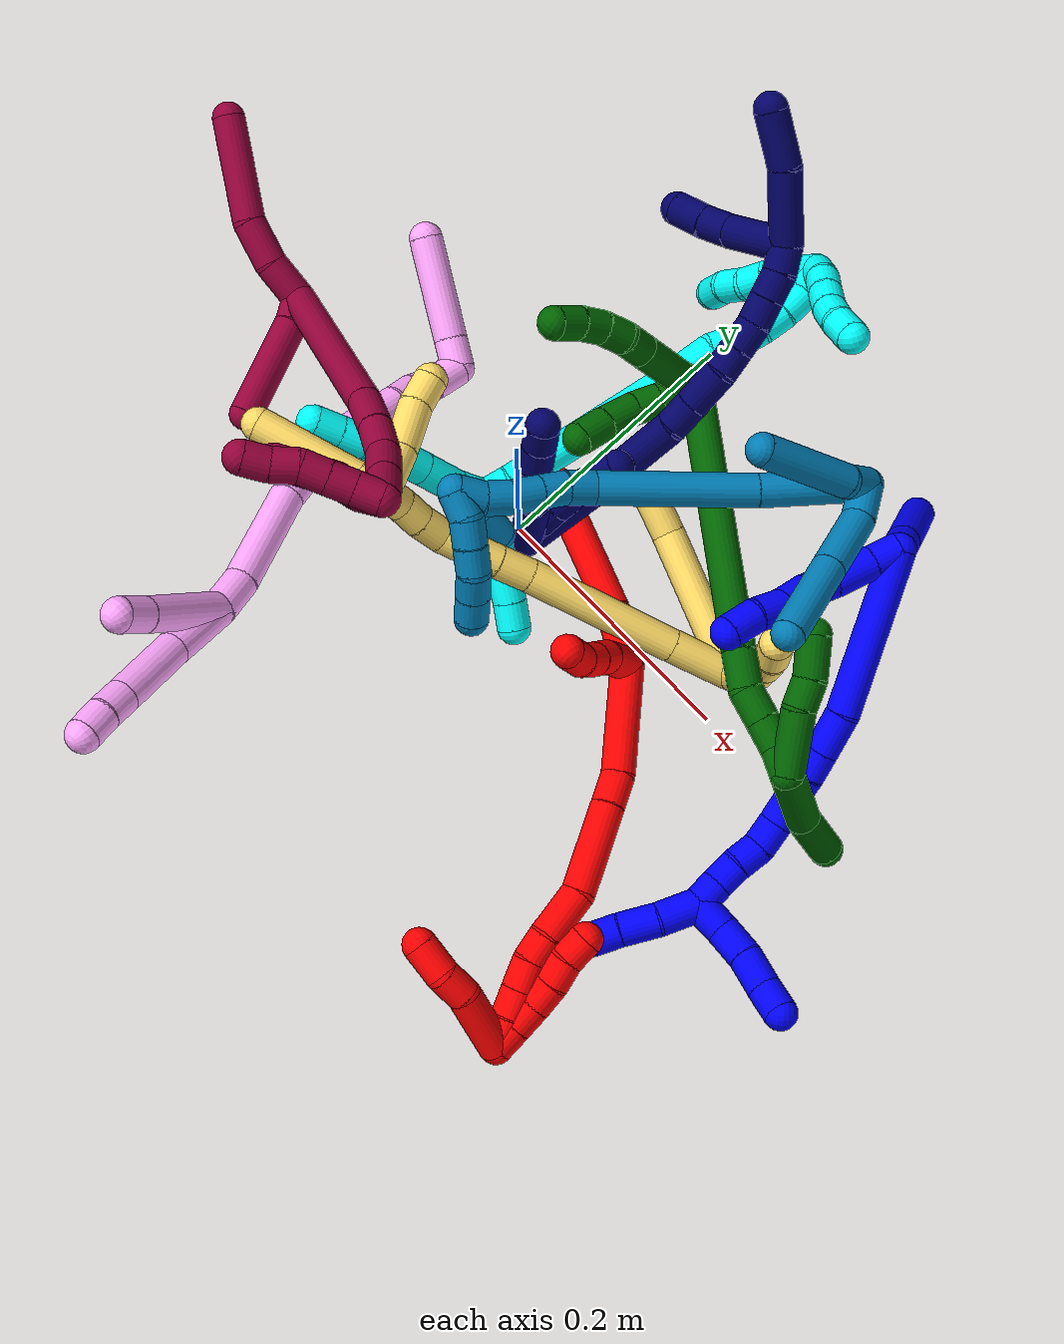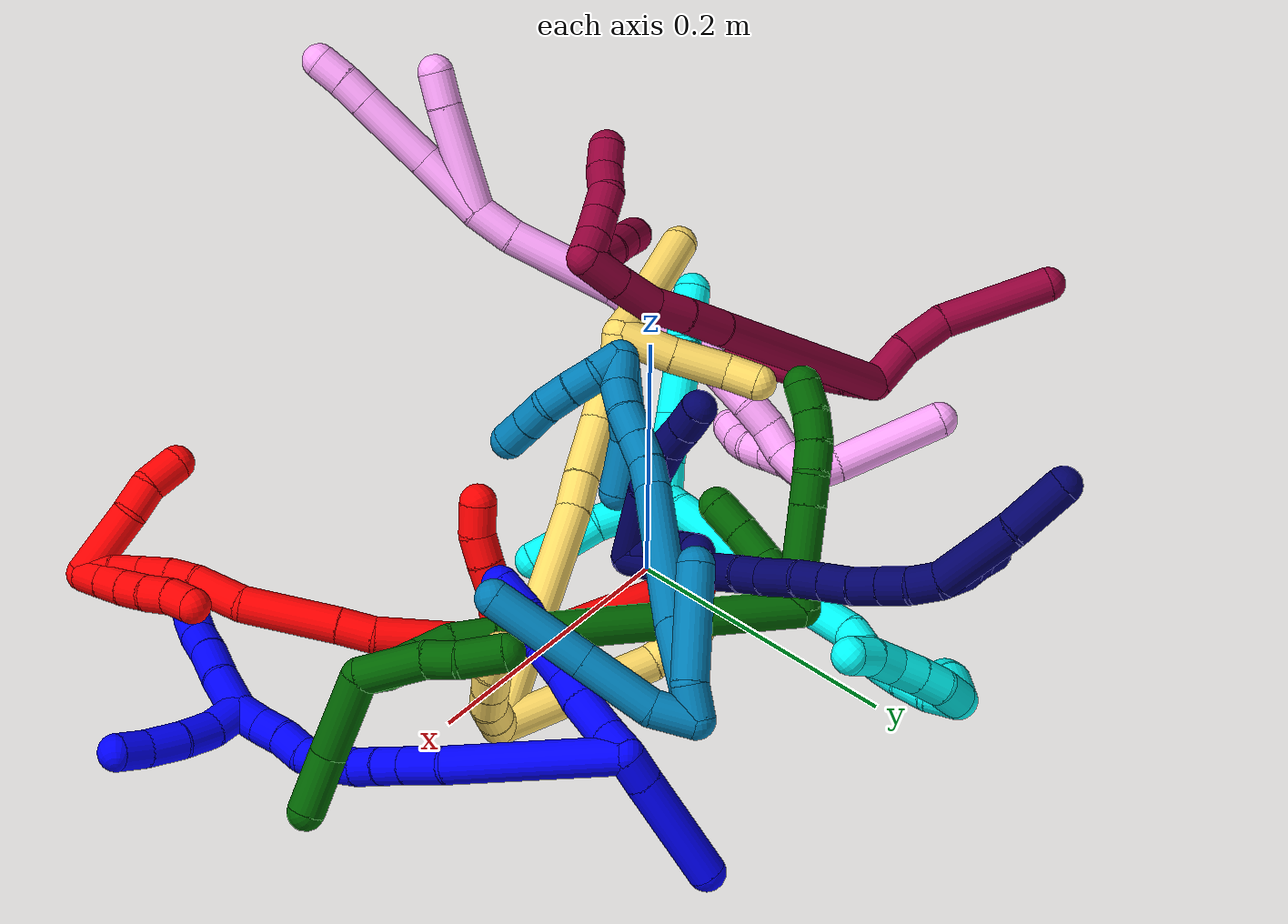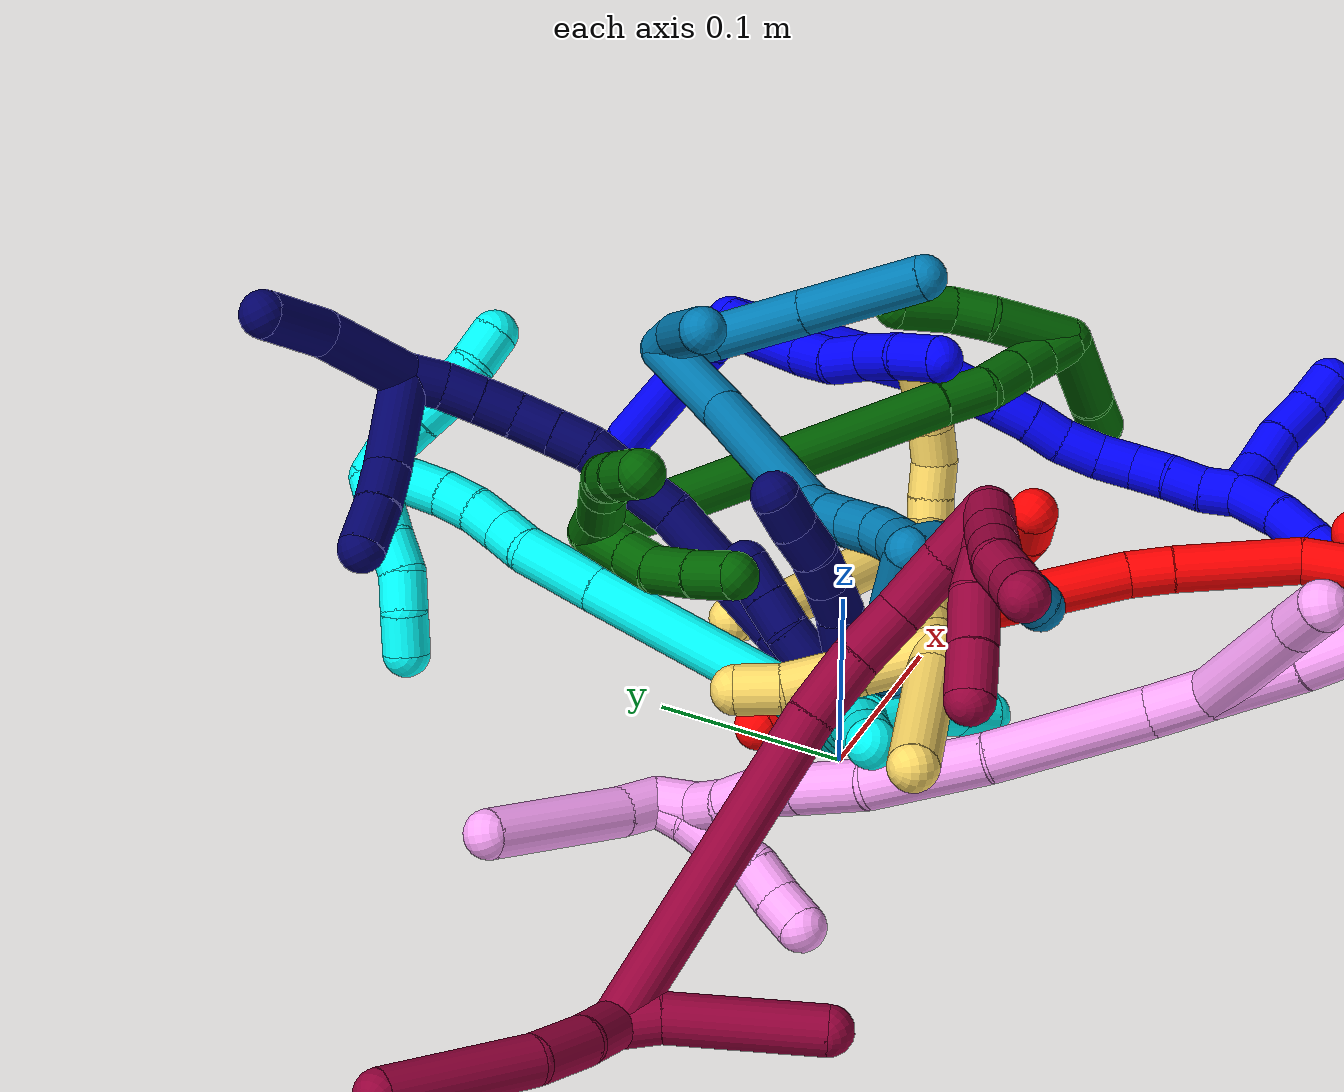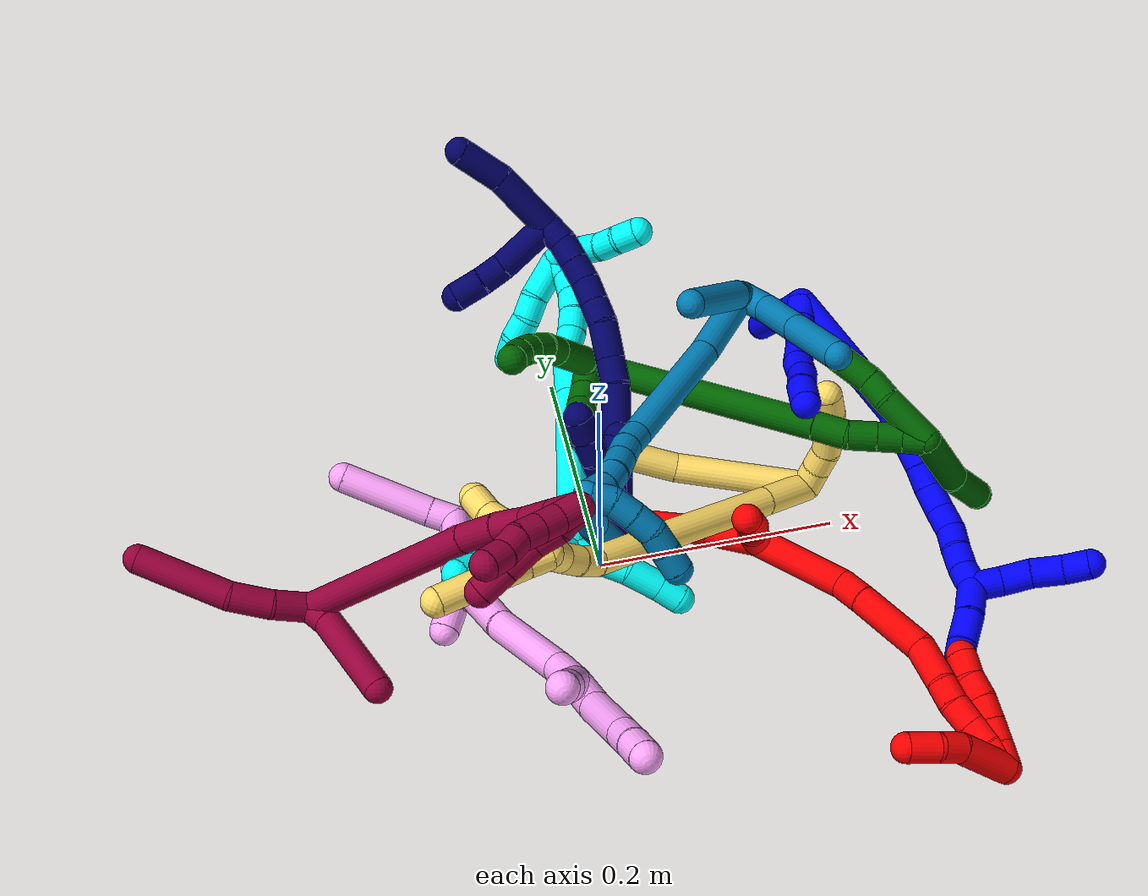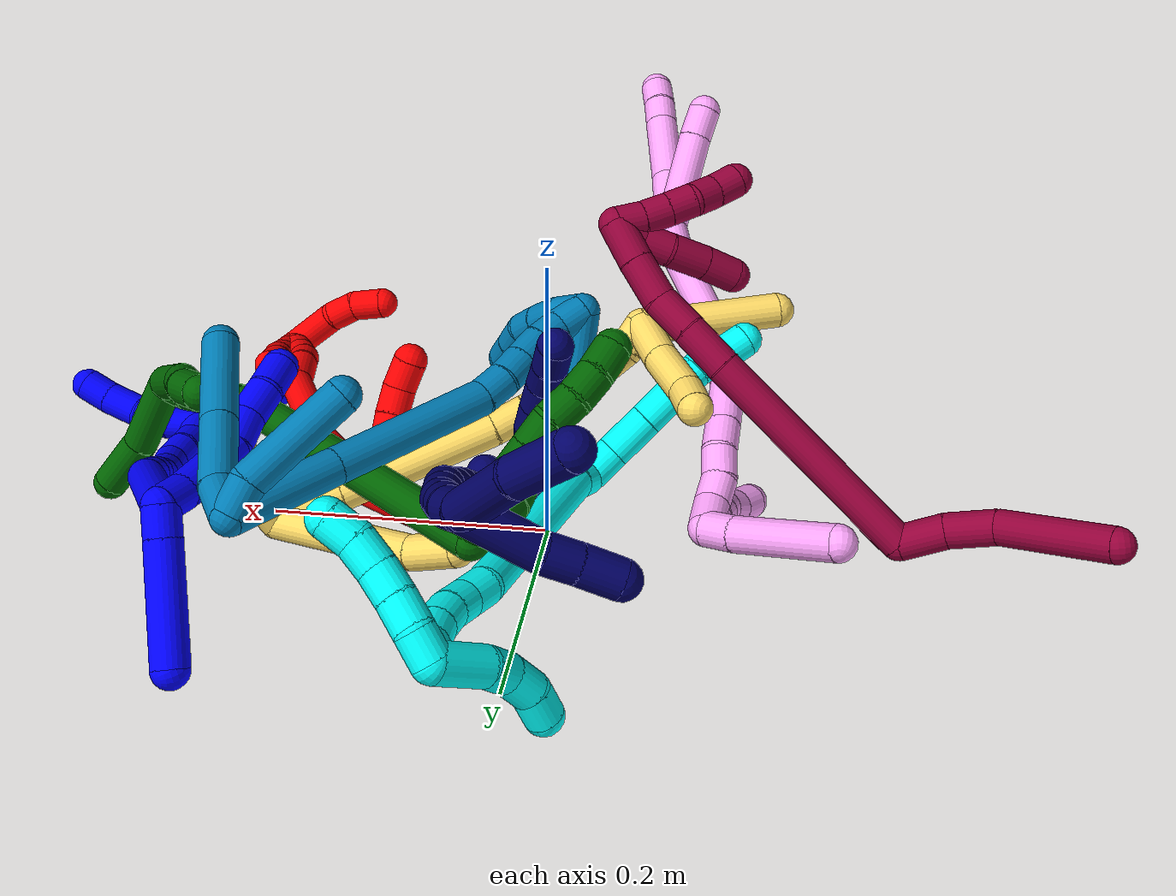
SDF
<sdf version="1.7">
 <world name="default">
  <plugin name="TubeGeneratorPlugin" filename="libtube_generator_plugin.so"/>
  <model name="photoneo_s_sensor">
   <static>1</static>
   <pose>0 0 2 1.57079 1.57079 3.14159</pose>
   <link name="link">
    <inertial><mass>0.1</mass></inertial>
    <sensor name="sensor" type="depth">
     <update_rate>30</update_rate>
     <camera>
      <horizontal_fov>1.22</horizontal_fov>
      <image><width>1920</width><height>1200</height><format>B8G8R8</format></image>
      <clip><near>0.1</near><far>4</far></clip>
      <depth_camera><output>points</output></depth_camera>
     </camera>
     <plugin name="camera_plugin" filename="libgazebo_ros_depth_camera.so">
      <baseline>0.2</baseline>
      <alwaysOn>1</alwaysOn>
      <updateRate>0.0</updateRate>
      <cameraName>camera_ir</cameraName>
      <imageTopicName>/camera/color/image_raw</imageTopicName>
      <cameraInfoTopicName>/camera/color/camera_info</cameraInfoTopicName>
      <depthImageTopicName>/camera/depth/image_raw</depthImageTopicName>
      <depthImageCameraInfoTopicName>/camera/depth/camera_info</depthImageCameraInfoTopicName>
      <pointCloudTopicName>/camera/depth/points</pointCloudTopicName>
      <frameName>fr_optical</frameName>
      <pointCloudCutoff>0.1</pointCloudCutoff>
      <pointCloudCutoffMax>2.0</pointCloudCutoffMax>
      <distortionK1>0</distortionK1>
      <distortionK2>0</distortionK2>
      <distortionK3>0</distortionK3>
      <distortionT1>0</distortionT1>
      <distortionT2>0</distortionT2>
      <CxPrime>0</CxPrime>
      <Cx>0</Cx>
      <Cy>0</Cy>
      <focalLength>0</focalLength>
      <hackBaseline>0</hackBaseline>
     </plugin>
    </sensor>
   </link>
  </model>
  <gravity>0 0 -9.8</gravity>
  <magnetic_field>6e-06 2.3e-05 -4.2e-05</magnetic_field>
  <atmosphere type="adiabatic"/>
  <physics name="default_physics" default="0" type="ode">
   <max_step_size>0.003</max_step_size>
   <real_time_factor>1</real_time_factor>
   <real_time_update_rate>1000</real_time_update_rate>
   <max_contacts>10000</max_contacts>
   <ode>
    <solver>
     <type>quick</type>
     <iters>100</iters>
     <sor>1.3</sor>
     <use_dynamic_moi_rescaling>0</use_dynamic_moi_rescaling>
    </solver>
    <constraints>
     <contact_max_correcting_vel>0</contact_max_correcting_vel>
     <contact_surface_layer>0.001</contact_surface_layer>
     <cfm>0</cfm>
     <erp>0.2</erp>
    </constraints>
   </ode>
  </physics>
  <scene><ambient>0.4 0.4 0.4 1</ambient><background>0.7 0.7 0.7 1</background><shadows>0</shadows></scene>
  <audio><device>default</device></audio>
  <spherical_coordinates>
   <surface_model>EARTH_WGS84</surface_model>
   <latitude_deg>0</latitude_deg>
   <longitude_deg>0</longitude_deg>
   <elevation>0</elevation>
   <heading_deg>0</heading_deg>
  </spherical_coordinates>
  <model name="bin">
   <static>1</static>
   <link name="bottom">
    <collision name="collision-bottom">
     <pose>0 0 -0.01 0 -0 0</pose>
     <geometry><box><size>0.8 0.6 0.02</size></box></geometry>
     <surface>
      <friction><ode><mu>100</mu><mu2>100</mu2></ode></friction>
      <contact><collide_bitmask>65535</collide_bitmask></contact>
     </surface>
    </collision>
   </link>
   <link name="west_wall">
    <collision name="collision-west_wall">
     <pose>-0.41 0 0.1 0 -0 0</pose>
     <geometry><box><size>0.02 0.6 0.2</size></box></geometry>
     <surface>
      <friction><ode><mu>100</mu><mu2>100</mu2></ode></friction>
      <contact><collide_bitmask>65535</collide_bitmask></contact>
     </surface>
    </collision>
   </link>
   <link name="east_wall">
    <collision name="collision-east_wall">
     <pose>0.41 0 0.1 0 -0 0</pose>
     <geometry><box><size>0.02 0.6 0.2</size></box></geometry>
     <surface>
      <friction><ode><mu>100</mu><mu2>100</mu2></ode></friction>
      <contact><collide_bitmask>65535</collide_bitmask></contact>
     </surface>
    </collision>
   </link>
   <link name="south_wall">
    <collision name="collision-south_wall">
     <pose>0 -0.31 0.1 0 -0 0</pose>
     <geometry><box><size>0.8 0.02 0.2</size></box></geometry>
     <surface>
      <friction><ode><mu>100</mu><mu2>100</mu2></ode></friction>
      <contact><collide_bitmask>65535</collide_bitmask></contact>
     </surface>
    </collision>
   </link>
   <link name="north_wall">
    <collision name="collision-north_wall">
     <pose>0 0.31 0.1 0 -0 0</pose>
     <geometry><box><size>0.8 0.02 0.2</size></box></geometry>
     <surface>
      <friction><ode><mu>100</mu><mu2>100</mu2></ode></friction>
      <contact><collide_bitmask>65535</collide_bitmask></contact>
     </surface>
    </collision>
   </link>
  </model>
  <model name="1">
   <static>0</static>
   <link name="1">
    <collision name="collision-cylinder-e_1_2_8">
     <pose>0.002035 -0.004633 -0.009463 2.68632 0.190786 0.783402</pose>
     <geometry><cylinder><radius>0.0125</radius><length>0.021461</length></cylinder></geometry>
     <surface>
      <friction><ode><mu>1.16</mu><mu2>1.16</mu2><slip1>0</slip1><slip2>0</slip2></ode></friction>
      <contact><ode><kp>1e+06</kp><kd>1</kd><max_vel>0</max_vel><min_depth>0.001</min_depth></ode></contact>
     </surface>
    </collision>
    <visual name="visual-cylinder-e_1_2_8">
     <pose>0.002035 -0.004633 -0.009463 2.68632 0.190786 0.783402</pose>
     <geometry><cylinder><radius>0.0125</radius><length>0.021461</length></cylinder></geometry>
     <material><ambient>0 0 1 1</ambient></material>
    </visual>
    <collision name="collision-cylinder-e_2_8_9">
     <pose>0.004875 -0.016772 -0.033515 2.66639 0.049042 0.201858</pose>
     <geometry><cylinder><radius>0.0125</radius><length>0.032855</length></cylinder></geometry>
     <surface>
      <friction><ode><mu>1.16</mu><mu2>1.16</mu2><slip1>0</slip1><slip2>0</slip2></ode></friction>
      <contact><ode><kp>1e+06</kp><kd>1</kd><max_vel>0</max_vel><min_depth>0.001</min_depth></ode></contact>
     </surface>
    </collision>
    <visual name="visual-cylinder-e_2_8_9">
     <pose>0.004875 -0.016772 -0.033515 2.66639 0.049042 0.201858</pose>
     <geometry><cylinder><radius>0.0125</radius><length>0.032855</length></cylinder></geometry>
     <material><ambient>0 0 1 1</ambient></material>
    </visual>
    <collision name="collision-cylinder-e_3_9_10">
     <pose>0.004526 -0.028588 -0.058263 2.74041 -0.104239 -0.502305</pose>
     <geometry><cylinder><radius>0.0125</radius><length>0.02219</length></cylinder></geometry>
     <surface>
      <friction><ode><mu>1.16</mu><mu2>1.16</mu2><slip1>0</slip1><slip2>0</slip2></ode></friction>
      <contact><ode><kp>1e+06</kp><kd>1</kd><max_vel>0</max_vel><min_depth>0.001</min_depth></ode></contact>
     </surface>
    </collision>
    <visual name="visual-cylinder-e_3_9_10">
     <pose>0.004526 -0.028588 -0.058263 2.74041 -0.104239 -0.502305</pose>
     <geometry><cylinder><radius>0.0125</radius><length>0.02219</length></cylinder></geometry>
     <material><ambient>0 0 1 1</ambient></material>
    </visual>
    <collision name="collision-cylinder-e_4_10_11">
     <pose>-0.000259 -0.039739 -0.077684 2.5054 -0.305439 -0.874527</pose>
     <geometry><cylinder><radius>0.0125</radius><length>0.024147</length></cylinder></geometry>
     <surface>
      <friction><ode><mu>1.16</mu><mu2>1.16</mu2><slip1>0</slip1><slip2>0</slip2></ode></friction>
      <contact><ode><kp>1e+06</kp><kd>1</kd><max_vel>0</max_vel><min_depth>0.001</min_depth></ode></contact>
     </surface>
    </collision>
    <visual name="visual-cylinder-e_4_10_11">
     <pose>-0.000259 -0.039739 -0.077684 2.5054 -0.305439 -0.874527</pose>
     <geometry><cylinder><radius>0.0125</radius><length>0.024147</length></cylinder></geometry>
     <material><ambient>0 0 1 1</ambient></material>
    </visual>
    <collision name="collision-cylinder-e_5_11_12">
     <pose>-0.00755 -0.051567 -0.097384 2.69586 -0.306459 -1.19634</pose>
     <geometry><cylinder><radius>0.0125</radius><length>0.024267</length></cylinder></geometry>
     <surface>
      <friction><ode><mu>1.16</mu><mu2>1.16</mu2><slip1>0</slip1><slip2>0</slip2></ode></friction>
      <contact><ode><kp>1e+06</kp><kd>1</kd><max_vel>0</max_vel><min_depth>0.001</min_depth></ode></contact>
     </surface>
    </collision>
    <visual name="visual-cylinder-e_5_11_12">
     <pose>-0.00755 -0.051567 -0.097384 2.69586 -0.306459 -1.19634</pose>
     <geometry><cylinder><radius>0.0125</radius><length>0.024267</length></cylinder></geometry>
     <material><ambient>0 0 1 1</ambient></material>
    </visual>
    <collision name="collision-cylinder-e_6_12_6">
     <pose>-0.013066 -0.063681 -0.117972 2.52949 -0.148493 -0.462395</pose>
     <geometry><cylinder><radius>0.0125</radius><length>0.025081</length></cylinder></geometry>
     <surface>
      <friction><ode><mu>1.16</mu><mu2>1.16</mu2><slip1>0</slip1><slip2>0</slip2></ode></friction>
      <contact><ode><kp>1e+06</kp><kd>1</kd><max_vel>0</max_vel><min_depth>0.001</min_depth></ode></contact>
     </surface>
    </collision>
    <visual name="visual-cylinder-e_6_12_6">
     <pose>-0.013066 -0.063681 -0.117972 2.52949 -0.148493 -0.462395</pose>
     <geometry><cylinder><radius>0.0125</radius><length>0.025081</length></cylinder></geometry>
     <material><ambient>0 0 1 1</ambient></material>
    </visual>
    <collision name="collision-cylinder-e_1_2_13">
     <pose>0.008269 0.00555 0.003645 -0.98965 0.89422 -0.506369</pose>
     <geometry><cylinder><radius>0.0125</radius><length>0.021211</length></cylinder></geometry>
     <surface>
      <friction><ode><mu>1.16</mu><mu2>1.16</mu2><slip1>0</slip1><slip2>0</slip2></ode></friction>
      <contact><ode><kp>1e+06</kp><kd>1</kd><max_vel>0</max_vel><min_depth>0.001</min_depth></ode></contact>
     </surface>
    </collision>
    <visual name="visual-cylinder-e_1_2_13">
     <pose>0.008269 0.00555 0.003645 -0.98965 0.89422 -0.506369</pose>
     <geometry><cylinder><radius>0.0125</radius><length>0.021211</length></cylinder></geometry>
     <material><ambient>0 0 1 1</ambient></material>
    </visual>
    <collision name="collision-cylinder-e_2_13_5">
     <pose>0.046329 0.032553 0.021582 -0.983149 0.857502 -0.480048</pose>
     <geometry><cylinder><radius>0.0125</radius><length>0.078789</length></cylinder></geometry>
     <surface>
      <friction><ode><mu>1.16</mu><mu2>1.16</mu2><slip1>0</slip1><slip2>0</slip2></ode></friction>
      <contact><ode><kp>1e+06</kp><kd>1</kd><max_vel>0</max_vel><min_depth>0.001</min_depth></ode></contact>
     </surface>
    </collision>
    <visual name="visual-cylinder-e_2_13_5">
     <pose>0.046329 0.032553 0.021582 -0.983149 0.857502 -0.480048</pose>
     <geometry><cylinder><radius>0.0125</radius><length>0.078789</length></cylinder></geometry>
     <material><ambient>0 0 1 1</ambient></material>
    </visual>
    <collision name="collision-cylinder-e_1_2_14">
     <pose>0.024619 -0.054353 -0.016602 1.86724 0.408788 0.546123</pose>
     <geometry><cylinder><radius>0.0125</radius><length>0.12387</length></cylinder></geometry>
     <surface>
      <friction><ode><mu>1.16</mu><mu2>1.16</mu2><slip1>0</slip1><slip2>0</slip2></ode></friction>
      <contact><ode><kp>1e+06</kp><kd>1</kd><max_vel>0</max_vel><min_depth>0.001</min_depth></ode></contact>
     </surface>
    </collision>
    <visual name="visual-cylinder-e_1_2_14">
     <pose>0.024619 -0.054353 -0.016602 1.86724 0.408788 0.546123</pose>
     <geometry><cylinder><radius>0.0125</radius><length>0.12387</length></cylinder></geometry>
     <material><ambient>0 0 1 1</ambient></material>
    </visual>
    <collision name="collision-cylinder-e_2_14_15">
     <pose>0.057219 -0.120459 -0.039432 2.05811 0.540408 0.862694</pose>
     <geometry><cylinder><radius>0.0125</radius><length>0.031024</length></cylinder></geometry>
     <surface>
      <friction><ode><mu>1.16</mu><mu2>1.16</mu2><slip1>0</slip1><slip2>0</slip2></ode></friction>
      <contact><ode><kp>1e+06</kp><kd>1</kd><max_vel>0</max_vel><min_depth>0.001</min_depth></ode></contact>
     </surface>
    </collision>
    <visual name="visual-cylinder-e_2_14_15">
     <pose>0.057219 -0.120459 -0.039432 2.05811 0.540408 0.862694</pose>
     <geometry><cylinder><radius>0.0125</radius><length>0.031024</length></cylinder></geometry>
     <material><ambient>0 0 1 1</ambient></material>
    </visual>
    <collision name="collision-cylinder-e_3_15_16">
     <pose>0.070492 -0.139904 -0.049865 2.07109 0.543174 0.878059</pose>
     <geometry><cylinder><radius>0.0125</radius><length>0.020479</length></cylinder></geometry>
     <surface>
      <friction><ode><mu>1.16</mu><mu2>1.16</mu2><slip1>0</slip1><slip2>0</slip2></ode></friction>
      <contact><ode><kp>1e+06</kp><kd>1</kd><max_vel>0</max_vel><min_depth>0.001</min_depth></ode></contact>
     </surface>
    </collision>
    <visual name="visual-cylinder-e_3_15_16">
     <pose>0.070492 -0.139904 -0.049865 2.07109 0.543174 0.878059</pose>
     <geometry><cylinder><radius>0.0125</radius><length>0.020479</length></cylinder></geometry>
     <material><ambient>0 0 1 1</ambient></material>
    </visual>
    <collision name="collision-cylinder-e_4_16_17">
     <pose>0.08193 -0.154621 -0.05848 2.13131 0.637602 1.07621</pose>
     <geometry><cylinder><radius>0.0125</radius><length>0.020648</length></cylinder></geometry>
     <surface>
      <friction><ode><mu>1.16</mu><mu2>1.16</mu2><slip1>0</slip1><slip2>0</slip2></ode></friction>
      <contact><ode><kp>1e+06</kp><kd>1</kd><max_vel>0</max_vel><min_depth>0.001</min_depth></ode></contact>
     </surface>
    </collision>
    <visual name="visual-cylinder-e_4_16_17">
     <pose>0.08193 -0.154621 -0.05848 2.13131 0.637602 1.07621</pose>
     <geometry><cylinder><radius>0.0125</radius><length>0.020648</length></cylinder></geometry>
     <material><ambient>0 0 1 1</ambient></material>
    </visual>
    <collision name="collision-cylinder-e_5_17_18">
     <pose>0.0927 -0.170193 -0.068293 2.13457 0.42898 0.753154</pose>
     <geometry><cylinder><radius>0.0125</radius><length>0.022237</length></cylinder></geometry>
     <surface>
      <friction><ode><mu>1.16</mu><mu2>1.16</mu2><slip1>0</slip1><slip2>0</slip2></ode></friction>
      <contact><ode><kp>1e+06</kp><kd>1</kd><max_vel>0</max_vel><min_depth>0.001</min_depth></ode></contact>
     </surface>
    </collision>
    <visual name="visual-cylinder-e_5_17_18">
     <pose>0.0927 -0.170193 -0.068293 2.13457 0.42898 0.753154</pose>
     <geometry><cylinder><radius>0.0125</radius><length>0.022237</length></cylinder></geometry>
     <material><ambient>0 0 1 1</ambient></material>
    </visual>
    <collision name="collision-cylinder-e_6_18_19">
     <pose>0.100139 -0.187056 -0.07951 2.18089 0.270564 0.511031</pose>
     <geometry><cylinder><radius>0.0125</radius><length>0.02106</length></cylinder></geometry>
     <surface>
      <friction><ode><mu>1.16</mu><mu2>1.16</mu2><slip1>0</slip1><slip2>0</slip2></ode></friction>
      <contact><ode><kp>1e+06</kp><kd>1</kd><max_vel>0</max_vel><min_depth>0.001</min_depth></ode></contact>
     </surface>
    </collision>
    <visual name="visual-cylinder-e_6_18_19">
     <pose>0.100139 -0.187056 -0.07951 2.18089 0.270564 0.511031</pose>
     <geometry><cylinder><radius>0.0125</radius><length>0.02106</length></cylinder></geometry>
     <material><ambient>0 0 1 1</ambient></material>
    </visual>
    <collision name="collision-cylinder-e_7_19_20">
     <pose>0.103909 -0.201672 -0.093362 2.47687 0.093281 0.268813</pose>
     <geometry><cylinder><radius>0.0125</radius><length>0.020517</length></cylinder></geometry>
     <surface>
      <friction><ode><mu>1.16</mu><mu2>1.16</mu2><slip1>0</slip1><slip2>0</slip2></ode></friction>
      <contact><ode><kp>1e+06</kp><kd>1</kd><max_vel>0</max_vel><min_depth>0.001</min_depth></ode></contact>
     </surface>
    </collision>
    <visual name="visual-cylinder-e_7_19_20">
     <pose>0.103909 -0.201672 -0.093362 2.47687 0.093281 0.268813</pose>
     <geometry><cylinder><radius>0.0125</radius><length>0.020517</length></cylinder></geometry>
     <material><ambient>0 0 1 1</ambient></material>
    </visual>
    <collision name="collision-cylinder-e_8_20_21">
     <pose>0.107209 -0.214868 -0.108334 2.35887 0.235346 0.558036</pose>
     <geometry><cylinder><radius>0.0125</radius><length>0.020109</length></cylinder></geometry>
     <surface>
      <friction><ode><mu>1.16</mu><mu2>1.16</mu2><slip1>0</slip1><slip2>0</slip2></ode></friction>
      <contact><ode><kp>1e+06</kp><kd>1</kd><max_vel>0</max_vel><min_depth>0.001</min_depth></ode></contact>
     </surface>
    </collision>
    <visual name="visual-cylinder-e_8_20_21">
     <pose>0.107209 -0.214868 -0.108334 2.35887 0.235346 0.558036</pose>
     <geometry><cylinder><radius>0.0125</radius><length>0.020109</length></cylinder></geometry>
     <material><ambient>0 0 1 1</ambient></material>
    </visual>
    <collision name="collision-cylinder-e_9_21_1">
     <pose>0.109813 -0.229248 -0.121935 2.2986 0.025942 0.057845</pose>
     <geometry><cylinder><radius>0.0125</radius><length>0.020057</length></cylinder></geometry>
     <surface>
      <friction><ode><mu>1.16</mu><mu2>1.16</mu2><slip1>0</slip1><slip2>0</slip2></ode></friction>
      <contact><ode><kp>1e+06</kp><kd>1</kd><max_vel>0</max_vel><min_depth>0.001</min_depth></ode></contact>
     </surface>
    </collision>
    <visual name="visual-cylinder-e_9_21_1">
     <pose>0.109813 -0.229248 -0.121935 2.2986 0.025942 0.057845</pose>
     <geometry><cylinder><radius>0.0125</radius><length>0.020057</length></cylinder></geometry>
     <material><ambient>0 0 1 1</ambient></material>
    </visual>
    <collision name="collision-cylinder-e_1_1_22">
     <pose>0.109212 -0.245689 -0.12028 0.821961 -0.070352 -0.030669</pose>
     <geometry><cylinder><radius>0.0125</radius><length>0.024515</length></cylinder></geometry>
     <surface>
      <friction><ode><mu>1.16</mu><mu2>1.16</mu2><slip1>0</slip1><slip2>0</slip2></ode></friction>
      <contact><ode><kp>1e+06</kp><kd>1</kd><max_vel>0</max_vel><min_depth>0.001</min_depth></ode></contact>
     </surface>
    </collision>
    <visual name="visual-cylinder-e_1_1_22">
     <pose>0.109212 -0.245689 -0.12028 0.821961 -0.070352 -0.030669</pose>
     <geometry><cylinder><radius>0.0125</radius><length>0.024515</length></cylinder></geometry>
     <material><ambient>0 0 1 1</ambient></material>
    </visual>
    <collision name="collision-cylinder-e_2_22_23">
     <pose>0.10442 -0.26473 -0.10475 0.950407 -0.307103 -0.158932</pose>
     <geometry><cylinder><radius>0.0125</radius><length>0.026004</length></cylinder></geometry>
     <surface>
      <friction><ode><mu>1.16</mu><mu2>1.16</mu2><slip1>0</slip1><slip2>0</slip2></ode></friction>
      <contact><ode><kp>1e+06</kp><kd>1</kd><max_vel>0</max_vel><min_depth>0.001</min_depth></ode></contact>
     </surface>
    </collision>
    <visual name="visual-cylinder-e_2_22_23">
     <pose>0.10442 -0.26473 -0.10475 0.950407 -0.307103 -0.158932</pose>
     <geometry><cylinder><radius>0.0125</radius><length>0.026004</length></cylinder></geometry>
     <material><ambient>0 0 1 1</ambient></material>
    </visual>
    <collision name="collision-cylinder-e_3_23_24">
     <pose>0.097017 -0.286657 -0.091634 1.10788 -0.256536 -0.159216</pose>
     <geometry><cylinder><radius>0.0125</radius><length>0.02737</length></cylinder></geometry>
     <surface>
      <friction><ode><mu>1.16</mu><mu2>1.16</mu2><slip1>0</slip1><slip2>0</slip2></ode></friction>
      <contact><ode><kp>1e+06</kp><kd>1</kd><max_vel>0</max_vel><min_depth>0.001</min_depth></ode></contact>
     </surface>
    </collision>
    <visual name="visual-cylinder-e_3_23_24">
     <pose>0.097017 -0.286657 -0.091634 1.10788 -0.256536 -0.159216</pose>
     <geometry><cylinder><radius>0.0125</radius><length>0.02737</length></cylinder></geometry>
     <material><ambient>0 0 1 1</ambient></material>
    </visual>
    <collision name="collision-cylinder-e_4_24_4">
     <pose>0.08925 -0.307631 -0.081203 1.11111 -0.39893 -0.249676</pose>
     <geometry><cylinder><radius>0.0125</radius><length>0.022112</length></cylinder></geometry>
     <surface>
      <friction><ode><mu>1.16</mu><mu2>1.16</mu2><slip1>0</slip1><slip2>0</slip2></ode></friction>
      <contact><ode><kp>1e+06</kp><kd>1</kd><max_vel>0</max_vel><min_depth>0.001</min_depth></ode></contact>
     </surface>
    </collision>
    <visual name="visual-cylinder-e_4_24_4">
     <pose>0.08925 -0.307631 -0.081203 1.11111 -0.39893 -0.249676</pose>
     <geometry><cylinder><radius>0.0125</radius><length>0.022112</length></cylinder></geometry>
     <material><ambient>0 0 1 1</ambient></material>
    </visual>
    <collision name="collision-cylinder-e_1_1_25">
     <pose>0.111312 -0.242227 -0.142977 2.77648 0.0803 0.428524</pose>
     <geometry><cylinder><radius>0.0125</radius><length>0.030874</length></cylinder></geometry>
     <surface>
      <friction><ode><mu>1.16</mu><mu2>1.16</mu2><slip1>0</slip1><slip2>0</slip2></ode></friction>
      <contact><ode><kp>1e+06</kp><kd>1</kd><max_vel>0</max_vel><min_depth>0.001</min_depth></ode></contact>
     </surface>
    </collision>
    <visual name="visual-cylinder-e_1_1_25">
     <pose>0.111312 -0.242227 -0.142977 2.77648 0.0803 0.428524</pose>
     <geometry><cylinder><radius>0.0125</radius><length>0.030874</length></cylinder></geometry>
     <material><ambient>0 0 1 1</ambient></material>
    </visual>
    <collision name="collision-cylinder-e_2_25_26">
     <pose>0.115529 -0.251141 -0.170745 2.89162 0.212245 1.40648</pose>
     <geometry><cylinder><radius>0.0125</radius><length>0.028285</length></cylinder></geometry>
     <surface>
      <friction><ode><mu>1.16</mu><mu2>1.16</mu2><slip1>0</slip1><slip2>0</slip2></ode></friction>
      <contact><ode><kp>1e+06</kp><kd>1</kd><max_vel>0</max_vel><min_depth>0.001</min_depth></ode></contact>
     </surface>
    </collision>
    <visual name="visual-cylinder-e_2_25_26">
     <pose>0.115529 -0.251141 -0.170745 2.89162 0.212245 1.40648</pose>
     <geometry><cylinder><radius>0.0125</radius><length>0.028285</length></cylinder></geometry>
     <material><ambient>0 0 1 1</ambient></material>
    </visual>
    <collision name="collision-cylinder-e_3_26_27">
     <pose>0.121505 -0.257607 -0.1935 2.82692 0.29557 1.50724</pose>
     <geometry><cylinder><radius>0.0125</radius><length>0.020578</length></cylinder></geometry>
     <surface>
      <friction><ode><mu>1.16</mu><mu2>1.16</mu2><slip1>0</slip1><slip2>0</slip2></ode></friction>
      <contact><ode><kp>1e+06</kp><kd>1</kd><max_vel>0</max_vel><min_depth>0.001</min_depth></ode></contact>
     </surface>
    </collision>
    <visual name="visual-cylinder-e_3_26_27">
     <pose>0.121505 -0.257607 -0.1935 2.82692 0.29557 1.50724</pose>
     <geometry><cylinder><radius>0.0125</radius><length>0.020578</length></cylinder></geometry>
     <material><ambient>0 0 1 1</ambient></material>
    </visual>
    <collision name="collision-cylinder-e_4_27_3">
     <pose>0.126228 -0.262865 -0.212595 2.91831 0.171185 1.3065</pose>
     <geometry><cylinder><radius>0.0125</radius><length>0.020264</length></cylinder></geometry>
     <surface>
      <friction><ode><mu>1.16</mu><mu2>1.16</mu2><slip1>0</slip1><slip2>0</slip2></ode></friction>
      <contact><ode><kp>1e+06</kp><kd>1</kd><max_vel>0</max_vel><min_depth>0.001</min_depth></ode></contact>
     </surface>
    </collision>
    <visual name="visual-cylinder-e_4_27_3">
     <pose>0.126228 -0.262865 -0.212595 2.91831 0.171185 1.3065</pose>
     <geometry><cylinder><radius>0.0125</radius><length>0.020264</length></cylinder></geometry>
     <material><ambient>0 0 1 1</ambient></material>
    </visual>
    <collision name="collision-sphere-3">
     <pose>0.127954 -0.265075 -0.222331 0 -0 0</pose>
     <geometry><sphere><radius>0.0125</radius></sphere></geometry>
     <surface>
      <friction><ode><mu>1.16</mu><mu2>1.16</mu2><slip1>0</slip1><slip2>0</slip2></ode></friction>
      <contact><ode><kp>1e+06</kp><kd>1</kd><max_vel>0</max_vel><min_depth>0.001</min_depth></ode></contact>
     </surface>
    </collision>
    <visual name="visual-sphere-3">
     <pose>0.127954 -0.265075 -0.222331 0 -0 0</pose>
     <geometry><sphere><radius>0.0125</radius></sphere></geometry>
     <material><ambient>0 0 1 1</ambient></material>
    </visual>
    <collision name="collision-sphere-27">
     <pose>0.124502 -0.260654 -0.202859 0 -0 0</pose>
     <geometry><sphere><radius>0.0125</radius></sphere></geometry>
     <surface>
      <friction><ode><mu>1.16</mu><mu2>1.16</mu2><slip1>0</slip1><slip2>0</slip2></ode></friction>
      <contact><ode><kp>1e+06</kp><kd>1</kd><max_vel>0</max_vel><min_depth>0.001</min_depth></ode></contact>
     </surface>
    </collision>
    <visual name="visual-sphere-27">
     <pose>0.124502 -0.260654 -0.202859 0 -0 0</pose>
     <geometry><sphere><radius>0.0125</radius></sphere></geometry>
     <material><ambient>0 0 1 1</ambient></material>
    </visual>
    <collision name="collision-sphere-26">
     <pose>0.118508 -0.254561 -0.18414 0 -0 0</pose>
     <geometry><sphere><radius>0.0125</radius></sphere></geometry>
     <surface>
      <friction><ode><mu>1.16</mu><mu2>1.16</mu2><slip1>0</slip1><slip2>0</slip2></ode></friction>
      <contact><ode><kp>1e+06</kp><kd>1</kd><max_vel>0</max_vel><min_depth>0.001</min_depth></ode></contact>
     </surface>
    </collision>
    <visual name="visual-sphere-26">
     <pose>0.118508 -0.254561 -0.18414 0 -0 0</pose>
     <geometry><sphere><radius>0.0125</radius></sphere></geometry>
     <material><ambient>0 0 1 1</ambient></material>
    </visual>
    <collision name="collision-sphere-25">
     <pose>0.11255 -0.247721 -0.15735 0 -0 0</pose>
     <geometry><sphere><radius>0.0125</radius></sphere></geometry>
     <surface>
      <friction><ode><mu>1.16</mu><mu2>1.16</mu2><slip1>0</slip1><slip2>0</slip2></ode></friction>
      <contact><ode><kp>1e+06</kp><kd>1</kd><max_vel>0</max_vel><min_depth>0.001</min_depth></ode></contact>
     </surface>
    </collision>
    <visual name="visual-sphere-25">
     <pose>0.11255 -0.247721 -0.15735 0 -0 0</pose>
     <geometry><sphere><radius>0.0125</radius></sphere></geometry>
     <material><ambient>0 0 1 1</ambient></material>
    </visual>
    <collision name="collision-sphere-4">
     <pose>0.084956 -0.316761 -0.076683 0 -0 0</pose>
     <geometry><sphere><radius>0.0125</radius></sphere></geometry>
     <surface>
      <friction><ode><mu>1.16</mu><mu2>1.16</mu2><slip1>0</slip1><slip2>0</slip2></ode></friction>
      <contact><ode><kp>1e+06</kp><kd>1</kd><max_vel>0</max_vel><min_depth>0.001</min_depth></ode></contact>
     </surface>
    </collision>
    <visual name="visual-sphere-4">
     <pose>0.084956 -0.316761 -0.076683 0 -0 0</pose>
     <geometry><sphere><radius>0.0125</radius></sphere></geometry>
     <material><ambient>0 0 1 1</ambient></material>
    </visual>
    <collision name="collision-sphere-24">
     <pose>0.093545 -0.298501 -0.085723 0 -0 0</pose>
     <geometry><sphere><radius>0.0125</radius></sphere></geometry>
     <surface>
      <friction><ode><mu>1.16</mu><mu2>1.16</mu2><slip1>0</slip1><slip2>0</slip2></ode></friction>
      <contact><ode><kp>1e+06</kp><kd>1</kd><max_vel>0</max_vel><min_depth>0.001</min_depth></ode></contact>
     </surface>
    </collision>
    <visual name="visual-sphere-24">
     <pose>0.093545 -0.298501 -0.085723 0 -0 0</pose>
     <geometry><sphere><radius>0.0125</radius></sphere></geometry>
     <material><ambient>0 0 1 1</ambient></material>
    </visual>
    <collision name="collision-sphere-23">
     <pose>0.100489 -0.274814 -0.097545 0 -0 0</pose>
     <geometry><sphere><radius>0.0125</radius></sphere></geometry>
     <surface>
      <friction><ode><mu>1.16</mu><mu2>1.16</mu2><slip1>0</slip1><slip2>0</slip2></ode></friction>
      <contact><ode><kp>1e+06</kp><kd>1</kd><max_vel>0</max_vel><min_depth>0.001</min_depth></ode></contact>
     </surface>
    </collision>
    <visual name="visual-sphere-23">
     <pose>0.100489 -0.274814 -0.097545 0 -0 0</pose>
     <geometry><sphere><radius>0.0125</radius></sphere></geometry>
     <material><ambient>0 0 1 1</ambient></material>
    </visual>
    <collision name="collision-sphere-22">
     <pose>0.10835 -0.254645 -0.111956 0 -0 0</pose>
     <geometry><sphere><radius>0.0125</radius></sphere></geometry>
     <surface>
      <friction><ode><mu>1.16</mu><mu2>1.16</mu2><slip1>0</slip1><slip2>0</slip2></ode></friction>
      <contact><ode><kp>1e+06</kp><kd>1</kd><max_vel>0</max_vel><min_depth>0.001</min_depth></ode></contact>
     </surface>
    </collision>
    <visual name="visual-sphere-22">
     <pose>0.10835 -0.254645 -0.111956 0 -0 0</pose>
     <geometry><sphere><radius>0.0125</radius></sphere></geometry>
     <material><ambient>0 0 1 1</ambient></material>
    </visual>
    <collision name="collision-sphere-1">
     <pose>0.110074 -0.236733 -0.128604 0 -0 0</pose>
     <geometry><sphere><radius>0.0125</radius></sphere></geometry>
     <surface>
      <friction><ode><mu>1.16</mu><mu2>1.16</mu2><slip1>0</slip1><slip2>0</slip2></ode></friction>
      <contact><ode><kp>1e+06</kp><kd>1</kd><max_vel>0</max_vel><min_depth>0.001</min_depth></ode></contact>
     </surface>
    </collision>
    <visual name="visual-sphere-1">
     <pose>0.110074 -0.236733 -0.128604 0 -0 0</pose>
     <geometry><sphere><radius>0.0125</radius></sphere></geometry>
     <material><ambient>0 0 1 1</ambient></material>
    </visual>
    <collision name="collision-sphere-21">
     <pose>0.109553 -0.221763 -0.115266 0 -0 0</pose>
     <geometry><sphere><radius>0.0125</radius></sphere></geometry>
     <surface>
      <friction><ode><mu>1.16</mu><mu2>1.16</mu2><slip1>0</slip1><slip2>0</slip2></ode></friction>
      <contact><ode><kp>1e+06</kp><kd>1</kd><max_vel>0</max_vel><min_depth>0.001</min_depth></ode></contact>
     </surface>
    </collision>
    <visual name="visual-sphere-21">
     <pose>0.109553 -0.221763 -0.115266 0 -0 0</pose>
     <geometry><sphere><radius>0.0125</radius></sphere></geometry>
     <material><ambient>0 0 1 1</ambient></material>
    </visual>
    <collision name="collision-sphere-12">
     <pose>-0.011211 -0.056554 -0.107821 0 -0 0</pose>
     <geometry><sphere><radius>0.0125</radius></sphere></geometry>
     <surface>
      <friction><ode><mu>1.16</mu><mu2>1.16</mu2><slip1>0</slip1><slip2>0</slip2></ode></friction>
      <contact><ode><kp>1e+06</kp><kd>1</kd><max_vel>0</max_vel><min_depth>0.001</min_depth></ode></contact>
     </surface>
    </collision>
    <visual name="visual-sphere-12">
     <pose>-0.011211 -0.056554 -0.107821 0 -0 0</pose>
     <geometry><sphere><radius>0.0125</radius></sphere></geometry>
     <material><ambient>0 0 1 1</ambient></material>
    </visual>
    <collision name="collision-sphere-11">
     <pose>-0.00389 -0.04658 -0.086946 0 -0 0</pose>
     <geometry><sphere><radius>0.0125</radius></sphere></geometry>
     <surface>
      <friction><ode><mu>1.16</mu><mu2>1.16</mu2><slip1>0</slip1><slip2>0</slip2></ode></friction>
      <contact><ode><kp>1e+06</kp><kd>1</kd><max_vel>0</max_vel><min_depth>0.001</min_depth></ode></contact>
     </surface>
    </collision>
    <visual name="visual-sphere-11">
     <pose>-0.00389 -0.04658 -0.086946 0 -0 0</pose>
     <geometry><sphere><radius>0.0125</radius></sphere></geometry>
     <material><ambient>0 0 1 1</ambient></material>
    </visual>
    <collision name="collision-sphere-10">
     <pose>0.003371 -0.032897 -0.068422 0 -0 0</pose>
     <geometry><sphere><radius>0.0125</radius></sphere></geometry>
     <surface>
      <friction><ode><mu>1.16</mu><mu2>1.16</mu2><slip1>0</slip1><slip2>0</slip2></ode></friction>
      <contact><ode><kp>1e+06</kp><kd>1</kd><max_vel>0</max_vel><min_depth>0.001</min_depth></ode></contact>
     </surface>
    </collision>
    <visual name="visual-sphere-10">
     <pose>0.003371 -0.032897 -0.068422 0 -0 0</pose>
     <geometry><sphere><radius>0.0125</radius></sphere></geometry>
     <material><ambient>0 0 1 1</ambient></material>
    </visual>
    <collision name="collision-sphere-9">
     <pose>0.00568 -0.024279 -0.048105 0 -0 0</pose>
     <geometry><sphere><radius>0.0125</radius></sphere></geometry>
     <surface>
      <friction><ode><mu>1.16</mu><mu2>1.16</mu2><slip1>0</slip1><slip2>0</slip2></ode></friction>
      <contact><ode><kp>1e+06</kp><kd>1</kd><max_vel>0</max_vel><min_depth>0.001</min_depth></ode></contact>
     </surface>
    </collision>
    <visual name="visual-sphere-9">
     <pose>0.00568 -0.024279 -0.048105 0 -0 0</pose>
     <geometry><sphere><radius>0.0125</radius></sphere></geometry>
     <material><ambient>0 0 1 1</ambient></material>
    </visual>
    <collision name="collision-sphere-2">
     <geometry><sphere><radius>0.0125</radius></sphere></geometry>
     <surface>
      <friction><ode><mu>1.16</mu><mu2>1.16</mu2><slip1>0</slip1><slip2>0</slip2></ode></friction>
      <contact><ode><kp>1e+06</kp><kd>1</kd><max_vel>0</max_vel><min_depth>0.001</min_depth></ode></contact>
     </surface>
    </collision>
    <visual name="visual-sphere-2">
     <geometry><sphere><radius>0.0125</radius></sphere></geometry>
     <material><ambient>0 0 1 1</ambient></material>
    </visual>
    <collision name="collision-sphere-19">
     <pose>0.102953 -0.195372 -0.085323 0 -0 0</pose>
     <geometry><sphere><radius>0.0125</radius></sphere></geometry>
     <surface>
      <friction><ode><mu>1.16</mu><mu2>1.16</mu2><slip1>0</slip1><slip2>0</slip2></ode></friction>
      <contact><ode><kp>1e+06</kp><kd>1</kd><max_vel>0</max_vel><min_depth>0.001</min_depth></ode></contact>
     </surface>
    </collision>
    <visual name="visual-sphere-19">
     <pose>0.102953 -0.195372 -0.085323 0 -0 0</pose>
     <geometry><sphere><radius>0.0125</radius></sphere></geometry>
     <material><ambient>0 0 1 1</ambient></material>
    </visual>
    <collision name="collision-sphere-8">
     <pose>0.00407 -0.009265 -0.018925 0 -0 0</pose>
     <geometry><sphere><radius>0.0125</radius></sphere></geometry>
     <surface>
      <friction><ode><mu>1.16</mu><mu2>1.16</mu2><slip1>0</slip1><slip2>0</slip2></ode></friction>
      <contact><ode><kp>1e+06</kp><kd>1</kd><max_vel>0</max_vel><min_depth>0.001</min_depth></ode></contact>
     </surface>
    </collision>
    <visual name="visual-sphere-8">
     <pose>0.00407 -0.009265 -0.018925 0 -0 0</pose>
     <geometry><sphere><radius>0.0125</radius></sphere></geometry>
     <material><ambient>0 0 1 1</ambient></material>
    </visual>
    <collision name="collision-sphere-6">
     <pose>-0.014921 -0.070807 -0.128122 0 -0 0</pose>
     <geometry><sphere><radius>0.0125</radius></sphere></geometry>
     <surface>
      <friction><ode><mu>1.16</mu><mu2>1.16</mu2><slip1>0</slip1><slip2>0</slip2></ode></friction>
      <contact><ode><kp>1e+06</kp><kd>1</kd><max_vel>0</max_vel><min_depth>0.001</min_depth></ode></contact>
     </surface>
    </collision>
    <visual name="visual-sphere-6">
     <pose>-0.014921 -0.070807 -0.128122 0 -0 0</pose>
     <geometry><sphere><radius>0.0125</radius></sphere></geometry>
     <material><ambient>0 0 1 1</ambient></material>
    </visual>
    <collision name="collision-sphere-13">
     <pose>0.016539 0.011101 0.007291 0 -0 0</pose>
     <geometry><sphere><radius>0.0125</radius></sphere></geometry>
     <surface>
      <friction><ode><mu>1.16</mu><mu2>1.16</mu2><slip1>0</slip1><slip2>0</slip2></ode></friction>
      <contact><ode><kp>1e+06</kp><kd>1</kd><max_vel>0</max_vel><min_depth>0.001</min_depth></ode></contact>
     </surface>
    </collision>
    <visual name="visual-sphere-13">
     <pose>0.016539 0.011101 0.007291 0 -0 0</pose>
     <geometry><sphere><radius>0.0125</radius></sphere></geometry>
     <material><ambient>0 0 1 1</ambient></material>
    </visual>
    <collision name="collision-sphere-5">
     <pose>0.07612 0.054006 0.035873 0 -0 0</pose>
     <geometry><sphere><radius>0.0125</radius></sphere></geometry>
     <surface>
      <friction><ode><mu>1.16</mu><mu2>1.16</mu2><slip1>0</slip1><slip2>0</slip2></ode></friction>
      <contact><ode><kp>1e+06</kp><kd>1</kd><max_vel>0</max_vel><min_depth>0.001</min_depth></ode></contact>
     </surface>
    </collision>
    <visual name="visual-sphere-5">
     <pose>0.07612 0.054006 0.035873 0 -0 0</pose>
     <geometry><sphere><radius>0.0125</radius></sphere></geometry>
     <material><ambient>0 0 1 1</ambient></material>
    </visual>
    <collision name="collision-sphere-14">
     <pose>0.049238 -0.108706 -0.033203 0 -0 0</pose>
     <geometry><sphere><radius>0.0125</radius></sphere></geometry>
     <surface>
      <friction><ode><mu>1.16</mu><mu2>1.16</mu2><slip1>0</slip1><slip2>0</slip2></ode></friction>
      <contact><ode><kp>1e+06</kp><kd>1</kd><max_vel>0</max_vel><min_depth>0.001</min_depth></ode></contact>
     </surface>
    </collision>
    <visual name="visual-sphere-14">
     <pose>0.049238 -0.108706 -0.033203 0 -0 0</pose>
     <geometry><sphere><radius>0.0125</radius></sphere></geometry>
     <material><ambient>0 0 1 1</ambient></material>
    </visual>
    <collision name="collision-sphere-15">
     <pose>0.065199 -0.132212 -0.04566 0 -0 0</pose>
     <geometry><sphere><radius>0.0125</radius></sphere></geometry>
     <surface>
      <friction><ode><mu>1.16</mu><mu2>1.16</mu2><slip1>0</slip1><slip2>0</slip2></ode></friction>
      <contact><ode><kp>1e+06</kp><kd>1</kd><max_vel>0</max_vel><min_depth>0.001</min_depth></ode></contact>
     </surface>
    </collision>
    <visual name="visual-sphere-15">
     <pose>0.065199 -0.132212 -0.04566 0 -0 0</pose>
     <geometry><sphere><radius>0.0125</radius></sphere></geometry>
     <material><ambient>0 0 1 1</ambient></material>
    </visual>
    <collision name="collision-sphere-16">
     <pose>0.075784 -0.147595 -0.05407 0 -0 0</pose>
     <geometry><sphere><radius>0.0125</radius></sphere></geometry>
     <surface>
      <friction><ode><mu>1.16</mu><mu2>1.16</mu2><slip1>0</slip1><slip2>0</slip2></ode></friction>
      <contact><ode><kp>1e+06</kp><kd>1</kd><max_vel>0</max_vel><min_depth>0.001</min_depth></ode></contact>
     </surface>
    </collision>
    <visual name="visual-sphere-16">
     <pose>0.075784 -0.147595 -0.05407 0 -0 0</pose>
     <geometry><sphere><radius>0.0125</radius></sphere></geometry>
     <material><ambient>0 0 1 1</ambient></material>
    </visual>
    <collision name="collision-sphere-17">
     <pose>0.088075 -0.161647 -0.06289 0 -0 0</pose>
     <geometry><sphere><radius>0.0125</radius></sphere></geometry>
     <surface>
      <friction><ode><mu>1.16</mu><mu2>1.16</mu2><slip1>0</slip1><slip2>0</slip2></ode></friction>
      <contact><ode><kp>1e+06</kp><kd>1</kd><max_vel>0</max_vel><min_depth>0.001</min_depth></ode></contact>
     </surface>
    </collision>
    <visual name="visual-sphere-17">
     <pose>0.088075 -0.161647 -0.06289 0 -0 0</pose>
     <geometry><sphere><radius>0.0125</radius></sphere></geometry>
     <material><ambient>0 0 1 1</ambient></material>
    </visual>
    <collision name="collision-sphere-18">
     <pose>0.097324 -0.17874 -0.073696 0 -0 0</pose>
     <geometry><sphere><radius>0.0125</radius></sphere></geometry>
     <surface>
      <friction><ode><mu>1.16</mu><mu2>1.16</mu2><slip1>0</slip1><slip2>0</slip2></ode></friction>
      <contact><ode><kp>1e+06</kp><kd>1</kd><max_vel>0</max_vel><min_depth>0.001</min_depth></ode></contact>
     </surface>
    </collision>
    <visual name="visual-sphere-18">
     <pose>0.097324 -0.17874 -0.073696 0 -0 0</pose>
     <geometry><sphere><radius>0.0125</radius></sphere></geometry>
     <material><ambient>0 0 1 1</ambient></material>
    </visual>
    <collision name="collision-sphere-20">
     <pose>0.104864 -0.207973 -0.101401 0 -0 0</pose>
     <geometry><sphere><radius>0.0125</radius></sphere></geometry>
     <surface>
      <friction><ode><mu>1.16</mu><mu2>1.16</mu2><slip1>0</slip1><slip2>0</slip2></ode></friction>
      <contact><ode><kp>1e+06</kp><kd>1</kd><max_vel>0</max_vel><min_depth>0.001</min_depth></ode></contact>
     </surface>
    </collision>
    <visual name="visual-sphere-20">
     <pose>0.104864 -0.207973 -0.101401 0 -0 0</pose>
     <geometry><sphere><radius>0.0125</radius></sphere></geometry>
     <material><ambient>0 0 1 1</ambient></material>
    </visual>
    <inertial>
     <pose>0.058689 -0.12331 -0.06769 0 -0 0</pose>
     <mass>0.75</mass>
     <inertia><ixx>0.000276</ixx><ixy>0</ixy><ixz>0</ixz><iyy>6.3e-05</iyy><iyz>0</iyz><izz>2.3e-05</izz></inertia>
    </inertial>
   </link>
   <pose>0.215676 0.167868 0.094658 -2.72924 1.43177 -1.92028</pose>
  </model>
  <model name="2">
   <static>0</static>
   <link name="2">
    <collision name="collision-cylinder-e_1_2_8">
     <pose>-0.006658 0.005577 -0.02033 -2.87386 -0.305932 1.7056</pose>
     <geometry><cylinder><radius>0.0125</radius><length>0.044214</length></cylinder></geometry>
     <surface>
      <friction><ode><mu>1.16</mu><mu2>1.16</mu2><slip1>0</slip1><slip2>0</slip2></ode></friction>
      <contact><ode><kp>1e+06</kp><kd>1</kd><max_vel>0</max_vel><min_depth>0.001</min_depth></ode></contact>
     </surface>
    </collision>
    <visual name="visual-cylinder-e_1_2_8">
     <pose>-0.006658 0.005577 -0.02033 -2.87386 -0.305932 1.7056</pose>
     <geometry><cylinder><radius>0.0125</radius><length>0.044214</length></cylinder></geometry>
     <material><ambient>1 0 0 1</ambient></material>
    </visual>
    <collision name="collision-cylinder-e_2_8_9">
     <pose>-0.022228 0.014427 -0.074722 -3.04579 -0.25475 2.42526</pose>
     <geometry><cylinder><radius>0.0125</radius><length>0.070722</length></cylinder></geometry>
     <surface>
      <friction><ode><mu>1.16</mu><mu2>1.16</mu2><slip1>0</slip1><slip2>0</slip2></ode></friction>
      <contact><ode><kp>1e+06</kp><kd>1</kd><max_vel>0</max_vel><min_depth>0.001</min_depth></ode></contact>
     </surface>
    </collision>
    <visual name="visual-cylinder-e_2_8_9">
     <pose>-0.022228 0.014427 -0.074722 -3.04579 -0.25475 2.42526</pose>
     <geometry><cylinder><radius>0.0125</radius><length>0.070722</length></cylinder></geometry>
     <material><ambient>1 0 0 1</ambient></material>
    </visual>
    <collision name="collision-cylinder-e_3_9_6">
     <pose>-0.035071 0.019968 -0.125719 -3.00849 -0.226225 2.08038</pose>
     <geometry><cylinder><radius>0.0125</radius><length>0.035064</length></cylinder></geometry>
     <surface>
      <friction><ode><mu>1.16</mu><mu2>1.16</mu2><slip1>0</slip1><slip2>0</slip2></ode></friction>
      <contact><ode><kp>1e+06</kp><kd>1</kd><max_vel>0</max_vel><min_depth>0.001</min_depth></ode></contact>
     </surface>
    </collision>
    <visual name="visual-cylinder-e_3_9_6">
     <pose>-0.035071 0.019968 -0.125719 -3.00849 -0.226225 2.08038</pose>
     <geometry><cylinder><radius>0.0125</radius><length>0.035064</length></cylinder></geometry>
     <material><ambient>1 0 0 1</ambient></material>
    </visual>
    <collision name="collision-cylinder-e_1_2_10">
     <pose>-0.009463 -0.015685 -0.001353 1.65682 -0.541245 -0.587284</pose>
     <geometry><cylinder><radius>0.0125</radius><length>0.036737</length></cylinder></geometry>
     <surface>
      <friction><ode><mu>1.16</mu><mu2>1.16</mu2><slip1>0</slip1><slip2>0</slip2></ode></friction>
      <contact><ode><kp>1e+06</kp><kd>1</kd><max_vel>0</max_vel><min_depth>0.001</min_depth></ode></contact>
     </surface>
    </collision>
    <visual name="visual-cylinder-e_1_2_10">
     <pose>-0.009463 -0.015685 -0.001353 1.65682 -0.541245 -0.587284</pose>
     <geometry><cylinder><radius>0.0125</radius><length>0.036737</length></cylinder></geometry>
     <material><ambient>1 0 0 1</ambient></material>
    </visual>
    <collision name="collision-cylinder-e_2_10_11">
     <pose>-0.022842 -0.041069 -0.001807 1.4785 -0.382177 -0.34915</pose>
     <geometry><cylinder><radius>0.0125</radius><length>0.020997</length></cylinder></geometry>
     <surface>
      <friction><ode><mu>1.16</mu><mu2>1.16</mu2><slip1>0</slip1><slip2>0</slip2></ode></friction>
      <contact><ode><kp>1e+06</kp><kd>1</kd><max_vel>0</max_vel><min_depth>0.001</min_depth></ode></contact>
     </surface>
    </collision>
    <visual name="visual-cylinder-e_2_10_11">
     <pose>-0.022842 -0.041069 -0.001807 1.4785 -0.382177 -0.34915</pose>
     <geometry><cylinder><radius>0.0125</radius><length>0.020997</length></cylinder></geometry>
     <material><ambient>1 0 0 1</ambient></material>
    </visual>
    <collision name="collision-cylinder-e_3_11_12">
     <pose>-0.030501 -0.060216 -0.000783 1.55738 -0.377202 -0.37229</pose>
     <geometry><cylinder><radius>0.0125</radius><length>0.020326</length></cylinder></geometry>
     <surface>
      <friction><ode><mu>1.16</mu><mu2>1.16</mu2><slip1>0</slip1><slip2>0</slip2></ode></friction>
      <contact><ode><kp>1e+06</kp><kd>1</kd><max_vel>0</max_vel><min_depth>0.001</min_depth></ode></contact>
     </surface>
    </collision>
    <visual name="visual-cylinder-e_3_11_12">
     <pose>-0.030501 -0.060216 -0.000783 1.55738 -0.377202 -0.37229</pose>
     <geometry><cylinder><radius>0.0125</radius><length>0.020326</length></cylinder></geometry>
     <material><ambient>1 0 0 1</ambient></material>
    </visual>
    <collision name="collision-cylinder-e_4_12_5">
     <pose>-0.040606 -0.078396 -0.002559 1.78536 -0.618677 -0.755393</pose>
     <geometry><cylinder><radius>0.0125</radius><length>0.02194</length></cylinder></geometry>
     <surface>
      <friction><ode><mu>1.16</mu><mu2>1.16</mu2><slip1>0</slip1><slip2>0</slip2></ode></friction>
      <contact><ode><kp>1e+06</kp><kd>1</kd><max_vel>0</max_vel><min_depth>0.001</min_depth></ode></contact>
     </surface>
    </collision>
    <visual name="visual-cylinder-e_4_12_5">
     <pose>-0.040606 -0.078396 -0.002559 1.78536 -0.618677 -0.755393</pose>
     <geometry><cylinder><radius>0.0125</radius><length>0.02194</length></cylinder></geometry>
     <material><ambient>1 0 0 1</ambient></material>
    </visual>
    <collision name="collision-cylinder-e_1_2_13">
     <pose>0.017417 -0.021929 0.031578 0.606995 0.425379 0.135057</pose>
     <geometry><cylinder><radius>0.0125</radius><length>0.084414</length></cylinder></geometry>
     <surface>
      <friction><ode><mu>1.16</mu><mu2>1.16</mu2><slip1>0</slip1><slip2>0</slip2></ode></friction>
      <contact><ode><kp>1e+06</kp><kd>1</kd><max_vel>0</max_vel><min_depth>0.001</min_depth></ode></contact>
     </surface>
    </collision>
    <visual name="visual-cylinder-e_1_2_13">
     <pose>0.017417 -0.021929 0.031578 0.606995 0.425379 0.135057</pose>
     <geometry><cylinder><radius>0.0125</radius><length>0.084414</length></cylinder></geometry>
     <material><ambient>1 0 0 1</ambient></material>
    </visual>
    <collision name="collision-cylinder-e_2_13_14">
     <pose>0.040289 -0.052186 0.070268 0.863911 0.462121 0.216062</pose>
     <geometry><cylinder><radius>0.0125</radius><length>0.024469</length></cylinder></geometry>
     <surface>
      <friction><ode><mu>1.16</mu><mu2>1.16</mu2><slip1>0</slip1><slip2>0</slip2></ode></friction>
      <contact><ode><kp>1e+06</kp><kd>1</kd><max_vel>0</max_vel><min_depth>0.001</min_depth></ode></contact>
     </surface>
    </collision>
    <visual name="visual-cylinder-e_2_13_14">
     <pose>0.040289 -0.052186 0.070268 0.863911 0.462121 0.216062</pose>
     <geometry><cylinder><radius>0.0125</radius><length>0.024469</length></cylinder></geometry>
     <material><ambient>1 0 0 1</ambient></material>
    </visual>
    <collision name="collision-cylinder-e_3_14_15">
     <pose>0.062527 -0.082372 0.096672 0.847709 0.522328 0.240026</pose>
     <geometry><cylinder><radius>0.0125</radius><length>0.067281</length></cylinder></geometry>
     <surface>
      <friction><ode><mu>1.16</mu><mu2>1.16</mu2><slip1>0</slip1><slip2>0</slip2></ode></friction>
      <contact><ode><kp>1e+06</kp><kd>1</kd><max_vel>0</max_vel><min_depth>0.001</min_depth></ode></contact>
     </surface>
    </collision>
    <visual name="visual-cylinder-e_3_14_15">
     <pose>0.062527 -0.082372 0.096672 0.847709 0.522328 0.240026</pose>
     <geometry><cylinder><radius>0.0125</radius><length>0.067281</length></cylinder></geometry>
     <material><ambient>1 0 0 1</ambient></material>
    </visual>
    <collision name="collision-cylinder-e_4_15_16">
     <pose>0.090451 -0.11846 0.121332 1.21003 0.632241 0.444892</pose>
     <geometry><cylinder><radius>0.0125</radius><length>0.037703</length></cylinder></geometry>
     <surface>
      <friction><ode><mu>1.16</mu><mu2>1.16</mu2><slip1>0</slip1><slip2>0</slip2></ode></friction>
      <contact><ode><kp>1e+06</kp><kd>1</kd><max_vel>0</max_vel><min_depth>0.001</min_depth></ode></contact>
     </surface>
    </collision>
    <visual name="visual-cylinder-e_4_15_16">
     <pose>0.090451 -0.11846 0.121332 1.21003 0.632241 0.444892</pose>
     <geometry><cylinder><radius>0.0125</radius><length>0.037703</length></cylinder></geometry>
     <material><ambient>1 0 0 1</ambient></material>
    </visual>
    <collision name="collision-cylinder-e_5_16_17">
     <pose>0.108993 -0.139153 0.129767 1.12778 0.802406 0.524184</pose>
     <geometry><cylinder><radius>0.0125</radius><length>0.020589</length></cylinder></geometry>
     <surface>
      <friction><ode><mu>1.16</mu><mu2>1.16</mu2><slip1>0</slip1><slip2>0</slip2></ode></friction>
      <contact><ode><kp>1e+06</kp><kd>1</kd><max_vel>0</max_vel><min_depth>0.001</min_depth></ode></contact>
     </surface>
    </collision>
    <visual name="visual-cylinder-e_5_16_17">
     <pose>0.108993 -0.139153 0.129767 1.12778 0.802406 0.524184</pose>
     <geometry><cylinder><radius>0.0125</radius><length>0.020589</length></cylinder></geometry>
     <material><ambient>1 0 0 1</ambient></material>
    </visual>
    <collision name="collision-cylinder-e_6_17_18">
     <pose>0.124211 -0.151295 0.138086 0.824399 0.790639 0.360946</pose>
     <geometry><cylinder><radius>0.0125</radius><length>0.021992</length></cylinder></geometry>
     <surface>
      <friction><ode><mu>1.16</mu><mu2>1.16</mu2><slip1>0</slip1><slip2>0</slip2></ode></friction>
      <contact><ode><kp>1e+06</kp><kd>1</kd><max_vel>0</max_vel><min_depth>0.001</min_depth></ode></contact>
     </surface>
    </collision>
    <visual name="visual-cylinder-e_6_17_18">
     <pose>0.124211 -0.151295 0.138086 0.824399 0.790639 0.360946</pose>
     <geometry><cylinder><radius>0.0125</radius><length>0.021992</length></cylinder></geometry>
     <material><ambient>1 0 0 1</ambient></material>
    </visual>
    <collision name="collision-cylinder-e_7_18_19">
     <pose>0.139274 -0.162282 0.148389 0.810295 0.779837 0.348917</pose>
     <geometry><cylinder><radius>0.0125</radius><length>0.020612</length></cylinder></geometry>
     <surface>
      <friction><ode><mu>1.16</mu><mu2>1.16</mu2><slip1>0</slip1><slip2>0</slip2></ode></friction>
      <contact><ode><kp>1e+06</kp><kd>1</kd><max_vel>0</max_vel><min_depth>0.001</min_depth></ode></contact>
     </surface>
    </collision>
    <visual name="visual-cylinder-e_7_18_19">
     <pose>0.139274 -0.162282 0.148389 0.810295 0.779837 0.348917</pose>
     <geometry><cylinder><radius>0.0125</radius><length>0.020612</length></cylinder></geometry>
     <material><ambient>1 0 0 1</ambient></material>
    </visual>
    <collision name="collision-cylinder-e_8_19_1">
     <pose>0.155409 -0.172711 0.158572 0.784237 0.886587 0.387767</pose>
     <geometry><cylinder><radius>0.0125</radius><length>0.02294</length></cylinder></geometry>
     <surface>
      <friction><ode><mu>1.16</mu><mu2>1.16</mu2><slip1>0</slip1><slip2>0</slip2></ode></friction>
      <contact><ode><kp>1e+06</kp><kd>1</kd><max_vel>0</max_vel><min_depth>0.001</min_depth></ode></contact>
     </surface>
    </collision>
    <visual name="visual-cylinder-e_8_19_1">
     <pose>0.155409 -0.172711 0.158572 0.784237 0.886587 0.387767</pose>
     <geometry><cylinder><radius>0.0125</radius><length>0.02294</length></cylinder></geometry>
     <material><ambient>1 0 0 1</ambient></material>
    </visual>
    <collision name="collision-cylinder-e_1_1_20">
     <pose>0.156638 -0.171544 0.162368 -1.78031 -0.872595 1.04492</pose>
     <geometry><cylinder><radius>0.0125</radius><length>0.02</length></cylinder></geometry>
     <surface>
      <friction><ode><mu>1.16</mu><mu2>1.16</mu2><slip1>0</slip1><slip2>0</slip2></ode></friction>
      <contact><ode><kp>1e+06</kp><kd>1</kd><max_vel>0</max_vel><min_depth>0.001</min_depth></ode></contact>
     </surface>
    </collision>
    <visual name="visual-cylinder-e_1_1_20">
     <pose>0.156638 -0.171544 0.162368 -1.78031 -0.872595 1.04492</pose>
     <geometry><cylinder><radius>0.0125</radius><length>0.02</length></cylinder></geometry>
     <material><ambient>1 0 0 1</ambient></material>
    </visual>
    <collision name="collision-cylinder-e_2_20_21">
     <pose>0.141288 -0.159018 0.159634 -1.79106 -0.877253 1.05975</pose>
     <geometry><cylinder><radius>0.0125</radius><length>0.02</length></cylinder></geometry>
     <surface>
      <friction><ode><mu>1.16</mu><mu2>1.16</mu2><slip1>0</slip1><slip2>0</slip2></ode></friction>
      <contact><ode><kp>1e+06</kp><kd>1</kd><max_vel>0</max_vel><min_depth>0.001</min_depth></ode></contact>
     </surface>
    </collision>
    <visual name="visual-cylinder-e_2_20_21">
     <pose>0.141288 -0.159018 0.159634 -1.79106 -0.877253 1.05975</pose>
     <geometry><cylinder><radius>0.0125</radius><length>0.02</length></cylinder></geometry>
     <material><ambient>1 0 0 1</ambient></material>
    </visual>
    <collision name="collision-cylinder-e_3_21_22">
     <pose>0.125465 -0.147199 0.156593 -1.85732 -0.949844 1.2046</pose>
     <geometry><cylinder><radius>0.0125</radius><length>0.02</length></cylinder></geometry>
     <surface>
      <friction><ode><mu>1.16</mu><mu2>1.16</mu2><slip1>0</slip1><slip2>0</slip2></ode></friction>
      <contact><ode><kp>1e+06</kp><kd>1</kd><max_vel>0</max_vel><min_depth>0.001</min_depth></ode></contact>
     </surface>
    </collision>
    <visual name="visual-cylinder-e_3_21_22">
     <pose>0.125465 -0.147199 0.156593 -1.85732 -0.949844 1.2046</pose>
     <geometry><cylinder><radius>0.0125</radius><length>0.02</length></cylinder></geometry>
     <material><ambient>1 0 0 1</ambient></material>
    </visual>
    <collision name="collision-cylinder-e_4_22_23">
     <pose>0.109464 -0.136275 0.151856 -2.09547 -0.905533 1.40159</pose>
     <geometry><cylinder><radius>0.0125</radius><length>0.02</length></cylinder></geometry>
     <surface>
      <friction><ode><mu>1.16</mu><mu2>1.16</mu2><slip1>0</slip1><slip2>0</slip2></ode></friction>
      <contact><ode><kp>1e+06</kp><kd>1</kd><max_vel>0</max_vel><min_depth>0.001</min_depth></ode></contact>
     </surface>
    </collision>
    <visual name="visual-cylinder-e_4_22_23">
     <pose>0.109464 -0.136275 0.151856 -2.09547 -0.905533 1.40159</pose>
     <geometry><cylinder><radius>0.0125</radius><length>0.02</length></cylinder></geometry>
     <material><ambient>1 0 0 1</ambient></material>
    </visual>
    <collision name="collision-cylinder-e_5_23_4">
     <pose>0.094264 -0.124242 0.147554 -1.74967 -0.823088 0.962908</pose>
     <geometry><cylinder><radius>0.0125</radius><length>0.02</length></cylinder></geometry>
     <surface>
      <friction><ode><mu>1.16</mu><mu2>1.16</mu2><slip1>0</slip1><slip2>0</slip2></ode></friction>
      <contact><ode><kp>1e+06</kp><kd>1</kd><max_vel>0</max_vel><min_depth>0.001</min_depth></ode></contact>
     </surface>
    </collision>
    <visual name="visual-cylinder-e_5_23_4">
     <pose>0.094264 -0.124242 0.147554 -1.74967 -0.823088 0.962908</pose>
     <geometry><cylinder><radius>0.0125</radius><length>0.02</length></cylinder></geometry>
     <material><ambient>1 0 0 1</ambient></material>
    </visual>
    <collision name="collision-cylinder-e_1_1_24">
     <pose>0.148205 -0.188476 0.146653 2.58355 -0.675109 -1.77245</pose>
     <geometry><cylinder><radius>0.0125</radius><length>0.0515</length></cylinder></geometry>
     <surface>
      <friction><ode><mu>1.16</mu><mu2>1.16</mu2><slip1>0</slip1><slip2>0</slip2></ode></friction>
      <contact><ode><kp>1e+06</kp><kd>1</kd><max_vel>0</max_vel><min_depth>0.001</min_depth></ode></contact>
     </surface>
    </collision>
    <visual name="visual-cylinder-e_1_1_24">
     <pose>0.148205 -0.188476 0.146653 2.58355 -0.675109 -1.77245</pose>
     <geometry><cylinder><radius>0.0125</radius><length>0.0515</length></cylinder></geometry>
     <material><ambient>1 0 0 1</ambient></material>
    </visual>
    <collision name="collision-cylinder-e_2_24_25">
     <pose>0.128012 -0.204712 0.120726 2.57932 -0.372532 -1.15635</pose>
     <geometry><cylinder><radius>0.0125</radius><length>0.022525</length></cylinder></geometry>
     <surface>
      <friction><ode><mu>1.16</mu><mu2>1.16</mu2><slip1>0</slip1><slip2>0</slip2></ode></friction>
      <contact><ode><kp>1e+06</kp><kd>1</kd><max_vel>0</max_vel><min_depth>0.001</min_depth></ode></contact>
     </surface>
    </collision>
    <visual name="visual-cylinder-e_2_24_25">
     <pose>0.128012 -0.204712 0.120726 2.57932 -0.372532 -1.15635</pose>
     <geometry><cylinder><radius>0.0125</radius><length>0.022525</length></cylinder></geometry>
     <material><ambient>1 0 0 1</ambient></material>
    </visual>
    <collision name="collision-cylinder-e_3_25_3">
     <pose>0.120776 -0.213198 0.099585 2.90995 -0.24394 -1.62298</pose>
     <geometry><cylinder><radius>0.0125</radius><length>0.025976</length></cylinder></geometry>
     <surface>
      <friction><ode><mu>1.16</mu><mu2>1.16</mu2><slip1>0</slip1><slip2>0</slip2></ode></friction>
      <contact><ode><kp>1e+06</kp><kd>1</kd><max_vel>0</max_vel><min_depth>0.001</min_depth></ode></contact>
     </surface>
    </collision>
    <visual name="visual-cylinder-e_3_25_3">
     <pose>0.120776 -0.213198 0.099585 2.90995 -0.24394 -1.62298</pose>
     <geometry><cylinder><radius>0.0125</radius><length>0.025976</length></cylinder></geometry>
     <material><ambient>1 0 0 1</ambient></material>
    </visual>
    <collision name="collision-sphere-3">
     <pose>0.117639 -0.216091 0.087318 0 -0 0</pose>
     <geometry><sphere><radius>0.0125</radius></sphere></geometry>
     <surface>
      <friction><ode><mu>1.16</mu><mu2>1.16</mu2><slip1>0</slip1><slip2>0</slip2></ode></friction>
      <contact><ode><kp>1e+06</kp><kd>1</kd><max_vel>0</max_vel><min_depth>0.001</min_depth></ode></contact>
     </surface>
    </collision>
    <visual name="visual-sphere-3">
     <pose>0.117639 -0.216091 0.087318 0 -0 0</pose>
     <geometry><sphere><radius>0.0125</radius></sphere></geometry>
     <material><ambient>1 0 0 1</ambient></material>
    </visual>
    <collision name="collision-sphere-25">
     <pose>0.123913 -0.210305 0.111851 0 -0 0</pose>
     <geometry><sphere><radius>0.0125</radius></sphere></geometry>
     <surface>
      <friction><ode><mu>1.16</mu><mu2>1.16</mu2><slip1>0</slip1><slip2>0</slip2></ode></friction>
      <contact><ode><kp>1e+06</kp><kd>1</kd><max_vel>0</max_vel><min_depth>0.001</min_depth></ode></contact>
     </surface>
    </collision>
    <visual name="visual-sphere-25">
     <pose>0.123913 -0.210305 0.111851 0 -0 0</pose>
     <geometry><sphere><radius>0.0125</radius></sphere></geometry>
     <material><ambient>1 0 0 1</ambient></material>
    </visual>
    <collision name="collision-sphere-24">
     <pose>0.132112 -0.19912 0.129601 0 -0 0</pose>
     <geometry><sphere><radius>0.0125</radius></sphere></geometry>
     <surface>
      <friction><ode><mu>1.16</mu><mu2>1.16</mu2><slip1>0</slip1><slip2>0</slip2></ode></friction>
      <contact><ode><kp>1e+06</kp><kd>1</kd><max_vel>0</max_vel><min_depth>0.001</min_depth></ode></contact>
     </surface>
    </collision>
    <visual name="visual-sphere-24">
     <pose>0.132112 -0.19912 0.129601 0 -0 0</pose>
     <geometry><sphere><radius>0.0125</radius></sphere></geometry>
     <material><ambient>1 0 0 1</ambient></material>
    </visual>
    <collision name="collision-sphere-4">
     <pose>0.086932 -0.117551 0.146345 0 -0 0</pose>
     <geometry><sphere><radius>0.0125</radius></sphere></geometry>
     <surface>
      <friction><ode><mu>1.16</mu><mu2>1.16</mu2><slip1>0</slip1><slip2>0</slip2></ode></friction>
      <contact><ode><kp>1e+06</kp><kd>1</kd><max_vel>0</max_vel><min_depth>0.001</min_depth></ode></contact>
     </surface>
    </collision>
    <visual name="visual-sphere-4">
     <pose>0.086932 -0.117551 0.146345 0 -0 0</pose>
     <geometry><sphere><radius>0.0125</radius></sphere></geometry>
     <material><ambient>1 0 0 1</ambient></material>
    </visual>
    <collision name="collision-sphere-23">
     <pose>0.101597 -0.130933 0.148764 0 -0 0</pose>
     <geometry><sphere><radius>0.0125</radius></sphere></geometry>
     <surface>
      <friction><ode><mu>1.16</mu><mu2>1.16</mu2><slip1>0</slip1><slip2>0</slip2></ode></friction>
      <contact><ode><kp>1e+06</kp><kd>1</kd><max_vel>0</max_vel><min_depth>0.001</min_depth></ode></contact>
     </surface>
    </collision>
    <visual name="visual-sphere-23">
     <pose>0.101597 -0.130933 0.148764 0 -0 0</pose>
     <geometry><sphere><radius>0.0125</radius></sphere></geometry>
     <material><ambient>1 0 0 1</ambient></material>
    </visual>
    <collision name="collision-sphere-22">
     <pose>0.117332 -0.141618 0.154948 0 -0 0</pose>
     <geometry><sphere><radius>0.0125</radius></sphere></geometry>
     <surface>
      <friction><ode><mu>1.16</mu><mu2>1.16</mu2><slip1>0</slip1><slip2>0</slip2></ode></friction>
      <contact><ode><kp>1e+06</kp><kd>1</kd><max_vel>0</max_vel><min_depth>0.001</min_depth></ode></contact>
     </surface>
    </collision>
    <visual name="visual-sphere-22">
     <pose>0.117332 -0.141618 0.154948 0 -0 0</pose>
     <geometry><sphere><radius>0.0125</radius></sphere></geometry>
     <material><ambient>1 0 0 1</ambient></material>
    </visual>
    <collision name="collision-sphere-21">
     <pose>0.133598 -0.15278 0.158237 0 -0 0</pose>
     <geometry><sphere><radius>0.0125</radius></sphere></geometry>
     <surface>
      <friction><ode><mu>1.16</mu><mu2>1.16</mu2><slip1>0</slip1><slip2>0</slip2></ode></friction>
      <contact><ode><kp>1e+06</kp><kd>1</kd><max_vel>0</max_vel><min_depth>0.001</min_depth></ode></contact>
     </surface>
    </collision>
    <visual name="visual-sphere-21">
     <pose>0.133598 -0.15278 0.158237 0 -0 0</pose>
     <geometry><sphere><radius>0.0125</radius></sphere></geometry>
     <material><ambient>1 0 0 1</ambient></material>
    </visual>
    <collision name="collision-sphere-20">
     <pose>0.148978 -0.165256 0.161031 0 -0 0</pose>
     <geometry><sphere><radius>0.0125</radius></sphere></geometry>
     <surface>
      <friction><ode><mu>1.16</mu><mu2>1.16</mu2><slip1>0</slip1><slip2>0</slip2></ode></friction>
      <contact><ode><kp>1e+06</kp><kd>1</kd><max_vel>0</max_vel><min_depth>0.001</min_depth></ode></contact>
     </surface>
    </collision>
    <visual name="visual-sphere-20">
     <pose>0.148978 -0.165256 0.161031 0 -0 0</pose>
     <geometry><sphere><radius>0.0125</radius></sphere></geometry>
     <material><ambient>1 0 0 1</ambient></material>
    </visual>
    <collision name="collision-sphere-11">
     <pose>-0.026758 -0.050769 -0.00091 0 -0 0</pose>
     <geometry><sphere><radius>0.0125</radius></sphere></geometry>
     <surface>
      <friction><ode><mu>1.16</mu><mu2>1.16</mu2><slip1>0</slip1><slip2>0</slip2></ode></friction>
      <contact><ode><kp>1e+06</kp><kd>1</kd><max_vel>0</max_vel><min_depth>0.001</min_depth></ode></contact>
     </surface>
    </collision>
    <visual name="visual-sphere-11">
     <pose>-0.026758 -0.050769 -0.00091 0 -0 0</pose>
     <geometry><sphere><radius>0.0125</radius></sphere></geometry>
     <material><ambient>1 0 0 1</ambient></material>
    </visual>
    <collision name="collision-sphere-10">
     <pose>-0.018927 -0.03137 -0.002705 0 -0 0</pose>
     <geometry><sphere><radius>0.0125</radius></sphere></geometry>
     <surface>
      <friction><ode><mu>1.16</mu><mu2>1.16</mu2><slip1>0</slip1><slip2>0</slip2></ode></friction>
      <contact><ode><kp>1e+06</kp><kd>1</kd><max_vel>0</max_vel><min_depth>0.001</min_depth></ode></contact>
     </surface>
    </collision>
    <visual name="visual-sphere-10">
     <pose>-0.018927 -0.03137 -0.002705 0 -0 0</pose>
     <geometry><sphere><radius>0.0125</radius></sphere></geometry>
     <material><ambient>1 0 0 1</ambient></material>
    </visual>
    <collision name="collision-sphere-6">
     <pose>-0.039004 0.022235 -0.142653 0 -0 0</pose>
     <geometry><sphere><radius>0.0125</radius></sphere></geometry>
     <surface>
      <friction><ode><mu>1.16</mu><mu2>1.16</mu2><slip1>0</slip1><slip2>0</slip2></ode></friction>
      <contact><ode><kp>1e+06</kp><kd>1</kd><max_vel>0</max_vel><min_depth>0.001</min_depth></ode></contact>
     </surface>
    </collision>
    <visual name="visual-sphere-6">
     <pose>-0.039004 0.022235 -0.142653 0 -0 0</pose>
     <geometry><sphere><radius>0.0125</radius></sphere></geometry>
     <material><ambient>1 0 0 1</ambient></material>
    </visual>
    <collision name="collision-sphere-9">
     <pose>-0.031139 0.0177 -0.108785 0 -0 0</pose>
     <geometry><sphere><radius>0.0125</radius></sphere></geometry>
     <surface>
      <friction><ode><mu>1.16</mu><mu2>1.16</mu2><slip1>0</slip1><slip2>0</slip2></ode></friction>
      <contact><ode><kp>1e+06</kp><kd>1</kd><max_vel>0</max_vel><min_depth>0.001</min_depth></ode></contact>
     </surface>
    </collision>
    <visual name="visual-sphere-9">
     <pose>-0.031139 0.0177 -0.108785 0 -0 0</pose>
     <geometry><sphere><radius>0.0125</radius></sphere></geometry>
     <material><ambient>1 0 0 1</ambient></material>
    </visual>
    <collision name="collision-sphere-2">
     <geometry><sphere><radius>0.0125</radius></sphere></geometry>
     <surface>
      <friction><ode><mu>1.16</mu><mu2>1.16</mu2><slip1>0</slip1><slip2>0</slip2></ode></friction>
      <contact><ode><kp>1e+06</kp><kd>1</kd><max_vel>0</max_vel><min_depth>0.001</min_depth></ode></contact>
     </surface>
    </collision>
    <visual name="visual-sphere-2">
     <geometry><sphere><radius>0.0125</radius></sphere></geometry>
     <material><ambient>1 0 0 1</ambient></material>
    </visual>
    <collision name="collision-sphere-19">
     <pose>0.146521 -0.167591 0.15344 0 -0 0</pose>
     <geometry><sphere><radius>0.0125</radius></sphere></geometry>
     <surface>
      <friction><ode><mu>1.16</mu><mu2>1.16</mu2><slip1>0</slip1><slip2>0</slip2></ode></friction>
      <contact><ode><kp>1e+06</kp><kd>1</kd><max_vel>0</max_vel><min_depth>0.001</min_depth></ode></contact>
     </surface>
    </collision>
    <visual name="visual-sphere-19">
     <pose>0.146521 -0.167591 0.15344 0 -0 0</pose>
     <geometry><sphere><radius>0.0125</radius></sphere></geometry>
     <material><ambient>1 0 0 1</ambient></material>
    </visual>
    <collision name="collision-sphere-8">
     <pose>-0.013317 0.011154 -0.040659 0 -0 0</pose>
     <geometry><sphere><radius>0.0125</radius></sphere></geometry>
     <surface>
      <friction><ode><mu>1.16</mu><mu2>1.16</mu2><slip1>0</slip1><slip2>0</slip2></ode></friction>
      <contact><ode><kp>1e+06</kp><kd>1</kd><max_vel>0</max_vel><min_depth>0.001</min_depth></ode></contact>
     </surface>
    </collision>
    <visual name="visual-sphere-8">
     <pose>-0.013317 0.011154 -0.040659 0 -0 0</pose>
     <geometry><sphere><radius>0.0125</radius></sphere></geometry>
     <material><ambient>1 0 0 1</ambient></material>
    </visual>
    <collision name="collision-sphere-12">
     <pose>-0.034244 -0.069664 -0.000656 0 -0 0</pose>
     <geometry><sphere><radius>0.0125</radius></sphere></geometry>
     <surface>
      <friction><ode><mu>1.16</mu><mu2>1.16</mu2><slip1>0</slip1><slip2>0</slip2></ode></friction>
      <contact><ode><kp>1e+06</kp><kd>1</kd><max_vel>0</max_vel><min_depth>0.001</min_depth></ode></contact>
     </surface>
    </collision>
    <visual name="visual-sphere-12">
     <pose>-0.034244 -0.069664 -0.000656 0 -0 0</pose>
     <geometry><sphere><radius>0.0125</radius></sphere></geometry>
     <material><ambient>1 0 0 1</ambient></material>
    </visual>
    <collision name="collision-sphere-5">
     <pose>-0.046969 -0.087128 -0.004462 0 -0 0</pose>
     <geometry><sphere><radius>0.0125</radius></sphere></geometry>
     <surface>
      <friction><ode><mu>1.16</mu><mu2>1.16</mu2><slip1>0</slip1><slip2>0</slip2></ode></friction>
      <contact><ode><kp>1e+06</kp><kd>1</kd><max_vel>0</max_vel><min_depth>0.001</min_depth></ode></contact>
     </surface>
    </collision>
    <visual name="visual-sphere-5">
     <pose>-0.046969 -0.087128 -0.004462 0 -0 0</pose>
     <geometry><sphere><radius>0.0125</radius></sphere></geometry>
     <material><ambient>1 0 0 1</ambient></material>
    </visual>
    <collision name="collision-sphere-13">
     <pose>0.034835 -0.043859 0.063156 0 -0 0</pose>
     <geometry><sphere><radius>0.0125</radius></sphere></geometry>
     <surface>
      <friction><ode><mu>1.16</mu><mu2>1.16</mu2><slip1>0</slip1><slip2>0</slip2></ode></friction>
      <contact><ode><kp>1e+06</kp><kd>1</kd><max_vel>0</max_vel><min_depth>0.001</min_depth></ode></contact>
     </surface>
    </collision>
    <visual name="visual-sphere-13">
     <pose>0.034835 -0.043859 0.063156 0 -0 0</pose>
     <geometry><sphere><radius>0.0125</radius></sphere></geometry>
     <material><ambient>1 0 0 1</ambient></material>
    </visual>
    <collision name="collision-sphere-14">
     <pose>0.045744 -0.060513 0.07738 0 -0 0</pose>
     <geometry><sphere><radius>0.0125</radius></sphere></geometry>
     <surface>
      <friction><ode><mu>1.16</mu><mu2>1.16</mu2><slip1>0</slip1><slip2>0</slip2></ode></friction>
      <contact><ode><kp>1e+06</kp><kd>1</kd><max_vel>0</max_vel><min_depth>0.001</min_depth></ode></contact>
     </surface>
    </collision>
    <visual name="visual-sphere-14">
     <pose>0.045744 -0.060513 0.07738 0 -0 0</pose>
     <geometry><sphere><radius>0.0125</radius></sphere></geometry>
     <material><ambient>1 0 0 1</ambient></material>
    </visual>
    <collision name="collision-sphere-15">
     <pose>0.079311 -0.104232 0.115964 0 -0 0</pose>
     <geometry><sphere><radius>0.0125</radius></sphere></geometry>
     <surface>
      <friction><ode><mu>1.16</mu><mu2>1.16</mu2><slip1>0</slip1><slip2>0</slip2></ode></friction>
      <contact><ode><kp>1e+06</kp><kd>1</kd><max_vel>0</max_vel><min_depth>0.001</min_depth></ode></contact>
     </surface>
    </collision>
    <visual name="visual-sphere-15">
     <pose>0.079311 -0.104232 0.115964 0 -0 0</pose>
     <geometry><sphere><radius>0.0125</radius></sphere></geometry>
     <material><ambient>1 0 0 1</ambient></material>
    </visual>
    <collision name="collision-sphere-16">
     <pose>0.101591 -0.132689 0.126701 0 -0 0</pose>
     <geometry><sphere><radius>0.0125</radius></sphere></geometry>
     <surface>
      <friction><ode><mu>1.16</mu><mu2>1.16</mu2><slip1>0</slip1><slip2>0</slip2></ode></friction>
      <contact><ode><kp>1e+06</kp><kd>1</kd><max_vel>0</max_vel><min_depth>0.001</min_depth></ode></contact>
     </surface>
    </collision>
    <visual name="visual-sphere-16">
     <pose>0.101591 -0.132689 0.126701 0 -0 0</pose>
     <geometry><sphere><radius>0.0125</radius></sphere></geometry>
     <material><ambient>1 0 0 1</ambient></material>
    </visual>
    <collision name="collision-sphere-17">
     <pose>0.116395 -0.145616 0.132834 0 -0 0</pose>
     <geometry><sphere><radius>0.0125</radius></sphere></geometry>
     <surface>
      <friction><ode><mu>1.16</mu><mu2>1.16</mu2><slip1>0</slip1><slip2>0</slip2></ode></friction>
      <contact><ode><kp>1e+06</kp><kd>1</kd><max_vel>0</max_vel><min_depth>0.001</min_depth></ode></contact>
     </surface>
    </collision>
    <visual name="visual-sphere-17">
     <pose>0.116395 -0.145616 0.132834 0 -0 0</pose>
     <geometry><sphere><radius>0.0125</radius></sphere></geometry>
     <material><ambient>1 0 0 1</ambient></material>
    </visual>
    <collision name="collision-sphere-18">
     <pose>0.132027 -0.156973 0.143338 0 -0 0</pose>
     <geometry><sphere><radius>0.0125</radius></sphere></geometry>
     <surface>
      <friction><ode><mu>1.16</mu><mu2>1.16</mu2><slip1>0</slip1><slip2>0</slip2></ode></friction>
      <contact><ode><kp>1e+06</kp><kd>1</kd><max_vel>0</max_vel><min_depth>0.001</min_depth></ode></contact>
     </surface>
    </collision>
    <visual name="visual-sphere-18">
     <pose>0.132027 -0.156973 0.143338 0 -0 0</pose>
     <geometry><sphere><radius>0.0125</radius></sphere></geometry>
     <material><ambient>1 0 0 1</ambient></material>
    </visual>
    <collision name="collision-sphere-1">
     <pose>0.164298 -0.177832 0.163705 0 -0 0</pose>
     <geometry><sphere><radius>0.0125</radius></sphere></geometry>
     <surface>
      <friction><ode><mu>1.16</mu><mu2>1.16</mu2><slip1>0</slip1><slip2>0</slip2></ode></friction>
      <contact><ode><kp>1e+06</kp><kd>1</kd><max_vel>0</max_vel><min_depth>0.001</min_depth></ode></contact>
     </surface>
    </collision>
    <visual name="visual-sphere-1">
     <pose>0.164298 -0.177832 0.163705 0 -0 0</pose>
     <geometry><sphere><radius>0.0125</radius></sphere></geometry>
     <material><ambient>1 0 0 1</ambient></material>
    </visual>
    <inertial>
     <pose>0.056328 -0.084896 0.060715 0 -0 0</pose>
     <mass>0.75</mass>
     <inertia><ixx>9.5e-05</ixx><ixy>0</ixy><ixz>0</ixz><iyy>0.000136</iyy><iyz>0</iyz><izz>4.2e-05</izz></inertia>
    </inertial>
   </link>
   <pose>0.131911 -0.015509 0.01446 -1.32401 0.919667 -1.49527</pose>
  </model>
  <model name="3">
   <static>0</static>
   <link name="3">
    <collision name="collision-cylinder-e_1_2_8">
     <pose>-0.001003 -0.009288 0.008543 0.827159 -0.079275 -0.034808</pose>
     <geometry><cylinder><radius>0.0125</radius><length>0.025319</length></cylinder></geometry>
     <surface>
      <friction><ode><mu>1.16</mu><mu2>1.16</mu2><slip1>0</slip1><slip2>0</slip2></ode></friction>
      <contact><ode><kp>1e+06</kp><kd>1</kd><max_vel>0</max_vel><min_depth>0.001</min_depth></ode></contact>
     </surface>
    </collision>
    <visual name="visual-cylinder-e_1_2_8">
     <pose>-0.001003 -0.009288 0.008543 0.827159 -0.079275 -0.034808</pose>
     <geometry><cylinder><radius>0.0125</radius><length>0.025319</length></cylinder></geometry>
     <material><ambient>0.003922 1 0.996078 1</ambient></material>
    </visual>
    <collision name="collision-cylinder-e_2_8_9">
     <pose>-0.002436 -0.029022 0.029772 0.688836 -0.026206 -0.009401</pose>
     <geometry><cylinder><radius>0.0125</radius><length>0.032876</length></cylinder></geometry>
     <surface>
      <friction><ode><mu>1.16</mu><mu2>1.16</mu2><slip1>0</slip1><slip2>0</slip2></ode></friction>
      <contact><ode><kp>1e+06</kp><kd>1</kd><max_vel>0</max_vel><min_depth>0.001</min_depth></ode></contact>
     </surface>
    </collision>
    <visual name="visual-cylinder-e_2_8_9">
     <pose>-0.002436 -0.029022 0.029772 0.688836 -0.026206 -0.009401</pose>
     <geometry><cylinder><radius>0.0125</radius><length>0.032876</length></cylinder></geometry>
     <material><ambient>0.003922 1 0.996078 1</ambient></material>
    </visual>
    <collision name="collision-cylinder-e_3_9_10">
     <pose>-0.00326 -0.048616 0.053334 0.699346 -0.027649 -0.010083</pose>
     <geometry><cylinder><radius>0.0125</radius><length>0.028436</length></cylinder></geometry>
     <surface>
      <friction><ode><mu>1.16</mu><mu2>1.16</mu2><slip1>0</slip1><slip2>0</slip2></ode></friction>
      <contact><ode><kp>1e+06</kp><kd>1</kd><max_vel>0</max_vel><min_depth>0.001</min_depth></ode></contact>
     </surface>
    </collision>
    <visual name="visual-cylinder-e_3_9_10">
     <pose>-0.00326 -0.048616 0.053334 0.699346 -0.027649 -0.010083</pose>
     <geometry><cylinder><radius>0.0125</radius><length>0.028436</length></cylinder></geometry>
     <material><ambient>0.003922 1 0.996078 1</ambient></material>
    </visual>
    <collision name="collision-cylinder-e_4_10_11">
     <pose>-0.004228 -0.06567 0.072056 0.789193 -0.051587 -0.021487</pose>
     <geometry><cylinder><radius>0.0125</radius><length>0.022305</length></cylinder></geometry>
     <surface>
      <friction><ode><mu>1.16</mu><mu2>1.16</mu2><slip1>0</slip1><slip2>0</slip2></ode></friction>
      <contact><ode><kp>1e+06</kp><kd>1</kd><max_vel>0</max_vel><min_depth>0.001</min_depth></ode></contact>
     </surface>
    </collision>
    <visual name="visual-cylinder-e_4_10_11">
     <pose>-0.004228 -0.06567 0.072056 0.789193 -0.051587 -0.021487</pose>
     <geometry><cylinder><radius>0.0125</radius><length>0.022305</length></cylinder></geometry>
     <material><ambient>0.003922 1 0.996078 1</ambient></material>
    </visual>
    <collision name="collision-cylinder-e_5_11_12">
     <pose>-0.008018 -0.080567 0.086586 0.807895 -0.320916 -0.138146</pose>
     <geometry><cylinder><radius>0.0125</radius><length>0.020385</length></cylinder></geometry>
     <surface>
      <friction><ode><mu>1.16</mu><mu2>1.16</mu2><slip1>0</slip1><slip2>0</slip2></ode></friction>
      <contact><ode><kp>1e+06</kp><kd>1</kd><max_vel>0</max_vel><min_depth>0.001</min_depth></ode></contact>
     </surface>
    </collision>
    <visual name="visual-cylinder-e_5_11_12">
     <pose>-0.008018 -0.080567 0.086586 0.807895 -0.320916 -0.138146</pose>
     <geometry><cylinder><radius>0.0125</radius><length>0.020385</length></cylinder></geometry>
     <material><ambient>0.003922 1 0.996078 1</ambient></material>
    </visual>
    <collision name="collision-cylinder-e_6_12_6">
     <pose>-0.013906 -0.094648 0.100304 0.789331 -0.261513 -0.109441</pose>
     <geometry><cylinder><radius>0.0125</radius><length>0.020678</length></cylinder></geometry>
     <surface>
      <friction><ode><mu>1.16</mu><mu2>1.16</mu2><slip1>0</slip1><slip2>0</slip2></ode></friction>
      <contact><ode><kp>1e+06</kp><kd>1</kd><max_vel>0</max_vel><min_depth>0.001</min_depth></ode></contact>
     </surface>
    </collision>
    <visual name="visual-cylinder-e_6_12_6">
     <pose>-0.013906 -0.094648 0.100304 0.789331 -0.261513 -0.109441</pose>
     <geometry><cylinder><radius>0.0125</radius><length>0.020678</length></cylinder></geometry>
     <material><ambient>0.003922 1 0.996078 1</ambient></material>
    </visual>
    <collision name="collision-cylinder-e_1_2_13">
     <pose>0.005085 -0.003336 -0.010622 2.83732 0.42842 1.91376</pose>
     <geometry><cylinder><radius>0.0125</radius><length>0.024479</length></cylinder></geometry>
     <surface>
      <friction><ode><mu>1.16</mu><mu2>1.16</mu2><slip1>0</slip1><slip2>0</slip2></ode></friction>
      <contact><ode><kp>1e+06</kp><kd>1</kd><max_vel>0</max_vel><min_depth>0.001</min_depth></ode></contact>
     </surface>
    </collision>
    <visual name="visual-cylinder-e_1_2_13">
     <pose>0.005085 -0.003336 -0.010622 2.83732 0.42842 1.91376</pose>
     <geometry><cylinder><radius>0.0125</radius><length>0.024479</length></cylinder></geometry>
     <material><ambient>0.003922 1 0.996078 1</ambient></material>
    </visual>
    <collision name="collision-cylinder-e_2_13_14">
     <pose>0.0154 -0.010423 -0.032269 2.81357 0.422163 1.82626</pose>
     <geometry><cylinder><radius>0.0125</radius><length>0.025534</length></cylinder></geometry>
     <surface>
      <friction><ode><mu>1.16</mu><mu2>1.16</mu2><slip1>0</slip1><slip2>0</slip2></ode></friction>
      <contact><ode><kp>1e+06</kp><kd>1</kd><max_vel>0</max_vel><min_depth>0.001</min_depth></ode></contact>
     </surface>
    </collision>
    <visual name="visual-cylinder-e_2_13_14">
     <pose>0.0154 -0.010423 -0.032269 2.81357 0.422163 1.82626</pose>
     <geometry><cylinder><radius>0.0125</radius><length>0.025534</length></cylinder></geometry>
     <material><ambient>0.003922 1 0.996078 1</ambient></material>
    </visual>
    <collision name="collision-cylinder-e_3_14_15">
     <pose>0.023574 -0.016774 -0.057621 2.96212 0.199373 1.67637</pose>
     <geometry><cylinder><radius>0.0125</radius><length>0.029711</length></cylinder></geometry>
     <surface>
      <friction><ode><mu>1.16</mu><mu2>1.16</mu2><slip1>0</slip1><slip2>0</slip2></ode></friction>
      <contact><ode><kp>1e+06</kp><kd>1</kd><max_vel>0</max_vel><min_depth>0.001</min_depth></ode></contact>
     </surface>
    </collision>
    <visual name="visual-cylinder-e_3_14_15">
     <pose>0.023574 -0.016774 -0.057621 2.96212 0.199373 1.67637</pose>
     <geometry><cylinder><radius>0.0125</radius><length>0.029711</length></cylinder></geometry>
     <material><ambient>0.003922 1 0.996078 1</ambient></material>
    </visual>
    <collision name="collision-cylinder-e_4_15_5">
     <pose>0.028057 -0.021725 -0.081689 2.90478 0.152575 1.14221</pose>
     <geometry><cylinder><radius>0.0125</radius><length>0.020277</length></cylinder></geometry>
     <surface>
      <friction><ode><mu>1.16</mu><mu2>1.16</mu2><slip1>0</slip1><slip2>0</slip2></ode></friction>
      <contact><ode><kp>1e+06</kp><kd>1</kd><max_vel>0</max_vel><min_depth>0.001</min_depth></ode></contact>
     </surface>
    </collision>
    <visual name="visual-cylinder-e_4_15_5">
     <pose>0.028057 -0.021725 -0.081689 2.90478 0.152575 1.14221</pose>
     <geometry><cylinder><radius>0.0125</radius><length>0.020277</length></cylinder></geometry>
     <material><ambient>0.003922 1 0.996078 1</ambient></material>
    </visual>
    <collision name="collision-cylinder-e_1_2_16">
     <pose>0.005158 0.009589 0.00278 -1.28862 0.476839 -0.361201</pose>
     <geometry><cylinder><radius>0.0125</radius><length>0.022474</length></cylinder></geometry>
     <surface>
      <friction><ode><mu>1.16</mu><mu2>1.16</mu2><slip1>0</slip1><slip2>0</slip2></ode></friction>
      <contact><ode><kp>1e+06</kp><kd>1</kd><max_vel>0</max_vel><min_depth>0.001</min_depth></ode></contact>
     </surface>
    </collision>
    <visual name="visual-cylinder-e_1_2_16">
     <pose>0.005158 0.009589 0.00278 -1.28862 0.476839 -0.361201</pose>
     <geometry><cylinder><radius>0.0125</radius><length>0.022474</length></cylinder></geometry>
     <material><ambient>0.003922 1 0.996078 1</ambient></material>
    </visual>
    <collision name="collision-cylinder-e_2_16_17">
     <pose>0.029069 0.080357 0.019396 -1.34838 0.290528 -0.232749</pose>
     <geometry><cylinder><radius>0.0125</radius><length>0.130936</length></cylinder></geometry>
     <surface>
      <friction><ode><mu>1.16</mu><mu2>1.16</mu2><slip1>0</slip1><slip2>0</slip2></ode></friction>
      <contact><ode><kp>1e+06</kp><kd>1</kd><max_vel>0</max_vel><min_depth>0.001</min_depth></ode></contact>
     </surface>
    </collision>
    <visual name="visual-cylinder-e_2_16_17">
     <pose>0.029069 0.080357 0.019396 -1.34838 0.290528 -0.232749</pose>
     <geometry><cylinder><radius>0.0125</radius><length>0.130936</length></cylinder></geometry>
     <material><ambient>0.003922 1 0.996078 1</ambient></material>
    </visual>
    <collision name="collision-cylinder-e_3_17_18">
     <pose>0.054599 0.162273 0.039576 -1.27396 0.302858 -0.22485</pose>
     <geometry><cylinder><radius>0.0125</radius><length>0.045438</length></cylinder></geometry>
     <surface>
      <friction><ode><mu>1.16</mu><mu2>1.16</mu2><slip1>0</slip1><slip2>0</slip2></ode></friction>
      <contact><ode><kp>1e+06</kp><kd>1</kd><max_vel>0</max_vel><min_depth>0.001</min_depth></ode></contact>
     </surface>
    </collision>
    <visual name="visual-cylinder-e_3_17_18">
     <pose>0.054599 0.162273 0.039576 -1.27396 0.302858 -0.22485</pose>
     <geometry><cylinder><radius>0.0125</radius><length>0.045438</length></cylinder></geometry>
     <material><ambient>0.003922 1 0.996078 1</ambient></material>
    </visual>
    <collision name="collision-cylinder-e_4_18_19">
     <pose>0.065455 0.192161 0.04584 -1.57936 0.419404 -0.422902</pose>
     <geometry><cylinder><radius>0.0125</radius><length>0.020039</length></cylinder></geometry>
     <surface>
      <friction><ode><mu>1.16</mu><mu2>1.16</mu2><slip1>0</slip1><slip2>0</slip2></ode></friction>
      <contact><ode><kp>1e+06</kp><kd>1</kd><max_vel>0</max_vel><min_depth>0.001</min_depth></ode></contact>
     </surface>
    </collision>
    <visual name="visual-cylinder-e_4_18_19">
     <pose>0.065455 0.192161 0.04584 -1.57936 0.419404 -0.422902</pose>
     <geometry><cylinder><radius>0.0125</radius><length>0.020039</length></cylinder></geometry>
     <material><ambient>0.003922 1 0.996078 1</ambient></material>
    </visual>
    <collision name="collision-cylinder-e_5_19_20">
     <pose>0.073713 0.210242 0.047728 -1.35413 0.42861 -0.346391</pose>
     <geometry><cylinder><radius>0.0125</radius><length>0.020107</length></cylinder></geometry>
     <surface>
      <friction><ode><mu>1.16</mu><mu2>1.16</mu2><slip1>0</slip1><slip2>0</slip2></ode></friction>
      <contact><ode><kp>1e+06</kp><kd>1</kd><max_vel>0</max_vel><min_depth>0.001</min_depth></ode></contact>
     </surface>
    </collision>
    <visual name="visual-cylinder-e_5_19_20">
     <pose>0.073713 0.210242 0.047728 -1.35413 0.42861 -0.346391</pose>
     <geometry><cylinder><radius>0.0125</radius><length>0.020107</length></cylinder></geometry>
     <material><ambient>0.003922 1 0.996078 1</ambient></material>
    </visual>
    <collision name="collision-cylinder-e_6_20_21">
     <pose>0.080564 0.228652 0.05229 -1.30346 0.265496 -0.203055</pose>
     <geometry><cylinder><radius>0.0125</radius><length>0.020372</length></cylinder></geometry>
     <surface>
      <friction><ode><mu>1.16</mu><mu2>1.16</mu2><slip1>0</slip1><slip2>0</slip2></ode></friction>
      <contact><ode><kp>1e+06</kp><kd>1</kd><max_vel>0</max_vel><min_depth>0.001</min_depth></ode></contact>
     </surface>
    </collision>
    <visual name="visual-cylinder-e_6_20_21">
     <pose>0.080564 0.228652 0.05229 -1.30346 0.265496 -0.203055</pose>
     <geometry><cylinder><radius>0.0125</radius><length>0.020372</length></cylinder></geometry>
     <material><ambient>0.003922 1 0.996078 1</ambient></material>
    </visual>
    <collision name="collision-cylinder-e_7_21_22">
     <pose>0.084836 0.247628 0.058452 -1.21162 0.156359 -0.108425</pose>
     <geometry><cylinder><radius>0.0125</radius><length>0.020536</length></cylinder></geometry>
     <surface>
      <friction><ode><mu>1.16</mu><mu2>1.16</mu2><slip1>0</slip1><slip2>0</slip2></ode></friction>
      <contact><ode><kp>1e+06</kp><kd>1</kd><max_vel>0</max_vel><min_depth>0.001</min_depth></ode></contact>
     </surface>
    </collision>
    <visual name="visual-cylinder-e_7_21_22">
     <pose>0.084836 0.247628 0.058452 -1.21162 0.156359 -0.108425</pose>
     <geometry><cylinder><radius>0.0125</radius><length>0.020536</length></cylinder></geometry>
     <material><ambient>0.003922 1 0.996078 1</ambient></material>
    </visual>
    <collision name="collision-cylinder-e_8_22_1">
     <pose>0.085492 0.265531 0.067438 -0.998063 -0.09396 0.051239</pose>
     <geometry><cylinder><radius>0.0125</radius><length>0.020097</length></cylinder></geometry>
     <surface>
      <friction><ode><mu>1.16</mu><mu2>1.16</mu2><slip1>0</slip1><slip2>0</slip2></ode></friction>
      <contact><ode><kp>1e+06</kp><kd>1</kd><max_vel>0</max_vel><min_depth>0.001</min_depth></ode></contact>
     </surface>
    </collision>
    <visual name="visual-cylinder-e_8_22_1">
     <pose>0.085492 0.265531 0.067438 -0.998063 -0.09396 0.051239</pose>
     <geometry><cylinder><radius>0.0125</radius><length>0.020097</length></cylinder></geometry>
     <material><ambient>0.003922 1 0.996078 1</ambient></material>
    </visual>
    <collision name="collision-cylinder-e_1_1_23">
     <pose>0.069209 0.26281 0.073007 1.55756 -0.943156 -0.932484</pose>
     <geometry><cylinder><radius>0.0125</radius><length>0.037905</length></cylinder></geometry>
     <surface>
      <friction><ode><mu>1.16</mu><mu2>1.16</mu2><slip1>0</slip1><slip2>0</slip2></ode></friction>
      <contact><ode><kp>1e+06</kp><kd>1</kd><max_vel>0</max_vel><min_depth>0.001</min_depth></ode></contact>
     </surface>
    </collision>
    <visual name="visual-cylinder-e_1_1_23">
     <pose>0.069209 0.26281 0.073007 1.55756 -0.943156 -0.932484</pose>
     <geometry><cylinder><radius>0.0125</radius><length>0.037905</length></cylinder></geometry>
     <material><ambient>0.003922 1 0.996078 1</ambient></material>
    </visual>
    <collision name="collision-cylinder-e_2_23_24">
     <pose>0.045463 0.246623 0.071001 1.97336 -0.991574 -1.37141</pose>
     <geometry><cylinder><radius>0.0125</radius><length>0.020086</length></cylinder></geometry>
     <surface>
      <friction><ode><mu>1.16</mu><mu2>1.16</mu2><slip1>0</slip1><slip2>0</slip2></ode></friction>
      <contact><ode><kp>1e+06</kp><kd>1</kd><max_vel>0</max_vel><min_depth>0.001</min_depth></ode></contact>
     </surface>
    </collision>
    <visual name="visual-cylinder-e_2_23_24">
     <pose>0.045463 0.246623 0.071001 1.97336 -0.991574 -1.37141</pose>
     <geometry><cylinder><radius>0.0125</radius><length>0.020086</length></cylinder></geometry>
     <material><ambient>0.003922 1 0.996078 1</ambient></material>
    </visual>
    <collision name="collision-cylinder-e_3_24_25">
     <pose>0.027093 0.239263 0.067176 2.19855 -1.2927 -1.95297</pose>
     <geometry><cylinder><radius>0.0125</radius><length>0.020727</length></cylinder></geometry>
     <surface>
      <friction><ode><mu>1.16</mu><mu2>1.16</mu2><slip1>0</slip1><slip2>0</slip2></ode></friction>
      <contact><ode><kp>1e+06</kp><kd>1</kd><max_vel>0</max_vel><min_depth>0.001</min_depth></ode></contact>
     </surface>
    </collision>
    <visual name="visual-cylinder-e_3_24_25">
     <pose>0.027093 0.239263 0.067176 2.19855 -1.2927 -1.95297</pose>
     <geometry><cylinder><radius>0.0125</radius><length>0.020727</length></cylinder></geometry>
     <material><ambient>0.003922 1 0.996078 1</ambient></material>
    </visual>
    <collision name="collision-cylinder-e_4_25_4">
     <pose>0.007393 0.236762 0.061213 3.09548 -1.15518 -3.07086</pose>
     <geometry><cylinder><radius>0.0125</radius><length>0.021281</length></cylinder></geometry>
     <surface>
      <friction><ode><mu>1.16</mu><mu2>1.16</mu2><slip1>0</slip1><slip2>0</slip2></ode></friction>
      <contact><ode><kp>1e+06</kp><kd>1</kd><max_vel>0</max_vel><min_depth>0.001</min_depth></ode></contact>
     </surface>
    </collision>
    <visual name="visual-cylinder-e_4_25_4">
     <pose>0.007393 0.236762 0.061213 3.09548 -1.15518 -3.07086</pose>
     <geometry><cylinder><radius>0.0125</radius><length>0.021281</length></cylinder></geometry>
     <material><ambient>0.003922 1 0.996078 1</ambient></material>
    </visual>
    <collision name="collision-cylinder-e_1_1_26">
     <pose>0.093558 0.269597 0.072894 1.56289 1.12164 1.11453</pose>
     <geometry><cylinder><radius>0.0125</radius><length>0.02</length></cylinder></geometry>
     <surface>
      <friction><ode><mu>1.16</mu><mu2>1.16</mu2><slip1>0</slip1><slip2>0</slip2></ode></friction>
      <contact><ode><kp>1e+06</kp><kd>1</kd><max_vel>0</max_vel><min_depth>0.001</min_depth></ode></contact>
     </surface>
    </collision>
    <visual name="visual-cylinder-e_1_1_26">
     <pose>0.093558 0.269597 0.072894 1.56289 1.12164 1.11453</pose>
     <geometry><cylinder><radius>0.0125</radius><length>0.02</length></cylinder></geometry>
     <material><ambient>0.003922 1 0.996078 1</ambient></material>
    </visual>
    <collision name="collision-cylinder-e_2_26_27">
     <pose>0.110511 0.259484 0.071039 1.88727 0.918224 1.19717</pose>
     <geometry><cylinder><radius>0.0125</radius><length>0.02</length></cylinder></geometry>
     <surface>
      <friction><ode><mu>1.16</mu><mu2>1.16</mu2><slip1>0</slip1><slip2>0</slip2></ode></friction>
      <contact><ode><kp>1e+06</kp><kd>1</kd><max_vel>0</max_vel><min_depth>0.001</min_depth></ode></contact>
     </surface>
    </collision>
    <visual name="visual-cylinder-e_2_26_27">
     <pose>0.110511 0.259484 0.071039 1.88727 0.918224 1.19717</pose>
     <geometry><cylinder><radius>0.0125</radius><length>0.02</length></cylinder></geometry>
     <material><ambient>0.003922 1 0.996078 1</ambient></material>
    </visual>
    <collision name="collision-cylinder-e_3_27_28">
     <pose>0.126473 0.24825 0.066723 1.98871 0.930014 1.31454</pose>
     <geometry><cylinder><radius>0.0125</radius><length>0.02</length></cylinder></geometry>
     <surface>
      <friction><ode><mu>1.16</mu><mu2>1.16</mu2><slip1>0</slip1><slip2>0</slip2></ode></friction>
      <contact><ode><kp>1e+06</kp><kd>1</kd><max_vel>0</max_vel><min_depth>0.001</min_depth></ode></contact>
     </surface>
    </collision>
    <visual name="visual-cylinder-e_3_27_28">
     <pose>0.126473 0.24825 0.066723 1.98871 0.930014 1.31454</pose>
     <geometry><cylinder><radius>0.0125</radius><length>0.02</length></cylinder></geometry>
     <material><ambient>0.003922 1 0.996078 1</ambient></material>
    </visual>
    <collision name="collision-cylinder-e_4_28_29">
     <pose>0.143512 0.238855 0.062525 1.99405 1.12502 1.54597</pose>
     <geometry><cylinder><radius>0.0125</radius><length>0.02</length></cylinder></geometry>
     <surface>
      <friction><ode><mu>1.16</mu><mu2>1.16</mu2><slip1>0</slip1><slip2>0</slip2></ode></friction>
      <contact><ode><kp>1e+06</kp><kd>1</kd><max_vel>0</max_vel><min_depth>0.001</min_depth></ode></contact>
     </surface>
    </collision>
    <visual name="visual-cylinder-e_4_28_29">
     <pose>0.143512 0.238855 0.062525 1.99405 1.12502 1.54597</pose>
     <geometry><cylinder><radius>0.0125</radius><length>0.02</length></cylinder></geometry>
     <material><ambient>0.003922 1 0.996078 1</ambient></material>
    </visual>
    <collision name="collision-cylinder-e_5_29_3">
     <pose>0.161747 0.232915 0.057424 2.59879 1.17132 2.34715</pose>
     <geometry><cylinder><radius>0.0125</radius><length>0.02</length></cylinder></geometry>
     <surface>
      <friction><ode><mu>1.16</mu><mu2>1.16</mu2><slip1>0</slip1><slip2>0</slip2></ode></friction>
      <contact><ode><kp>1e+06</kp><kd>1</kd><max_vel>0</max_vel><min_depth>0.001</min_depth></ode></contact>
     </surface>
    </collision>
    <visual name="visual-cylinder-e_5_29_3">
     <pose>0.161747 0.232915 0.057424 2.59879 1.17132 2.34715</pose>
     <geometry><cylinder><radius>0.0125</radius><length>0.02</length></cylinder></geometry>
     <material><ambient>0.003922 1 0.996078 1</ambient></material>
    </visual>
    <collision name="collision-sphere-3">
     <pose>0.17096 0.230906 0.054094 0 -0 0</pose>
     <geometry><sphere><radius>0.0125</radius></sphere></geometry>
     <surface>
      <friction><ode><mu>1.16</mu><mu2>1.16</mu2><slip1>0</slip1><slip2>0</slip2></ode></friction>
      <contact><ode><kp>1e+06</kp><kd>1</kd><max_vel>0</max_vel><min_depth>0.001</min_depth></ode></contact>
     </surface>
    </collision>
    <visual name="visual-sphere-3">
     <pose>0.17096 0.230906 0.054094 0 -0 0</pose>
     <geometry><sphere><radius>0.0125</radius></sphere></geometry>
     <material><ambient>0.003922 1 0.996078 1</ambient></material>
    </visual>
    <collision name="collision-sphere-29">
     <pose>0.152534 0.234924 0.060754 0 -0 0</pose>
     <geometry><sphere><radius>0.0125</radius></sphere></geometry>
     <surface>
      <friction><ode><mu>1.16</mu><mu2>1.16</mu2><slip1>0</slip1><slip2>0</slip2></ode></friction>
      <contact><ode><kp>1e+06</kp><kd>1</kd><max_vel>0</max_vel><min_depth>0.001</min_depth></ode></contact>
     </surface>
    </collision>
    <visual name="visual-sphere-29">
     <pose>0.152534 0.234924 0.060754 0 -0 0</pose>
     <geometry><sphere><radius>0.0125</radius></sphere></geometry>
     <material><ambient>0.003922 1 0.996078 1</ambient></material>
    </visual>
    <collision name="collision-sphere-28">
     <pose>0.134489 0.242786 0.064296 0 -0 0</pose>
     <geometry><sphere><radius>0.0125</radius></sphere></geometry>
     <surface>
      <friction><ode><mu>1.16</mu><mu2>1.16</mu2><slip1>0</slip1><slip2>0</slip2></ode></friction>
      <contact><ode><kp>1e+06</kp><kd>1</kd><max_vel>0</max_vel><min_depth>0.001</min_depth></ode></contact>
     </surface>
    </collision>
    <visual name="visual-sphere-28">
     <pose>0.134489 0.242786 0.064296 0 -0 0</pose>
     <geometry><sphere><radius>0.0125</radius></sphere></geometry>
     <material><ambient>0.003922 1 0.996078 1</ambient></material>
    </visual>
    <collision name="collision-sphere-27">
     <pose>0.118456 0.253713 0.069149 0 -0 0</pose>
     <geometry><sphere><radius>0.0125</radius></sphere></geometry>
     <surface>
      <friction><ode><mu>1.16</mu><mu2>1.16</mu2><slip1>0</slip1><slip2>0</slip2></ode></friction>
      <contact><ode><kp>1e+06</kp><kd>1</kd><max_vel>0</max_vel><min_depth>0.001</min_depth></ode></contact>
     </surface>
    </collision>
    <visual name="visual-sphere-27">
     <pose>0.118456 0.253713 0.069149 0 -0 0</pose>
     <geometry><sphere><radius>0.0125</radius></sphere></geometry>
     <material><ambient>0.003922 1 0.996078 1</ambient></material>
    </visual>
    <collision name="collision-sphere-26">
     <pose>0.102566 0.265255 0.072928 0 -0 0</pose>
     <geometry><sphere><radius>0.0125</radius></sphere></geometry>
     <surface>
      <friction><ode><mu>1.16</mu><mu2>1.16</mu2><slip1>0</slip1><slip2>0</slip2></ode></friction>
      <contact><ode><kp>1e+06</kp><kd>1</kd><max_vel>0</max_vel><min_depth>0.001</min_depth></ode></contact>
     </surface>
    </collision>
    <visual name="visual-sphere-26">
     <pose>0.102566 0.265255 0.072928 0 -0 0</pose>
     <geometry><sphere><radius>0.0125</radius></sphere></geometry>
     <material><ambient>0.003922 1 0.996078 1</ambient></material>
    </visual>
    <collision name="collision-sphere-4">
     <pose>-0.002342 0.236564 0.056922 0 -0 0</pose>
     <geometry><sphere><radius>0.0125</radius></sphere></geometry>
     <surface>
      <friction><ode><mu>1.16</mu><mu2>1.16</mu2><slip1>0</slip1><slip2>0</slip2></ode></friction>
      <contact><ode><kp>1e+06</kp><kd>1</kd><max_vel>0</max_vel><min_depth>0.001</min_depth></ode></contact>
     </surface>
    </collision>
    <visual name="visual-sphere-4">
     <pose>-0.002342 0.236564 0.056922 0 -0 0</pose>
     <geometry><sphere><radius>0.0125</radius></sphere></geometry>
     <material><ambient>0.003922 1 0.996078 1</ambient></material>
    </visual>
    <collision name="collision-sphere-25">
     <pose>0.017127 0.23696 0.065505 0 -0 0</pose>
     <geometry><sphere><radius>0.0125</radius></sphere></geometry>
     <surface>
      <friction><ode><mu>1.16</mu><mu2>1.16</mu2><slip1>0</slip1><slip2>0</slip2></ode></friction>
      <contact><ode><kp>1e+06</kp><kd>1</kd><max_vel>0</max_vel><min_depth>0.001</min_depth></ode></contact>
     </surface>
    </collision>
    <visual name="visual-sphere-25">
     <pose>0.017127 0.23696 0.065505 0 -0 0</pose>
     <geometry><sphere><radius>0.0125</radius></sphere></geometry>
     <material><ambient>0.003922 1 0.996078 1</ambient></material>
    </visual>
    <collision name="collision-sphere-24">
     <pose>0.037058 0.241565 0.068847 0 -0 0</pose>
     <geometry><sphere><radius>0.0125</radius></sphere></geometry>
     <surface>
      <friction><ode><mu>1.16</mu><mu2>1.16</mu2><slip1>0</slip1><slip2>0</slip2></ode></friction>
      <contact><ode><kp>1e+06</kp><kd>1</kd><max_vel>0</max_vel><min_depth>0.001</min_depth></ode></contact>
     </surface>
    </collision>
    <visual name="visual-sphere-24">
     <pose>0.037058 0.241565 0.068847 0 -0 0</pose>
     <geometry><sphere><radius>0.0125</radius></sphere></geometry>
     <material><ambient>0.003922 1 0.996078 1</ambient></material>
    </visual>
    <collision name="collision-sphere-23">
     <pose>0.053868 0.251681 0.073154 0 -0 0</pose>
     <geometry><sphere><radius>0.0125</radius></sphere></geometry>
     <surface>
      <friction><ode><mu>1.16</mu><mu2>1.16</mu2><slip1>0</slip1><slip2>0</slip2></ode></friction>
      <contact><ode><kp>1e+06</kp><kd>1</kd><max_vel>0</max_vel><min_depth>0.001</min_depth></ode></contact>
     </surface>
    </collision>
    <visual name="visual-sphere-23">
     <pose>0.053868 0.251681 0.073154 0 -0 0</pose>
     <geometry><sphere><radius>0.0125</radius></sphere></geometry>
     <material><ambient>0.003922 1 0.996078 1</ambient></material>
    </visual>
    <collision name="collision-sphere-1">
     <pose>0.08455 0.273939 0.07286 0 -0 0</pose>
     <geometry><sphere><radius>0.0125</radius></sphere></geometry>
     <surface>
      <friction><ode><mu>1.16</mu><mu2>1.16</mu2><slip1>0</slip1><slip2>0</slip2></ode></friction>
      <contact><ode><kp>1e+06</kp><kd>1</kd><max_vel>0</max_vel><min_depth>0.001</min_depth></ode></contact>
     </surface>
    </collision>
    <visual name="visual-sphere-1">
     <pose>0.08455 0.273939 0.07286 0 -0 0</pose>
     <geometry><sphere><radius>0.0125</radius></sphere></geometry>
     <material><ambient>0.003922 1 0.996078 1</ambient></material>
    </visual>
    <collision name="collision-sphere-22">
     <pose>0.086435 0.257124 0.062017 0 -0 0</pose>
     <geometry><sphere><radius>0.0125</radius></sphere></geometry>
     <surface>
      <friction><ode><mu>1.16</mu><mu2>1.16</mu2><slip1>0</slip1><slip2>0</slip2></ode></friction>
      <contact><ode><kp>1e+06</kp><kd>1</kd><max_vel>0</max_vel><min_depth>0.001</min_depth></ode></contact>
     </surface>
    </collision>
    <visual name="visual-sphere-22">
     <pose>0.086435 0.257124 0.062017 0 -0 0</pose>
     <geometry><sphere><radius>0.0125</radius></sphere></geometry>
     <material><ambient>0.003922 1 0.996078 1</ambient></material>
    </visual>
    <collision name="collision-sphere-21">
     <pose>0.083237 0.238133 0.054886 0 -0 0</pose>
     <geometry><sphere><radius>0.0125</radius></sphere></geometry>
     <surface>
      <friction><ode><mu>1.16</mu><mu2>1.16</mu2><slip1>0</slip1><slip2>0</slip2></ode></friction>
      <contact><ode><kp>1e+06</kp><kd>1</kd><max_vel>0</max_vel><min_depth>0.001</min_depth></ode></contact>
     </surface>
    </collision>
    <visual name="visual-sphere-21">
     <pose>0.083237 0.238133 0.054886 0 -0 0</pose>
     <geometry><sphere><radius>0.0125</radius></sphere></geometry>
     <material><ambient>0.003922 1 0.996078 1</ambient></material>
    </visual>
    <collision name="collision-sphere-12">
     <pose>-0.011233 -0.087558 0.093269 0 -0 0</pose>
     <geometry><sphere><radius>0.0125</radius></sphere></geometry>
     <surface>
      <friction><ode><mu>1.16</mu><mu2>1.16</mu2><slip1>0</slip1><slip2>0</slip2></ode></friction>
      <contact><ode><kp>1e+06</kp><kd>1</kd><max_vel>0</max_vel><min_depth>0.001</min_depth></ode></contact>
     </surface>
    </collision>
    <visual name="visual-sphere-12">
     <pose>-0.011233 -0.087558 0.093269 0 -0 0</pose>
     <geometry><sphere><radius>0.0125</radius></sphere></geometry>
     <material><ambient>0.003922 1 0.996078 1</ambient></material>
    </visual>
    <collision name="collision-sphere-11">
     <pose>-0.004803 -0.073576 0.079902 0 -0 0</pose>
     <geometry><sphere><radius>0.0125</radius></sphere></geometry>
     <surface>
      <friction><ode><mu>1.16</mu><mu2>1.16</mu2><slip1>0</slip1><slip2>0</slip2></ode></friction>
      <contact><ode><kp>1e+06</kp><kd>1</kd><max_vel>0</max_vel><min_depth>0.001</min_depth></ode></contact>
     </surface>
    </collision>
    <visual name="visual-sphere-11">
     <pose>-0.004803 -0.073576 0.079902 0 -0 0</pose>
     <geometry><sphere><radius>0.0125</radius></sphere></geometry>
     <material><ambient>0.003922 1 0.996078 1</ambient></material>
    </visual>
    <collision name="collision-sphere-10">
     <pose>-0.003653 -0.057765 0.06421 0 -0 0</pose>
     <geometry><sphere><radius>0.0125</radius></sphere></geometry>
     <surface>
      <friction><ode><mu>1.16</mu><mu2>1.16</mu2><slip1>0</slip1><slip2>0</slip2></ode></friction>
      <contact><ode><kp>1e+06</kp><kd>1</kd><max_vel>0</max_vel><min_depth>0.001</min_depth></ode></contact>
     </surface>
    </collision>
    <visual name="visual-sphere-10">
     <pose>-0.003653 -0.057765 0.06421 0 -0 0</pose>
     <geometry><sphere><radius>0.0125</radius></sphere></geometry>
     <material><ambient>0.003922 1 0.996078 1</ambient></material>
    </visual>
    <collision name="collision-sphere-9">
     <pose>-0.002867 -0.039467 0.042457 0 -0 0</pose>
     <geometry><sphere><radius>0.0125</radius></sphere></geometry>
     <surface>
      <friction><ode><mu>1.16</mu><mu2>1.16</mu2><slip1>0</slip1><slip2>0</slip2></ode></friction>
      <contact><ode><kp>1e+06</kp><kd>1</kd><max_vel>0</max_vel><min_depth>0.001</min_depth></ode></contact>
     </surface>
    </collision>
    <visual name="visual-sphere-9">
     <pose>-0.002867 -0.039467 0.042457 0 -0 0</pose>
     <geometry><sphere><radius>0.0125</radius></sphere></geometry>
     <material><ambient>0.003922 1 0.996078 1</ambient></material>
    </visual>
    <collision name="collision-sphere-2">
     <geometry><sphere><radius>0.0125</radius></sphere></geometry>
     <surface>
      <friction><ode><mu>1.16</mu><mu2>1.16</mu2><slip1>0</slip1><slip2>0</slip2></ode></friction>
      <contact><ode><kp>1e+06</kp><kd>1</kd><max_vel>0</max_vel><min_depth>0.001</min_depth></ode></contact>
     </surface>
    </collision>
    <visual name="visual-sphere-2">
     <geometry><sphere><radius>0.0125</radius></sphere></geometry>
     <material><ambient>0.003922 1 0.996078 1</ambient></material>
    </visual>
    <collision name="collision-sphere-19">
     <pose>0.069535 0.201312 0.045762 0 -0 0</pose>
     <geometry><sphere><radius>0.0125</radius></sphere></geometry>
     <surface>
      <friction><ode><mu>1.16</mu><mu2>1.16</mu2><slip1>0</slip1><slip2>0</slip2></ode></friction>
      <contact><ode><kp>1e+06</kp><kd>1</kd><max_vel>0</max_vel><min_depth>0.001</min_depth></ode></contact>
     </surface>
    </collision>
    <visual name="visual-sphere-19">
     <pose>0.069535 0.201312 0.045762 0 -0 0</pose>
     <geometry><sphere><radius>0.0125</radius></sphere></geometry>
     <material><ambient>0.003922 1 0.996078 1</ambient></material>
    </visual>
    <collision name="collision-sphere-8">
     <pose>-0.002005 -0.018577 0.017086 0 -0 0</pose>
     <geometry><sphere><radius>0.0125</radius></sphere></geometry>
     <surface>
      <friction><ode><mu>1.16</mu><mu2>1.16</mu2><slip1>0</slip1><slip2>0</slip2></ode></friction>
      <contact><ode><kp>1e+06</kp><kd>1</kd><max_vel>0</max_vel><min_depth>0.001</min_depth></ode></contact>
     </surface>
    </collision>
    <visual name="visual-sphere-8">
     <pose>-0.002005 -0.018577 0.017086 0 -0 0</pose>
     <geometry><sphere><radius>0.0125</radius></sphere></geometry>
     <material><ambient>0.003922 1 0.996078 1</ambient></material>
    </visual>
    <collision name="collision-sphere-6">
     <pose>-0.016579 -0.101738 0.107338 0 -0 0</pose>
     <geometry><sphere><radius>0.0125</radius></sphere></geometry>
     <surface>
      <friction><ode><mu>1.16</mu><mu2>1.16</mu2><slip1>0</slip1><slip2>0</slip2></ode></friction>
      <contact><ode><kp>1e+06</kp><kd>1</kd><max_vel>0</max_vel><min_depth>0.001</min_depth></ode></contact>
     </surface>
    </collision>
    <visual name="visual-sphere-6">
     <pose>-0.016579 -0.101738 0.107338 0 -0 0</pose>
     <geometry><sphere><radius>0.0125</radius></sphere></geometry>
     <material><ambient>0.003922 1 0.996078 1</ambient></material>
    </visual>
    <collision name="collision-sphere-13">
     <pose>0.010169 -0.006671 -0.021244 0 -0 0</pose>
     <geometry><sphere><radius>0.0125</radius></sphere></geometry>
     <surface>
      <friction><ode><mu>1.16</mu><mu2>1.16</mu2><slip1>0</slip1><slip2>0</slip2></ode></friction>
      <contact><ode><kp>1e+06</kp><kd>1</kd><max_vel>0</max_vel><min_depth>0.001</min_depth></ode></contact>
     </surface>
    </collision>
    <visual name="visual-sphere-13">
     <pose>0.010169 -0.006671 -0.021244 0 -0 0</pose>
     <geometry><sphere><radius>0.0125</radius></sphere></geometry>
     <material><ambient>0.003922 1 0.996078 1</ambient></material>
    </visual>
    <collision name="collision-sphere-14">
     <pose>0.020631 -0.014175 -0.043294 0 -0 0</pose>
     <geometry><sphere><radius>0.0125</radius></sphere></geometry>
     <surface>
      <friction><ode><mu>1.16</mu><mu2>1.16</mu2><slip1>0</slip1><slip2>0</slip2></ode></friction>
      <contact><ode><kp>1e+06</kp><kd>1</kd><max_vel>0</max_vel><min_depth>0.001</min_depth></ode></contact>
     </surface>
    </collision>
    <visual name="visual-sphere-14">
     <pose>0.020631 -0.014175 -0.043294 0 -0 0</pose>
     <geometry><sphere><radius>0.0125</radius></sphere></geometry>
     <material><ambient>0.003922 1 0.996078 1</ambient></material>
    </visual>
    <collision name="collision-sphere-15">
     <pose>0.026516 -0.019374 -0.071948 0 -0 0</pose>
     <geometry><sphere><radius>0.0125</radius></sphere></geometry>
     <surface>
      <friction><ode><mu>1.16</mu><mu2>1.16</mu2><slip1>0</slip1><slip2>0</slip2></ode></friction>
      <contact><ode><kp>1e+06</kp><kd>1</kd><max_vel>0</max_vel><min_depth>0.001</min_depth></ode></contact>
     </surface>
    </collision>
    <visual name="visual-sphere-15">
     <pose>0.026516 -0.019374 -0.071948 0 -0 0</pose>
     <geometry><sphere><radius>0.0125</radius></sphere></geometry>
     <material><ambient>0.003922 1 0.996078 1</ambient></material>
    </visual>
    <collision name="collision-sphere-5">
     <pose>0.029597 -0.024075 -0.09143 0 -0 0</pose>
     <geometry><sphere><radius>0.0125</radius></sphere></geometry>
     <surface>
      <friction><ode><mu>1.16</mu><mu2>1.16</mu2><slip1>0</slip1><slip2>0</slip2></ode></friction>
      <contact><ode><kp>1e+06</kp><kd>1</kd><max_vel>0</max_vel><min_depth>0.001</min_depth></ode></contact>
     </surface>
    </collision>
    <visual name="visual-sphere-5">
     <pose>0.029597 -0.024075 -0.09143 0 -0 0</pose>
     <geometry><sphere><radius>0.0125</radius></sphere></geometry>
     <material><ambient>0.003922 1 0.996078 1</ambient></material>
    </visual>
    <collision name="collision-sphere-16">
     <pose>0.010315 0.019178 0.00556 0 -0 0</pose>
     <geometry><sphere><radius>0.0125</radius></sphere></geometry>
     <surface>
      <friction><ode><mu>1.16</mu><mu2>1.16</mu2><slip1>0</slip1><slip2>0</slip2></ode></friction>
      <contact><ode><kp>1e+06</kp><kd>1</kd><max_vel>0</max_vel><min_depth>0.001</min_depth></ode></contact>
     </surface>
    </collision>
    <visual name="visual-sphere-16">
     <pose>0.010315 0.019178 0.00556 0 -0 0</pose>
     <geometry><sphere><radius>0.0125</radius></sphere></geometry>
     <material><ambient>0.003922 1 0.996078 1</ambient></material>
    </visual>
    <collision name="collision-sphere-17">
     <pose>0.047823 0.141536 0.033233 0 -0 0</pose>
     <geometry><sphere><radius>0.0125</radius></sphere></geometry>
     <surface>
      <friction><ode><mu>1.16</mu><mu2>1.16</mu2><slip1>0</slip1><slip2>0</slip2></ode></friction>
      <contact><ode><kp>1e+06</kp><kd>1</kd><max_vel>0</max_vel><min_depth>0.001</min_depth></ode></contact>
     </surface>
    </collision>
    <visual name="visual-sphere-17">
     <pose>0.047823 0.141536 0.033233 0 -0 0</pose>
     <geometry><sphere><radius>0.0125</radius></sphere></geometry>
     <material><ambient>0.003922 1 0.996078 1</ambient></material>
    </visual>
    <collision name="collision-sphere-18">
     <pose>0.061375 0.18301 0.045918 0 -0 0</pose>
     <geometry><sphere><radius>0.0125</radius></sphere></geometry>
     <surface>
      <friction><ode><mu>1.16</mu><mu2>1.16</mu2><slip1>0</slip1><slip2>0</slip2></ode></friction>
      <contact><ode><kp>1e+06</kp><kd>1</kd><max_vel>0</max_vel><min_depth>0.001</min_depth></ode></contact>
     </surface>
    </collision>
    <visual name="visual-sphere-18">
     <pose>0.061375 0.18301 0.045918 0 -0 0</pose>
     <geometry><sphere><radius>0.0125</radius></sphere></geometry>
     <material><ambient>0.003922 1 0.996078 1</ambient></material>
    </visual>
    <collision name="collision-sphere-20">
     <pose>0.077892 0.219172 0.049693 0 -0 0</pose>
     <geometry><sphere><radius>0.0125</radius></sphere></geometry>
     <surface>
      <friction><ode><mu>1.16</mu><mu2>1.16</mu2><slip1>0</slip1><slip2>0</slip2></ode></friction>
      <contact><ode><kp>1e+06</kp><kd>1</kd><max_vel>0</max_vel><min_depth>0.001</min_depth></ode></contact>
     </surface>
    </collision>
    <visual name="visual-sphere-20">
     <pose>0.077892 0.219172 0.049693 0 -0 0</pose>
     <geometry><sphere><radius>0.0125</radius></sphere></geometry>
     <material><ambient>0.003922 1 0.996078 1</ambient></material>
    </visual>
    <inertial>
     <pose>0.043085 0.109655 0.036141 0 -0 0</pose>
     <mass>0.75</mass>
     <inertia>
      <ixx>0.00018</ixx>
      <ixy>0</ixy>
      <ixz>0</ixz>
      <iyy>5.2e-05</iyy>
      <iyz>0</iyz>
      <izz>-0.000232</izz>
     </inertia>
    </inertial>
   </link>
   <pose>-0.027049 -0.008912 0.041498 -0.405559 -0.80913 0.136405</pose>
  </model>
  <model name="4">
   <static>0</static>
   <link name="4">
    <collision name="collision-cylinder-e_1_2_8">
     <pose>0.003024 0.001178 0.024854 -0.047366 0.120931 -0.002868</pose>
     <geometry><cylinder><radius>0.0125</radius><length>0.05013</length></cylinder></geometry>
     <surface>
      <friction><ode><mu>1.16</mu><mu2>1.16</mu2><slip1>0</slip1><slip2>0</slip2></ode></friction>
      <contact><ode><kp>1e+06</kp><kd>1</kd><max_vel>0</max_vel><min_depth>0.001</min_depth></ode></contact>
     </surface>
    </collision>
    <visual name="visual-cylinder-e_1_2_8">
     <pose>0.003024 0.001178 0.024854 -0.047366 0.120931 -0.002868</pose>
     <geometry><cylinder><radius>0.0125</radius><length>0.05013</length></cylinder></geometry>
     <material><ambient>1 0.65098 0.996078 1</ambient></material>
    </visual>
    <collision name="collision-cylinder-e_2_8_9">
     <pose>0.011317 0.003818 0.078114 -0.051401 0.183192 -0.004722</pose>
     <geometry><cylinder><radius>0.0125</radius><length>0.057855</length></cylinder></geometry>
     <surface>
      <friction><ode><mu>1.16</mu><mu2>1.16</mu2><slip1>0</slip1><slip2>0</slip2></ode></friction>
      <contact><ode><kp>1e+06</kp><kd>1</kd><max_vel>0</max_vel><min_depth>0.001</min_depth></ode></contact>
     </surface>
    </collision>
    <visual name="visual-cylinder-e_2_8_9">
     <pose>0.011317 0.003818 0.078114 -0.051401 0.183192 -0.004722</pose>
     <geometry><cylinder><radius>0.0125</radius><length>0.057855</length></cylinder></geometry>
     <material><ambient>1 0.65098 0.996078 1</ambient></material>
    </visual>
    <collision name="collision-cylinder-e_3_9_10">
     <pose>0.018418 0.005868 0.116891 -0.05674 0.174512 -0.004965</pose>
     <geometry><cylinder><radius>0.0125</radius><length>0.021098</length></cylinder></geometry>
     <surface>
      <friction><ode><mu>1.16</mu><mu2>1.16</mu2><slip1>0</slip1><slip2>0</slip2></ode></friction>
      <contact><ode><kp>1e+06</kp><kd>1</kd><max_vel>0</max_vel><min_depth>0.001</min_depth></ode></contact>
     </surface>
    </collision>
    <visual name="visual-cylinder-e_3_9_10">
     <pose>0.018418 0.005868 0.116891 -0.05674 0.174512 -0.004965</pose>
     <geometry><cylinder><radius>0.0125</radius><length>0.021098</length></cylinder></geometry>
     <material><ambient>1 0.65098 0.996078 1</ambient></material>
    </visual>
    <collision name="collision-cylinder-e_4_10_6">
     <pose>0.021612 0.005961 0.137621 0.047867 0.130569 0.00313</pose>
     <geometry><cylinder><radius>0.0125</radius><length>0.020918</length></cylinder></geometry>
     <surface>
      <friction><ode><mu>1.16</mu><mu2>1.16</mu2><slip1>0</slip1><slip2>0</slip2></ode></friction>
      <contact><ode><kp>1e+06</kp><kd>1</kd><max_vel>0</max_vel><min_depth>0.001</min_depth></ode></contact>
     </surface>
    </collision>
    <visual name="visual-cylinder-e_4_10_6">
     <pose>0.021612 0.005961 0.137621 0.047867 0.130569 0.00313</pose>
     <geometry><cylinder><radius>0.0125</radius><length>0.020918</length></cylinder></geometry>
     <material><ambient>1 0.65098 0.996078 1</ambient></material>
    </visual>
    <collision name="collision-cylinder-e_1_2_11">
     <pose>0.005726 0.020059 0.031723 -0.563852 0.151391 -0.043926</pose>
     <geometry><cylinder><radius>0.0125</radius><length>0.075935</length></cylinder></geometry>
     <surface>
      <friction><ode><mu>1.16</mu><mu2>1.16</mu2><slip1>0</slip1><slip2>0</slip2></ode></friction>
      <contact><ode><kp>1e+06</kp><kd>1</kd><max_vel>0</max_vel><min_depth>0.001</min_depth></ode></contact>
     </surface>
    </collision>
    <visual name="visual-cylinder-e_1_2_11">
     <pose>0.005726 0.020059 0.031723 -0.563852 0.151391 -0.043926</pose>
     <geometry><cylinder><radius>0.0125</radius><length>0.075935</length></cylinder></geometry>
     <material><ambient>1 0.65098 0.996078 1</ambient></material>
    </visual>
    <collision name="collision-cylinder-e_2_11_5">
     <pose>0.012695 0.046922 0.073293 -0.604615 0.103487 -0.0323</pose>
     <geometry><cylinder><radius>0.0125</radius><length>0.024065</length></cylinder></geometry>
     <surface>
      <friction><ode><mu>1.16</mu><mu2>1.16</mu2><slip1>0</slip1><slip2>0</slip2></ode></friction>
      <contact><ode><kp>1e+06</kp><kd>1</kd><max_vel>0</max_vel><min_depth>0.001</min_depth></ode></contact>
     </surface>
    </collision>
    <visual name="visual-cylinder-e_2_11_5">
     <pose>0.012695 0.046922 0.073293 -0.604615 0.103487 -0.0323</pose>
     <geometry><cylinder><radius>0.0125</radius><length>0.024065</length></cylinder></geometry>
     <material><ambient>1 0.65098 0.996078 1</ambient></material>
    </visual>
    <collision name="collision-cylinder-e_1_2_12">
     <pose>-0.002696 0.001367 -0.014608 -3.04829 -0.181722 2.19456</pose>
     <geometry><cylinder><radius>0.0125</radius><length>0.029835</length></cylinder></geometry>
     <surface>
      <friction><ode><mu>1.16</mu><mu2>1.16</mu2><slip1>0</slip1><slip2>0</slip2></ode></friction>
      <contact><ode><kp>1e+06</kp><kd>1</kd><max_vel>0</max_vel><min_depth>0.001</min_depth></ode></contact>
     </surface>
    </collision>
    <visual name="visual-cylinder-e_1_2_12">
     <pose>-0.002696 0.001367 -0.014608 -3.04829 -0.181722 2.19456</pose>
     <geometry><cylinder><radius>0.0125</radius><length>0.029835</length></cylinder></geometry>
     <material><ambient>1 0.65098 0.996078 1</ambient></material>
    </visual>
    <collision name="collision-cylinder-e_2_12_13">
     <pose>-0.014016 0.012596 -0.0669 -2.88562 -0.217885 1.4089</pose>
     <geometry><cylinder><radius>0.0125</radius><length>0.079793</length></cylinder></geometry>
     <surface>
      <friction><ode><mu>1.16</mu><mu2>1.16</mu2><slip1>0</slip1><slip2>0</slip2></ode></friction>
      <contact><ode><kp>1e+06</kp><kd>1</kd><max_vel>0</max_vel><min_depth>0.001</min_depth></ode></contact>
     </surface>
    </collision>
    <visual name="visual-cylinder-e_2_12_13">
     <pose>-0.014016 0.012596 -0.0669 -2.88562 -0.217885 1.4089</pose>
     <geometry><cylinder><radius>0.0125</radius><length>0.079793</length></cylinder></geometry>
     <material><ambient>1 0.65098 0.996078 1</ambient></material>
    </visual>
    <collision name="collision-cylinder-e_3_13_14">
     <pose>-0.026171 0.026758 -0.135042 -3.00134 -0.114274 1.36685</pose>
     <geometry><cylinder><radius>0.0125</radius><length>0.061925</length></cylinder></geometry>
     <surface>
      <friction><ode><mu>1.16</mu><mu2>1.16</mu2><slip1>0</slip1><slip2>0</slip2></ode></friction>
      <contact><ode><kp>1e+06</kp><kd>1</kd><max_vel>0</max_vel><min_depth>0.001</min_depth></ode></contact>
     </surface>
    </collision>
    <visual name="visual-cylinder-e_3_13_14">
     <pose>-0.026171 0.026758 -0.135042 -3.00134 -0.114274 1.36685</pose>
     <geometry><cylinder><radius>0.0125</radius><length>0.061925</length></cylinder></geometry>
     <material><ambient>1 0.65098 0.996078 1</ambient></material>
    </visual>
    <collision name="collision-cylinder-e_4_14_15">
     <pose>-0.028032 0.029899 -0.184789 3.08154 0.08618 1.92473</pose>
     <geometry><cylinder><radius>0.0125</radius><length>0.038791</length></cylinder></geometry>
     <surface>
      <friction><ode><mu>1.16</mu><mu2>1.16</mu2><slip1>0</slip1><slip2>0</slip2></ode></friction>
      <contact><ode><kp>1e+06</kp><kd>1</kd><max_vel>0</max_vel><min_depth>0.001</min_depth></ode></contact>
     </surface>
    </collision>
    <visual name="visual-cylinder-e_4_14_15">
     <pose>-0.028032 0.029899 -0.184789 3.08154 0.08618 1.92473</pose>
     <geometry><cylinder><radius>0.0125</radius><length>0.038791</length></cylinder></geometry>
     <material><ambient>1 0.65098 0.996078 1</ambient></material>
    </visual>
    <collision name="collision-cylinder-e_5_15_16">
     <pose>-0.025222 0.027986 -0.215779 3.0773 0.096961 1.97091</pose>
     <geometry><cylinder><radius>0.0125</radius><length>0.023562</length></cylinder></geometry>
     <surface>
      <friction><ode><mu>1.16</mu><mu2>1.16</mu2><slip1>0</slip1><slip2>0</slip2></ode></friction>
      <contact><ode><kp>1e+06</kp><kd>1</kd><max_vel>0</max_vel><min_depth>0.001</min_depth></ode></contact>
     </surface>
    </collision>
    <visual name="visual-cylinder-e_5_15_16">
     <pose>-0.025222 0.027986 -0.215779 3.0773 0.096961 1.97091</pose>
     <geometry><cylinder><radius>0.0125</radius><length>0.023562</length></cylinder></geometry>
     <material><ambient>1 0.65098 0.996078 1</ambient></material>
    </visual>
    <collision name="collision-cylinder-e_6_16_17">
     <pose>-0.025443 0.025785 -0.237958 3.00433 -0.128019 -1.50089</pose>
     <geometry><cylinder><radius>0.0125</radius><length>0.021329</length></cylinder></geometry>
     <surface>
      <friction><ode><mu>1.16</mu><mu2>1.16</mu2><slip1>0</slip1><slip2>0</slip2></ode></friction>
      <contact><ode><kp>1e+06</kp><kd>1</kd><max_vel>0</max_vel><min_depth>0.001</min_depth></ode></contact>
     </surface>
    </collision>
    <visual name="visual-cylinder-e_6_16_17">
     <pose>-0.025443 0.025785 -0.237958 3.00433 -0.128019 -1.50089</pose>
     <geometry><cylinder><radius>0.0125</radius><length>0.021329</length></cylinder></geometry>
     <material><ambient>1 0.65098 0.996078 1</ambient></material>
    </visual>
    <collision name="collision-cylinder-e_7_17_18">
     <pose>-0.025732 0.02158 -0.258323 2.86964 0.104062 0.727381</pose>
     <geometry><cylinder><radius>0.0125</radius><length>0.020641</length></cylinder></geometry>
     <surface>
      <friction><ode><mu>1.16</mu><mu2>1.16</mu2><slip1>0</slip1><slip2>0</slip2></ode></friction>
      <contact><ode><kp>1e+06</kp><kd>1</kd><max_vel>0</max_vel><min_depth>0.001</min_depth></ode></contact>
     </surface>
    </collision>
    <visual name="visual-cylinder-e_7_17_18">
     <pose>-0.025732 0.02158 -0.258323 2.86964 0.104062 0.727381</pose>
     <geometry><cylinder><radius>0.0125</radius><length>0.020641</length></cylinder></geometry>
     <material><ambient>1 0.65098 0.996078 1</ambient></material>
    </visual>
    <collision name="collision-cylinder-e_8_18_1">
     <pose>-0.021675 0.019241 -0.27989 -3.10586 0.250116 -2.8592</pose>
     <geometry><cylinder><radius>0.0125</radius><length>0.024126</length></cylinder></geometry>
     <surface>
      <friction><ode><mu>1.16</mu><mu2>1.16</mu2><slip1>0</slip1><slip2>0</slip2></ode></friction>
      <contact><ode><kp>1e+06</kp><kd>1</kd><max_vel>0</max_vel><min_depth>0.001</min_depth></ode></contact>
     </surface>
    </collision>
    <visual name="visual-cylinder-e_8_18_1">
     <pose>-0.021675 0.019241 -0.27989 -3.10586 0.250116 -2.8592</pose>
     <geometry><cylinder><radius>0.0125</radius><length>0.024126</length></cylinder></geometry>
     <material><ambient>1 0.65098 0.996078 1</ambient></material>
    </visual>
    <collision name="collision-cylinder-e_1_1_19">
     <pose>-0.023971 0.018112 -0.283221 0.183151 -0.556493 -0.052453</pose>
     <geometry><cylinder><radius>0.0125</radius><length>0.02</length></cylinder></geometry>
     <surface>
      <friction><ode><mu>1.16</mu><mu2>1.16</mu2><slip1>0</slip1><slip2>0</slip2></ode></friction>
      <contact><ode><kp>1e+06</kp><kd>1</kd><max_vel>0</max_vel><min_depth>0.001</min_depth></ode></contact>
     </surface>
    </collision>
    <visual name="visual-cylinder-e_1_1_19">
     <pose>-0.023971 0.018112 -0.283221 0.183151 -0.556493 -0.052453</pose>
     <geometry><cylinder><radius>0.0125</radius><length>0.02</length></cylinder></geometry>
     <material><ambient>1 0.65098 0.996078 1</ambient></material>
    </visual>
    <collision name="collision-cylinder-e_2_19_20">
     <pose>-0.035373 0.01276 -0.267939 0.50193 -0.658594 -0.174777</pose>
     <geometry><cylinder><radius>0.0125</radius><length>0.02</length></cylinder></geometry>
     <surface>
      <friction><ode><mu>1.16</mu><mu2>1.16</mu2><slip1>0</slip1><slip2>0</slip2></ode></friction>
      <contact><ode><kp>1e+06</kp><kd>1</kd><max_vel>0</max_vel><min_depth>0.001</min_depth></ode></contact>
     </surface>
    </collision>
    <visual name="visual-cylinder-e_2_19_20">
     <pose>-0.035373 0.01276 -0.267939 0.50193 -0.658594 -0.174777</pose>
     <geometry><cylinder><radius>0.0125</radius><length>0.02</length></cylinder></geometry>
     <material><ambient>1 0.65098 0.996078 1</ambient></material>
    </visual>
    <collision name="collision-cylinder-e_3_20_21">
     <pose>-0.047329 0.004976 -0.253927 0.512128 -0.623188 -0.168254</pose>
     <geometry><cylinder><radius>0.0125</radius><length>0.02</length></cylinder></geometry>
     <surface>
      <friction><ode><mu>1.16</mu><mu2>1.16</mu2><slip1>0</slip1><slip2>0</slip2></ode></friction>
      <contact><ode><kp>1e+06</kp><kd>1</kd><max_vel>0</max_vel><min_depth>0.001</min_depth></ode></contact>
     </surface>
    </collision>
    <visual name="visual-cylinder-e_3_20_21">
     <pose>-0.047329 0.004976 -0.253927 0.512128 -0.623188 -0.168254</pose>
     <geometry><cylinder><radius>0.0125</radius><length>0.02</length></cylinder></geometry>
     <material><ambient>1 0.65098 0.996078 1</ambient></material>
    </visual>
    <collision name="collision-cylinder-e_4_21_22">
     <pose>-0.061248 -0.00129 -0.241423 0.398861 -0.941211 -0.204925</pose>
     <geometry><cylinder><radius>0.0125</radius><length>0.02</length></cylinder></geometry>
     <surface>
      <friction><ode><mu>1.16</mu><mu2>1.16</mu2><slip1>0</slip1><slip2>0</slip2></ode></friction>
      <contact><ode><kp>1e+06</kp><kd>1</kd><max_vel>0</max_vel><min_depth>0.001</min_depth></ode></contact>
     </surface>
    </collision>
    <visual name="visual-cylinder-e_4_21_22">
     <pose>-0.061248 -0.00129 -0.241423 0.398861 -0.941211 -0.204925</pose>
     <geometry><cylinder><radius>0.0125</radius><length>0.02</length></cylinder></geometry>
     <material><ambient>1 0.65098 0.996078 1</ambient></material>
    </visual>
    <collision name="collision-cylinder-e_5_22_4">
     <pose>-0.07679 -0.003871 -0.229343 0.044246 -0.841825 -0.01981</pose>
     <geometry><cylinder><radius>0.0125</radius><length>0.02</length></cylinder></geometry>
     <surface>
      <friction><ode><mu>1.16</mu><mu2>1.16</mu2><slip1>0</slip1><slip2>0</slip2></ode></friction>
      <contact><ode><kp>1e+06</kp><kd>1</kd><max_vel>0</max_vel><min_depth>0.001</min_depth></ode></contact>
     </surface>
    </collision>
    <visual name="visual-cylinder-e_5_22_4">
     <pose>-0.07679 -0.003871 -0.229343 0.044246 -0.841825 -0.01981</pose>
     <geometry><cylinder><radius>0.0125</radius><length>0.02</length></cylinder></geometry>
     <material><ambient>1 0.65098 0.996078 1</ambient></material>
    </visual>
    <collision name="collision-cylinder-e_1_1_23">
     <pose>-0.022994 0.028771 -0.296431 -2.06082 -0.394913 0.643735</pose>
     <geometry><cylinder><radius>0.0125</radius><length>0.022378</length></cylinder></geometry>
     <surface>
      <friction><ode><mu>1.16</mu><mu2>1.16</mu2><slip1>0</slip1><slip2>0</slip2></ode></friction>
      <contact><ode><kp>1e+06</kp><kd>1</kd><max_vel>0</max_vel><min_depth>0.001</min_depth></ode></contact>
     </surface>
    </collision>
    <visual name="visual-cylinder-e_1_1_23">
     <pose>-0.022994 0.028771 -0.296431 -2.06082 -0.394913 0.643735</pose>
     <geometry><cylinder><radius>0.0125</radius><length>0.022378</length></cylinder></geometry>
     <material><ambient>1 0.65098 0.996078 1</ambient></material>
    </visual>
    <collision name="collision-cylinder-e_2_23_3">
     <pose>-0.039428 0.071684 -0.31601 -1.98148 -0.317853 0.479792</pose>
     <geometry><cylinder><radius>0.0125</radius><length>0.077622</length></cylinder></geometry>
     <surface>
      <friction><ode><mu>1.16</mu><mu2>1.16</mu2><slip1>0</slip1><slip2>0</slip2></ode></friction>
      <contact><ode><kp>1e+06</kp><kd>1</kd><max_vel>0</max_vel><min_depth>0.001</min_depth></ode></contact>
     </surface>
    </collision>
    <visual name="visual-cylinder-e_2_23_3">
     <pose>-0.039428 0.071684 -0.31601 -1.98148 -0.317853 0.479792</pose>
     <geometry><cylinder><radius>0.0125</radius><length>0.077622</length></cylinder></geometry>
     <material><ambient>1 0.65098 0.996078 1</ambient></material>
    </visual>
    <collision name="collision-sphere-3">
     <pose>-0.051557 0.105486 -0.330729 0 -0 0</pose>
     <geometry><sphere><radius>0.0125</radius></sphere></geometry>
     <surface>
      <friction><ode><mu>1.16</mu><mu2>1.16</mu2><slip1>0</slip1><slip2>0</slip2></ode></friction>
      <contact><ode><kp>1e+06</kp><kd>1</kd><max_vel>0</max_vel><min_depth>0.001</min_depth></ode></contact>
     </surface>
    </collision>
    <visual name="visual-sphere-3">
     <pose>-0.051557 0.105486 -0.330729 0 -0 0</pose>
     <geometry><sphere><radius>0.0125</radius></sphere></geometry>
     <material><ambient>1 0.65098 0.996078 1</ambient></material>
    </visual>
    <collision name="collision-sphere-23">
     <pose>-0.027298 0.037883 -0.301292 0 -0 0</pose>
     <geometry><sphere><radius>0.0125</radius></sphere></geometry>
     <surface>
      <friction><ode><mu>1.16</mu><mu2>1.16</mu2><slip1>0</slip1><slip2>0</slip2></ode></friction>
      <contact><ode><kp>1e+06</kp><kd>1</kd><max_vel>0</max_vel><min_depth>0.001</min_depth></ode></contact>
     </surface>
    </collision>
    <visual name="visual-sphere-23">
     <pose>-0.027298 0.037883 -0.301292 0 -0 0</pose>
     <geometry><sphere><radius>0.0125</radius></sphere></geometry>
     <material><ambient>1 0.65098 0.996078 1</ambient></material>
    </visual>
    <collision name="collision-sphere-4">
     <pose>-0.084248 -0.004166 -0.222688 0 -0 0</pose>
     <geometry><sphere><radius>0.0125</radius></sphere></geometry>
     <surface>
      <friction><ode><mu>1.16</mu><mu2>1.16</mu2><slip1>0</slip1><slip2>0</slip2></ode></friction>
      <contact><ode><kp>1e+06</kp><kd>1</kd><max_vel>0</max_vel><min_depth>0.001</min_depth></ode></contact>
     </surface>
    </collision>
    <visual name="visual-sphere-4">
     <pose>-0.084248 -0.004166 -0.222688 0 -0 0</pose>
     <geometry><sphere><radius>0.0125</radius></sphere></geometry>
     <material><ambient>1 0.65098 0.996078 1</ambient></material>
    </visual>
    <collision name="collision-sphere-22">
     <pose>-0.069331 -0.003576 -0.235997 0 -0 0</pose>
     <geometry><sphere><radius>0.0125</radius></sphere></geometry>
     <surface>
      <friction><ode><mu>1.16</mu><mu2>1.16</mu2><slip1>0</slip1><slip2>0</slip2></ode></friction>
      <contact><ode><kp>1e+06</kp><kd>1</kd><max_vel>0</max_vel><min_depth>0.001</min_depth></ode></contact>
     </surface>
    </collision>
    <visual name="visual-sphere-22">
     <pose>-0.069331 -0.003576 -0.235997 0 -0 0</pose>
     <geometry><sphere><radius>0.0125</radius></sphere></geometry>
     <material><ambient>1 0.65098 0.996078 1</ambient></material>
    </visual>
    <collision name="collision-sphere-21">
     <pose>-0.053166 0.000997 -0.246849 0 -0 0</pose>
     <geometry><sphere><radius>0.0125</radius></sphere></geometry>
     <surface>
      <friction><ode><mu>1.16</mu><mu2>1.16</mu2><slip1>0</slip1><slip2>0</slip2></ode></friction>
      <contact><ode><kp>1e+06</kp><kd>1</kd><max_vel>0</max_vel><min_depth>0.001</min_depth></ode></contact>
     </surface>
    </collision>
    <visual name="visual-sphere-21">
     <pose>-0.053166 0.000997 -0.246849 0 -0 0</pose>
     <geometry><sphere><radius>0.0125</radius></sphere></geometry>
     <material><ambient>1 0.65098 0.996078 1</ambient></material>
    </visual>
    <collision name="collision-sphere-20">
     <pose>-0.041493 0.008955 -0.261006 0 -0 0</pose>
     <geometry><sphere><radius>0.0125</radius></sphere></geometry>
     <surface>
      <friction><ode><mu>1.16</mu><mu2>1.16</mu2><slip1>0</slip1><slip2>0</slip2></ode></friction>
      <contact><ode><kp>1e+06</kp><kd>1</kd><max_vel>0</max_vel><min_depth>0.001</min_depth></ode></contact>
     </surface>
    </collision>
    <visual name="visual-sphere-20">
     <pose>-0.041493 0.008955 -0.261006 0 -0 0</pose>
     <geometry><sphere><radius>0.0125</radius></sphere></geometry>
     <material><ambient>1 0.65098 0.996078 1</ambient></material>
    </visual>
    <collision name="collision-sphere-11">
     <pose>0.011452 0.040119 0.063446 0 -0 0</pose>
     <geometry><sphere><radius>0.0125</radius></sphere></geometry>
     <surface>
      <friction><ode><mu>1.16</mu><mu2>1.16</mu2><slip1>0</slip1><slip2>0</slip2></ode></friction>
      <contact><ode><kp>1e+06</kp><kd>1</kd><max_vel>0</max_vel><min_depth>0.001</min_depth></ode></contact>
     </surface>
    </collision>
    <visual name="visual-sphere-11">
     <pose>0.011452 0.040119 0.063446 0 -0 0</pose>
     <geometry><sphere><radius>0.0125</radius></sphere></geometry>
     <material><ambient>1 0.65098 0.996078 1</ambient></material>
    </visual>
    <collision name="collision-sphere-6">
     <pose>0.022973 0.005465 0.147979 0 -0 0</pose>
     <geometry><sphere><radius>0.0125</radius></sphere></geometry>
     <surface>
      <friction><ode><mu>1.16</mu><mu2>1.16</mu2><slip1>0</slip1><slip2>0</slip2></ode></friction>
      <contact><ode><kp>1e+06</kp><kd>1</kd><max_vel>0</max_vel><min_depth>0.001</min_depth></ode></contact>
     </surface>
    </collision>
    <visual name="visual-sphere-6">
     <pose>0.022973 0.005465 0.147979 0 -0 0</pose>
     <geometry><sphere><radius>0.0125</radius></sphere></geometry>
     <material><ambient>1 0.65098 0.996078 1</ambient></material>
    </visual>
    <collision name="collision-sphere-10">
     <pose>0.02025 0.006457 0.127263 0 -0 0</pose>
     <geometry><sphere><radius>0.0125</radius></sphere></geometry>
     <surface>
      <friction><ode><mu>1.16</mu><mu2>1.16</mu2><slip1>0</slip1><slip2>0</slip2></ode></friction>
      <contact><ode><kp>1e+06</kp><kd>1</kd><max_vel>0</max_vel><min_depth>0.001</min_depth></ode></contact>
     </surface>
    </collision>
    <visual name="visual-sphere-10">
     <pose>0.02025 0.006457 0.127263 0 -0 0</pose>
     <geometry><sphere><radius>0.0125</radius></sphere></geometry>
     <material><ambient>1 0.65098 0.996078 1</ambient></material>
    </visual>
    <collision name="collision-sphere-9">
     <pose>0.016587 0.005279 0.10652 0 -0 0</pose>
     <geometry><sphere><radius>0.0125</radius></sphere></geometry>
     <surface>
      <friction><ode><mu>1.16</mu><mu2>1.16</mu2><slip1>0</slip1><slip2>0</slip2></ode></friction>
      <contact><ode><kp>1e+06</kp><kd>1</kd><max_vel>0</max_vel><min_depth>0.001</min_depth></ode></contact>
     </surface>
    </collision>
    <visual name="visual-sphere-9">
     <pose>0.016587 0.005279 0.10652 0 -0 0</pose>
     <geometry><sphere><radius>0.0125</radius></sphere></geometry>
     <material><ambient>1 0.65098 0.996078 1</ambient></material>
    </visual>
    <collision name="collision-sphere-2">
     <geometry><sphere><radius>0.0125</radius></sphere></geometry>
     <surface>
      <friction><ode><mu>1.16</mu><mu2>1.16</mu2><slip1>0</slip1><slip2>0</slip2></ode></friction>
      <contact><ode><kp>1e+06</kp><kd>1</kd><max_vel>0</max_vel><min_depth>0.001</min_depth></ode></contact>
     </surface>
    </collision>
    <visual name="visual-sphere-2">
     <geometry><sphere><radius>0.0125</radius></sphere></geometry>
     <material><ambient>1 0.65098 0.996078 1</ambient></material>
    </visual>
    <collision name="collision-sphere-19">
     <pose>-0.029253 0.016565 -0.274872 0 -0 0</pose>
     <geometry><sphere><radius>0.0125</radius></sphere></geometry>
     <surface>
      <friction><ode><mu>1.16</mu><mu2>1.16</mu2><slip1>0</slip1><slip2>0</slip2></ode></friction>
      <contact><ode><kp>1e+06</kp><kd>1</kd><max_vel>0</max_vel><min_depth>0.001</min_depth></ode></contact>
     </surface>
    </collision>
    <visual name="visual-sphere-19">
     <pose>-0.029253 0.016565 -0.274872 0 -0 0</pose>
     <geometry><sphere><radius>0.0125</radius></sphere></geometry>
     <material><ambient>1 0.65098 0.996078 1</ambient></material>
    </visual>
    <collision name="collision-sphere-8">
     <pose>0.006047 0.002356 0.049708 0 -0 0</pose>
     <geometry><sphere><radius>0.0125</radius></sphere></geometry>
     <surface>
      <friction><ode><mu>1.16</mu><mu2>1.16</mu2><slip1>0</slip1><slip2>0</slip2></ode></friction>
      <contact><ode><kp>1e+06</kp><kd>1</kd><max_vel>0</max_vel><min_depth>0.001</min_depth></ode></contact>
     </surface>
    </collision>
    <visual name="visual-sphere-8">
     <pose>0.006047 0.002356 0.049708 0 -0 0</pose>
     <geometry><sphere><radius>0.0125</radius></sphere></geometry>
     <material><ambient>1 0.65098 0.996078 1</ambient></material>
    </visual>
    <collision name="collision-sphere-5">
     <pose>0.013938 0.053725 0.083139 0 -0 0</pose>
     <geometry><sphere><radius>0.0125</radius></sphere></geometry>
     <surface>
      <friction><ode><mu>1.16</mu><mu2>1.16</mu2><slip1>0</slip1><slip2>0</slip2></ode></friction>
      <contact><ode><kp>1e+06</kp><kd>1</kd><max_vel>0</max_vel><min_depth>0.001</min_depth></ode></contact>
     </surface>
    </collision>
    <visual name="visual-sphere-5">
     <pose>0.013938 0.053725 0.083139 0 -0 0</pose>
     <geometry><sphere><radius>0.0125</radius></sphere></geometry>
     <material><ambient>1 0.65098 0.996078 1</ambient></material>
    </visual>
    <collision name="collision-sphere-12">
     <pose>-0.005392 0.002734 -0.029216 0 -0 0</pose>
     <geometry><sphere><radius>0.0125</radius></sphere></geometry>
     <surface>
      <friction><ode><mu>1.16</mu><mu2>1.16</mu2><slip1>0</slip1><slip2>0</slip2></ode></friction>
      <contact><ode><kp>1e+06</kp><kd>1</kd><max_vel>0</max_vel><min_depth>0.001</min_depth></ode></contact>
     </surface>
    </collision>
    <visual name="visual-sphere-12">
     <pose>-0.005392 0.002734 -0.029216 0 -0 0</pose>
     <geometry><sphere><radius>0.0125</radius></sphere></geometry>
     <material><ambient>1 0.65098 0.996078 1</ambient></material>
    </visual>
    <collision name="collision-sphere-13">
     <pose>-0.02264 0.022458 -0.104584 0 -0 0</pose>
     <geometry><sphere><radius>0.0125</radius></sphere></geometry>
     <surface>
      <friction><ode><mu>1.16</mu><mu2>1.16</mu2><slip1>0</slip1><slip2>0</slip2></ode></friction>
      <contact><ode><kp>1e+06</kp><kd>1</kd><max_vel>0</max_vel><min_depth>0.001</min_depth></ode></contact>
     </surface>
    </collision>
    <visual name="visual-sphere-13">
     <pose>-0.02264 0.022458 -0.104584 0 -0 0</pose>
     <geometry><sphere><radius>0.0125</radius></sphere></geometry>
     <material><ambient>1 0.65098 0.996078 1</ambient></material>
    </visual>
    <collision name="collision-sphere-14">
     <pose>-0.029701 0.031058 -0.1655 0 -0 0</pose>
     <geometry><sphere><radius>0.0125</radius></sphere></geometry>
     <surface>
      <friction><ode><mu>1.16</mu><mu2>1.16</mu2><slip1>0</slip1><slip2>0</slip2></ode></friction>
      <contact><ode><kp>1e+06</kp><kd>1</kd><max_vel>0</max_vel><min_depth>0.001</min_depth></ode></contact>
     </surface>
    </collision>
    <visual name="visual-sphere-14">
     <pose>-0.029701 0.031058 -0.1655 0 -0 0</pose>
     <geometry><sphere><radius>0.0125</radius></sphere></geometry>
     <material><ambient>1 0.65098 0.996078 1</ambient></material>
    </visual>
    <collision name="collision-sphere-15">
     <pose>-0.026362 0.028739 -0.204077 0 -0 0</pose>
     <geometry><sphere><radius>0.0125</radius></sphere></geometry>
     <surface>
      <friction><ode><mu>1.16</mu><mu2>1.16</mu2><slip1>0</slip1><slip2>0</slip2></ode></friction>
      <contact><ode><kp>1e+06</kp><kd>1</kd><max_vel>0</max_vel><min_depth>0.001</min_depth></ode></contact>
     </surface>
    </collision>
    <visual name="visual-sphere-15">
     <pose>-0.026362 0.028739 -0.204077 0 -0 0</pose>
     <geometry><sphere><radius>0.0125</radius></sphere></geometry>
     <material><ambient>1 0.65098 0.996078 1</ambient></material>
    </visual>
    <collision name="collision-sphere-16">
     <pose>-0.024081 0.027232 -0.22748 0 -0 0</pose>
     <geometry><sphere><radius>0.0125</radius></sphere></geometry>
     <surface>
      <friction><ode><mu>1.16</mu><mu2>1.16</mu2><slip1>0</slip1><slip2>0</slip2></ode></friction>
      <contact><ode><kp>1e+06</kp><kd>1</kd><max_vel>0</max_vel><min_depth>0.001</min_depth></ode></contact>
     </surface>
    </collision>
    <visual name="visual-sphere-16">
     <pose>-0.024081 0.027232 -0.22748 0 -0 0</pose>
     <geometry><sphere><radius>0.0125</radius></sphere></geometry>
     <material><ambient>1 0.65098 0.996078 1</ambient></material>
    </visual>
    <collision name="collision-sphere-17">
     <pose>-0.026804 0.024338 -0.248435 0 -0 0</pose>
     <geometry><sphere><radius>0.0125</radius></sphere></geometry>
     <surface>
      <friction><ode><mu>1.16</mu><mu2>1.16</mu2><slip1>0</slip1><slip2>0</slip2></ode></friction>
      <contact><ode><kp>1e+06</kp><kd>1</kd><max_vel>0</max_vel><min_depth>0.001</min_depth></ode></contact>
     </surface>
    </collision>
    <visual name="visual-sphere-17">
     <pose>-0.026804 0.024338 -0.248435 0 -0 0</pose>
     <geometry><sphere><radius>0.0125</radius></sphere></geometry>
     <material><ambient>1 0.65098 0.996078 1</ambient></material>
    </visual>
    <collision name="collision-sphere-18">
     <pose>-0.02466 0.018823 -0.26821 0 -0 0</pose>
     <geometry><sphere><radius>0.0125</radius></sphere></geometry>
     <surface>
      <friction><ode><mu>1.16</mu><mu2>1.16</mu2><slip1>0</slip1><slip2>0</slip2></ode></friction>
      <contact><ode><kp>1e+06</kp><kd>1</kd><max_vel>0</max_vel><min_depth>0.001</min_depth></ode></contact>
     </surface>
    </collision>
    <visual name="visual-sphere-18">
     <pose>-0.02466 0.018823 -0.26821 0 -0 0</pose>
     <geometry><sphere><radius>0.0125</radius></sphere></geometry>
     <material><ambient>1 0.65098 0.996078 1</ambient></material>
    </visual>
    <collision name="collision-sphere-1">
     <pose>-0.018689 0.019658 -0.29157 0 -0 0</pose>
     <geometry><sphere><radius>0.0125</radius></sphere></geometry>
     <surface>
      <friction><ode><mu>1.16</mu><mu2>1.16</mu2><slip1>0</slip1><slip2>0</slip2></ode></friction>
      <contact><ode><kp>1e+06</kp><kd>1</kd><max_vel>0</max_vel><min_depth>0.001</min_depth></ode></contact>
     </surface>
    </collision>
    <visual name="visual-sphere-1">
     <pose>-0.018689 0.019658 -0.29157 0 -0 0</pose>
     <geometry><sphere><radius>0.0125</radius></sphere></geometry>
     <material><ambient>1 0.65098 0.996078 1</ambient></material>
    </visual>
    <inertial>
     <pose>-0.01624 0.021312 -0.113261 0 -0 0</pose>
     <mass>0.75</mass>
     <inertia>
      <ixx>0.000208</ixx>
      <ixy>0</ixy>
      <ixz>0</ixz>
      <iyy>0.000166</iyy>
      <iyz>0</iyz>
      <izz>-5.7e-05</izz>
     </inertia>
    </inertial>
   </link>
   <pose>-0.066535 -0.216664 0.159093 1.01381 -0.63225 0.430289</pose>
  </model>
  <model name="5">
   <static>0</static>
   <link name="5">
    <collision name="collision-cylinder-e_1_2_8">
     <pose>-0.011954 0.011499 0.054066 -0.209566 -0.21299 0.022484</pose>
     <geometry><cylinder><radius>0.0125</radius><length>0.113106</length></cylinder></geometry>
     <surface>
      <friction><ode><mu>1.16</mu><mu2>1.16</mu2><slip1>0</slip1><slip2>0</slip2></ode></friction>
      <contact><ode><kp>1e+06</kp><kd>1</kd><max_vel>0</max_vel><min_depth>0.001</min_depth></ode></contact>
     </surface>
    </collision>
    <visual name="visual-cylinder-e_1_2_8">
     <pose>-0.011954 0.011499 0.054066 -0.209566 -0.21299 0.022484</pose>
     <geometry><cylinder><radius>0.0125</radius><length>0.113106</length></cylinder></geometry>
     <material><ambient>1 0.858824 0.4 1</ambient></material>
    </visual>
    <collision name="collision-cylinder-e_2_8_6">
     <pose>-0.030302 0.022545 0.12543 0.026205 -0.353892 -0.004686</pose>
     <geometry><cylinder><radius>0.0125</radius><length>0.036894</length></cylinder></geometry>
     <surface>
      <friction><ode><mu>1.16</mu><mu2>1.16</mu2><slip1>0</slip1><slip2>0</slip2></ode></friction>
      <contact><ode><kp>1e+06</kp><kd>1</kd><max_vel>0</max_vel><min_depth>0.001</min_depth></ode></contact>
     </surface>
    </collision>
    <visual name="visual-cylinder-e_2_8_6">
     <pose>-0.030302 0.022545 0.12543 0.026205 -0.353892 -0.004686</pose>
     <geometry><cylinder><radius>0.0125</radius><length>0.036894</length></cylinder></geometry>
     <material><ambient>1 0.858824 0.4 1</ambient></material>
    </visual>
    <collision name="collision-cylinder-e_1_2_9">
     <pose>0.001057 -0.009912 -0.000794 1.65068 0.105871 0.114667</pose>
     <geometry><cylinder><radius>0.0125</radius><length>0.02</length></cylinder></geometry>
     <surface>
      <friction><ode><mu>1.16</mu><mu2>1.16</mu2><slip1>0</slip1><slip2>0</slip2></ode></friction>
      <contact><ode><kp>1e+06</kp><kd>1</kd><max_vel>0</max_vel><min_depth>0.001</min_depth></ode></contact>
     </surface>
    </collision>
    <visual name="visual-cylinder-e_1_2_9">
     <pose>0.001057 -0.009912 -0.000794 1.65068 0.105871 0.114667</pose>
     <geometry><cylinder><radius>0.0125</radius><length>0.02</length></cylinder></geometry>
     <material><ambient>1 0.858824 0.4 1</ambient></material>
    </visual>
    <collision name="collision-cylinder-e_2_9_10">
     <pose>0.002053 -0.029772 -0.002607 1.67299 -0.006009 -0.006656</pose>
     <geometry><cylinder><radius>0.0125</radius><length>0.02</length></cylinder></geometry>
     <surface>
      <friction><ode><mu>1.16</mu><mu2>1.16</mu2><slip1>0</slip1><slip2>0</slip2></ode></friction>
      <contact><ode><kp>1e+06</kp><kd>1</kd><max_vel>0</max_vel><min_depth>0.001</min_depth></ode></contact>
     </surface>
    </collision>
    <visual name="visual-cylinder-e_2_9_10">
     <pose>0.002053 -0.029772 -0.002607 1.67299 -0.006009 -0.006656</pose>
     <geometry><cylinder><radius>0.0125</radius><length>0.02</length></cylinder></geometry>
     <material><ambient>1 0.858824 0.4 1</ambient></material>
    </visual>
    <collision name="collision-cylinder-e_3_10_11">
     <pose>0.000912 -0.049439 -0.001537 1.359 -0.108332 -0.087544</pose>
     <geometry><cylinder><radius>0.0125</radius><length>0.02</length></cylinder></geometry>
     <surface>
      <friction><ode><mu>1.16</mu><mu2>1.16</mu2><slip1>0</slip1><slip2>0</slip2></ode></friction>
      <contact><ode><kp>1e+06</kp><kd>1</kd><max_vel>0</max_vel><min_depth>0.001</min_depth></ode></contact>
     </surface>
    </collision>
    <visual name="visual-cylinder-e_3_10_11">
     <pose>0.000912 -0.049439 -0.001537 1.359 -0.108332 -0.087544</pose>
     <geometry><cylinder><radius>0.0125</radius><length>0.02</length></cylinder></geometry>
     <material><ambient>1 0.858824 0.4 1</ambient></material>
    </visual>
    <collision name="collision-cylinder-e_4_11_12">
     <pose>-0.001636 -0.068779 0.002853 1.3361 -0.147176 -0.116213</pose>
     <geometry><cylinder><radius>0.0125</radius><length>0.02</length></cylinder></geometry>
     <surface>
      <friction><ode><mu>1.16</mu><mu2>1.16</mu2><slip1>0</slip1><slip2>0</slip2></ode></friction>
      <contact><ode><kp>1e+06</kp><kd>1</kd><max_vel>0</max_vel><min_depth>0.001</min_depth></ode></contact>
     </surface>
    </collision>
    <visual name="visual-cylinder-e_4_11_12">
     <pose>-0.001636 -0.068779 0.002853 1.3361 -0.147176 -0.116213</pose>
     <geometry><cylinder><radius>0.0125</radius><length>0.02</length></cylinder></geometry>
     <material><ambient>1 0.858824 0.4 1</ambient></material>
    </visual>
    <collision name="collision-cylinder-e_5_12_5">
     <pose>-0.005094 -0.08725 0.00936 1.12709 -0.20054 -0.126977</pose>
     <geometry><cylinder><radius>0.0125</radius><length>0.02</length></cylinder></geometry>
     <surface>
      <friction><ode><mu>1.16</mu><mu2>1.16</mu2><slip1>0</slip1><slip2>0</slip2></ode></friction>
      <contact><ode><kp>1e+06</kp><kd>1</kd><max_vel>0</max_vel><min_depth>0.001</min_depth></ode></contact>
     </surface>
    </collision>
    <visual name="visual-cylinder-e_5_12_5">
     <pose>-0.005094 -0.08725 0.00936 1.12709 -0.20054 -0.126977</pose>
     <geometry><cylinder><radius>0.0125</radius><length>0.02</length></cylinder></geometry>
     <material><ambient>1 0.858824 0.4 1</ambient></material>
    </visual>
    <collision name="collision-cylinder-e_1_2_13">
     <pose>-0.020988 0.001917 0.01269 -0.149898 -1.02199 0.08415</pose>
     <geometry><cylinder><radius>0.0125</radius><length>0.049202</length></cylinder></geometry>
     <surface>
      <friction><ode><mu>1.16</mu><mu2>1.16</mu2><slip1>0</slip1><slip2>0</slip2></ode></friction>
      <contact><ode><kp>1e+06</kp><kd>1</kd><max_vel>0</max_vel><min_depth>0.001</min_depth></ode></contact>
     </surface>
    </collision>
    <visual name="visual-cylinder-e_1_2_13">
     <pose>-0.020988 0.001917 0.01269 -0.149898 -1.02199 0.08415</pose>
     <geometry><cylinder><radius>0.0125</radius><length>0.049202</length></cylinder></geometry>
     <material><ambient>1 0.858824 0.4 1</ambient></material>
    </visual>
    <collision name="collision-cylinder-e_2_13_14">
     <pose>-0.091862 0.007876 0.056128 -0.130736 -1.01458 0.072735</pose>
     <geometry><cylinder><radius>0.0125</radius><length>0.11748</length></cylinder></geometry>
     <surface>
      <friction><ode><mu>1.16</mu><mu2>1.16</mu2><slip1>0</slip1><slip2>0</slip2></ode></friction>
      <contact><ode><kp>1e+06</kp><kd>1</kd><max_vel>0</max_vel><min_depth>0.001</min_depth></ode></contact>
     </surface>
    </collision>
    <visual name="visual-cylinder-e_2_13_14">
     <pose>-0.091862 0.007876 0.056128 -0.130736 -1.01458 0.072735</pose>
     <geometry><cylinder><radius>0.0125</radius><length>0.11748</length></cylinder></geometry>
     <material><ambient>1 0.858824 0.4 1</ambient></material>
    </visual>
    <collision name="collision-cylinder-e_3_14_15">
     <pose>-0.153101 0.011963 0.092909 -0.007256 -1.08244 0.004361</pose>
     <geometry><cylinder><radius>0.0125</radius><length>0.025714</length></cylinder></geometry>
     <surface>
      <friction><ode><mu>1.16</mu><mu2>1.16</mu2><slip1>0</slip1><slip2>0</slip2></ode></friction>
      <contact><ode><kp>1e+06</kp><kd>1</kd><max_vel>0</max_vel><min_depth>0.001</min_depth></ode></contact>
     </surface>
    </collision>
    <visual name="visual-cylinder-e_3_14_15">
     <pose>-0.153101 0.011963 0.092909 -0.007256 -1.08244 0.004361</pose>
     <geometry><cylinder><radius>0.0125</radius><length>0.025714</length></cylinder></geometry>
     <material><ambient>1 0.858824 0.4 1</ambient></material>
    </visual>
    <collision name="collision-cylinder-e_4_15_16">
     <pose>-0.184005 0.013195 0.110199 -0.105196 -1.0459 0.060681</pose>
     <geometry><cylinder><radius>0.0125</radius><length>0.045181</length></cylinder></geometry>
     <surface>
      <friction><ode><mu>1.16</mu><mu2>1.16</mu2><slip1>0</slip1><slip2>0</slip2></ode></friction>
      <contact><ode><kp>1e+06</kp><kd>1</kd><max_vel>0</max_vel><min_depth>0.001</min_depth></ode></contact>
     </surface>
    </collision>
    <visual name="visual-cylinder-e_4_15_16">
     <pose>-0.184005 0.013195 0.110199 -0.105196 -1.0459 0.060681</pose>
     <geometry><cylinder><radius>0.0125</radius><length>0.045181</length></cylinder></geometry>
     <material><ambient>1 0.858824 0.4 1</ambient></material>
    </visual>
    <collision name="collision-cylinder-e_5_16_17">
     <pose>-0.212326 0.011247 0.127262 0.495393 -0.925888 -0.251117</pose>
     <geometry><cylinder><radius>0.0125</radius><length>0.021953</length></cylinder></geometry>
     <surface>
      <friction><ode><mu>1.16</mu><mu2>1.16</mu2><slip1>0</slip1><slip2>0</slip2></ode></friction>
      <contact><ode><kp>1e+06</kp><kd>1</kd><max_vel>0</max_vel><min_depth>0.001</min_depth></ode></contact>
     </surface>
    </collision>
    <visual name="visual-cylinder-e_5_16_17">
     <pose>-0.212326 0.011247 0.127262 0.495393 -0.925888 -0.251117</pose>
     <geometry><cylinder><radius>0.0125</radius><length>0.021953</length></cylinder></geometry>
     <material><ambient>1 0.858824 0.4 1</ambient></material>
    </visual>
    <collision name="collision-cylinder-e_6_17_18">
     <pose>-0.228377 0.00486 0.139286 0.481701 -0.8037 -0.20801</pose>
     <geometry><cylinder><radius>0.0125</radius><length>0.020221</length></cylinder></geometry>
     <surface>
      <friction><ode><mu>1.16</mu><mu2>1.16</mu2><slip1>0</slip1><slip2>0</slip2></ode></friction>
      <contact><ode><kp>1e+06</kp><kd>1</kd><max_vel>0</max_vel><min_depth>0.001</min_depth></ode></contact>
     </surface>
    </collision>
    <visual name="visual-cylinder-e_6_17_18">
     <pose>-0.228377 0.00486 0.139286 0.481701 -0.8037 -0.20801</pose>
     <geometry><cylinder><radius>0.0125</radius><length>0.020221</length></cylinder></geometry>
     <material><ambient>1 0.858824 0.4 1</ambient></material>
    </visual>
    <collision name="collision-cylinder-e_7_18_1">
     <pose>-0.243681 -0.00347 0.149011 0.966658 -0.915271 -0.50591</pose>
     <geometry><cylinder><radius>0.0125</radius><length>0.020249</length></cylinder></geometry>
     <surface>
      <friction><ode><mu>1.16</mu><mu2>1.16</mu2><slip1>0</slip1><slip2>0</slip2></ode></friction>
      <contact><ode><kp>1e+06</kp><kd>1</kd><max_vel>0</max_vel><min_depth>0.001</min_depth></ode></contact>
     </surface>
    </collision>
    <visual name="visual-cylinder-e_7_18_1">
     <pose>-0.243681 -0.00347 0.149011 0.966658 -0.915271 -0.50591</pose>
     <geometry><cylinder><radius>0.0125</radius><length>0.020249</length></cylinder></geometry>
     <material><ambient>1 0.858824 0.4 1</ambient></material>
    </visual>
    <collision name="collision-cylinder-e_1_1_19">
     <pose>-0.24129 -0.00329 0.167547 -0.33662 0.579307 -0.101196</pose>
     <geometry><cylinder><radius>0.0125</radius><length>0.038059</length></cylinder></geometry>
     <surface>
      <friction><ode><mu>1.16</mu><mu2>1.16</mu2><slip1>0</slip1><slip2>0</slip2></ode></friction>
      <contact><ode><kp>1e+06</kp><kd>1</kd><max_vel>0</max_vel><min_depth>0.001</min_depth></ode></contact>
     </surface>
    </collision>
    <visual name="visual-cylinder-e_1_1_19">
     <pose>-0.24129 -0.00329 0.167547 -0.33662 0.579307 -0.101196</pose>
     <geometry><cylinder><radius>0.0125</radius><length>0.038059</length></cylinder></geometry>
     <material><ambient>1 0.858824 0.4 1</ambient></material>
    </visual>
    <collision name="collision-cylinder-e_2_19_20">
     <pose>-0.221523 0.006691 0.199016 -0.27965 0.500262 -0.071884</pose>
     <geometry><cylinder><radius>0.0125</radius><length>0.038981</length></cylinder></geometry>
     <surface>
      <friction><ode><mu>1.16</mu><mu2>1.16</mu2><slip1>0</slip1><slip2>0</slip2></ode></friction>
      <contact><ode><kp>1e+06</kp><kd>1</kd><max_vel>0</max_vel><min_depth>0.001</min_depth></ode></contact>
     </surface>
    </collision>
    <visual name="visual-cylinder-e_2_19_20">
     <pose>-0.221523 0.006691 0.199016 -0.27965 0.500262 -0.071884</pose>
     <geometry><cylinder><radius>0.0125</radius><length>0.038981</length></cylinder></geometry>
     <material><ambient>1 0.858824 0.4 1</ambient></material>
    </visual>
    <collision name="collision-cylinder-e_3_20_4">
     <pose>-0.205072 0.012057 0.224449 -0.071624 0.667151 -0.024829</pose>
     <geometry><cylinder><radius>0.0125</radius><length>0.02296</length></cylinder></geometry>
     <surface>
      <friction><ode><mu>1.16</mu><mu2>1.16</mu2><slip1>0</slip1><slip2>0</slip2></ode></friction>
      <contact><ode><kp>1e+06</kp><kd>1</kd><max_vel>0</max_vel><min_depth>0.001</min_depth></ode></contact>
     </surface>
    </collision>
    <visual name="visual-cylinder-e_3_20_4">
     <pose>-0.205072 0.012057 0.224449 -0.071624 0.667151 -0.024829</pose>
     <geometry><cylinder><radius>0.0125</radius><length>0.02296</length></cylinder></geometry>
     <material><ambient>1 0.858824 0.4 1</ambient></material>
    </visual>
    <collision name="collision-cylinder-e_1_1_21">
     <pose>-0.258831 -0.004978 0.159105 -0.496761 -0.760034 0.201917</pose>
     <geometry><cylinder><radius>0.0125</radius><length>0.020679</length></cylinder></geometry>
     <surface>
      <friction><ode><mu>1.16</mu><mu2>1.16</mu2><slip1>0</slip1><slip2>0</slip2></ode></friction>
      <contact><ode><kp>1e+06</kp><kd>1</kd><max_vel>0</max_vel><min_depth>0.001</min_depth></ode></contact>
     </surface>
    </collision>
    <visual name="visual-cylinder-e_1_1_21">
     <pose>-0.258831 -0.004978 0.159105 -0.496761 -0.760034 0.201917</pose>
     <geometry><cylinder><radius>0.0125</radius><length>0.020679</length></cylinder></geometry>
     <material><ambient>1 0.858824 0.4 1</ambient></material>
    </visual>
    <collision name="collision-cylinder-e_2_21_3">
     <pose>-0.295576 0.010953 0.188989 -0.48777 -0.843385 0.222339</pose>
     <geometry><cylinder><radius>0.0125</radius><length>0.079321</length></cylinder></geometry>
     <surface>
      <friction><ode><mu>1.16</mu><mu2>1.16</mu2><slip1>0</slip1><slip2>0</slip2></ode></friction>
      <contact><ode><kp>1e+06</kp><kd>1</kd><max_vel>0</max_vel><min_depth>0.001</min_depth></ode></contact>
     </surface>
    </collision>
    <visual name="visual-cylinder-e_2_21_3">
     <pose>-0.295576 0.010953 0.188989 -0.48777 -0.843385 0.222339</pose>
     <geometry><cylinder><radius>0.0125</radius><length>0.079321</length></cylinder></geometry>
     <material><ambient>1 0.858824 0.4 1</ambient></material>
    </visual>
    <collision name="collision-sphere-3">
     <pose>-0.325199 0.023312 0.212286 0 -0 0</pose>
     <geometry><sphere><radius>0.0125</radius></sphere></geometry>
     <surface>
      <friction><ode><mu>1.16</mu><mu2>1.16</mu2><slip1>0</slip1><slip2>0</slip2></ode></friction>
      <contact><ode><kp>1e+06</kp><kd>1</kd><max_vel>0</max_vel><min_depth>0.001</min_depth></ode></contact>
     </surface>
    </collision>
    <visual name="visual-sphere-3">
     <pose>-0.325199 0.023312 0.212286 0 -0 0</pose>
     <geometry><sphere><radius>0.0125</radius></sphere></geometry>
     <material><ambient>1 0.858824 0.4 1</ambient></material>
    </visual>
    <collision name="collision-sphere-21">
     <pose>-0.265954 -0.001407 0.165693 0 -0 0</pose>
     <geometry><sphere><radius>0.0125</radius></sphere></geometry>
     <surface>
      <friction><ode><mu>1.16</mu><mu2>1.16</mu2><slip1>0</slip1><slip2>0</slip2></ode></friction>
      <contact><ode><kp>1e+06</kp><kd>1</kd><max_vel>0</max_vel><min_depth>0.001</min_depth></ode></contact>
     </surface>
    </collision>
    <visual name="visual-sphere-21">
     <pose>-0.265954 -0.001407 0.165693 0 -0 0</pose>
     <geometry><sphere><radius>0.0125</radius></sphere></geometry>
     <material><ambient>1 0.858824 0.4 1</ambient></material>
    </visual>
    <collision name="collision-sphere-4">
     <pose>-0.197968 0.012702 0.233445 0 -0 0</pose>
     <geometry><sphere><radius>0.0125</radius></sphere></geometry>
     <surface>
      <friction><ode><mu>1.16</mu><mu2>1.16</mu2><slip1>0</slip1><slip2>0</slip2></ode></friction>
      <contact><ode><kp>1e+06</kp><kd>1</kd><max_vel>0</max_vel><min_depth>0.001</min_depth></ode></contact>
     </surface>
    </collision>
    <visual name="visual-sphere-4">
     <pose>-0.197968 0.012702 0.233445 0 -0 0</pose>
     <geometry><sphere><radius>0.0125</radius></sphere></geometry>
     <material><ambient>1 0.858824 0.4 1</ambient></material>
    </visual>
    <collision name="collision-sphere-20">
     <pose>-0.212175 0.011411 0.215454 0 -0 0</pose>
     <geometry><sphere><radius>0.0125</radius></sphere></geometry>
     <surface>
      <friction><ode><mu>1.16</mu><mu2>1.16</mu2><slip1>0</slip1><slip2>0</slip2></ode></friction>
      <contact><ode><kp>1e+06</kp><kd>1</kd><max_vel>0</max_vel><min_depth>0.001</min_depth></ode></contact>
     </surface>
    </collision>
    <visual name="visual-sphere-20">
     <pose>-0.212175 0.011411 0.215454 0 -0 0</pose>
     <geometry><sphere><radius>0.0125</radius></sphere></geometry>
     <material><ambient>1 0.858824 0.4 1</ambient></material>
    </visual>
    <collision name="collision-sphere-11">
     <pose>-0.000169 -0.059158 0.000552 0 -0 0</pose>
     <geometry><sphere><radius>0.0125</radius></sphere></geometry>
     <surface>
      <friction><ode><mu>1.16</mu><mu2>1.16</mu2><slip1>0</slip1><slip2>0</slip2></ode></friction>
      <contact><ode><kp>1e+06</kp><kd>1</kd><max_vel>0</max_vel><min_depth>0.001</min_depth></ode></contact>
     </surface>
    </collision>
    <visual name="visual-sphere-11">
     <pose>-0.000169 -0.059158 0.000552 0 -0 0</pose>
     <geometry><sphere><radius>0.0125</radius></sphere></geometry>
     <material><ambient>1 0.858824 0.4 1</ambient></material>
    </visual>
    <collision name="collision-sphere-10">
     <pose>0.001993 -0.03972 -0.003627 0 -0 0</pose>
     <geometry><sphere><radius>0.0125</radius></sphere></geometry>
     <surface>
      <friction><ode><mu>1.16</mu><mu2>1.16</mu2><slip1>0</slip1><slip2>0</slip2></ode></friction>
      <contact><ode><kp>1e+06</kp><kd>1</kd><max_vel>0</max_vel><min_depth>0.001</min_depth></ode></contact>
     </surface>
    </collision>
    <visual name="visual-sphere-10">
     <pose>0.001993 -0.03972 -0.003627 0 -0 0</pose>
     <geometry><sphere><radius>0.0125</radius></sphere></geometry>
     <material><ambient>1 0.858824 0.4 1</ambient></material>
    </visual>
    <collision name="collision-sphere-6">
     <pose>-0.036694 0.022092 0.142727 0 -0 0</pose>
     <geometry><sphere><radius>0.0125</radius></sphere></geometry>
     <surface>
      <friction><ode><mu>1.16</mu><mu2>1.16</mu2><slip1>0</slip1><slip2>0</slip2></ode></friction>
      <contact><ode><kp>1e+06</kp><kd>1</kd><max_vel>0</max_vel><min_depth>0.001</min_depth></ode></contact>
     </surface>
    </collision>
    <visual name="visual-sphere-6">
     <pose>-0.036694 0.022092 0.142727 0 -0 0</pose>
     <geometry><sphere><radius>0.0125</radius></sphere></geometry>
     <material><ambient>1 0.858824 0.4 1</ambient></material>
    </visual>
    <collision name="collision-sphere-9">
     <pose>0.002113 -0.019825 -0.001587 0 -0 0</pose>
     <geometry><sphere><radius>0.0125</radius></sphere></geometry>
     <surface>
      <friction><ode><mu>1.16</mu><mu2>1.16</mu2><slip1>0</slip1><slip2>0</slip2></ode></friction>
      <contact><ode><kp>1e+06</kp><kd>1</kd><max_vel>0</max_vel><min_depth>0.001</min_depth></ode></contact>
     </surface>
    </collision>
    <visual name="visual-sphere-9">
     <pose>0.002113 -0.019825 -0.001587 0 -0 0</pose>
     <geometry><sphere><radius>0.0125</radius></sphere></geometry>
     <material><ambient>1 0.858824 0.4 1</ambient></material>
    </visual>
    <collision name="collision-sphere-2">
     <geometry><sphere><radius>0.0125</radius></sphere></geometry>
     <surface>
      <friction><ode><mu>1.16</mu><mu2>1.16</mu2><slip1>0</slip1><slip2>0</slip2></ode></friction>
      <contact><ode><kp>1e+06</kp><kd>1</kd><max_vel>0</max_vel><min_depth>0.001</min_depth></ode></contact>
     </surface>
    </collision>
    <visual name="visual-sphere-2">
     <geometry><sphere><radius>0.0125</radius></sphere></geometry>
     <material><ambient>1 0.858824 0.4 1</ambient></material>
    </visual>
    <collision name="collision-sphere-19">
     <pose>-0.230872 0.00197 0.182578 0 -0 0</pose>
     <geometry><sphere><radius>0.0125</radius></sphere></geometry>
     <surface>
      <friction><ode><mu>1.16</mu><mu2>1.16</mu2><slip1>0</slip1><slip2>0</slip2></ode></friction>
      <contact><ode><kp>1e+06</kp><kd>1</kd><max_vel>0</max_vel><min_depth>0.001</min_depth></ode></contact>
     </surface>
    </collision>
    <visual name="visual-sphere-19">
     <pose>-0.230872 0.00197 0.182578 0 -0 0</pose>
     <geometry><sphere><radius>0.0125</radius></sphere></geometry>
     <material><ambient>1 0.858824 0.4 1</ambient></material>
    </visual>
    <collision name="collision-sphere-8">
     <pose>-0.023909 0.022998 0.108132 0 -0 0</pose>
     <geometry><sphere><radius>0.0125</radius></sphere></geometry>
     <surface>
      <friction><ode><mu>1.16</mu><mu2>1.16</mu2><slip1>0</slip1><slip2>0</slip2></ode></friction>
      <contact><ode><kp>1e+06</kp><kd>1</kd><max_vel>0</max_vel><min_depth>0.001</min_depth></ode></contact>
     </surface>
    </collision>
    <visual name="visual-sphere-8">
     <pose>-0.023909 0.022998 0.108132 0 -0 0</pose>
     <geometry><sphere><radius>0.0125</radius></sphere></geometry>
     <material><ambient>1 0.858824 0.4 1</ambient></material>
    </visual>
    <collision name="collision-sphere-12">
     <pose>-0.003102 -0.0784 0.005153 0 -0 0</pose>
     <geometry><sphere><radius>0.0125</radius></sphere></geometry>
     <surface>
      <friction><ode><mu>1.16</mu><mu2>1.16</mu2><slip1>0</slip1><slip2>0</slip2></ode></friction>
      <contact><ode><kp>1e+06</kp><kd>1</kd><max_vel>0</max_vel><min_depth>0.001</min_depth></ode></contact>
     </surface>
    </collision>
    <visual name="visual-sphere-12">
     <pose>-0.003102 -0.0784 0.005153 0 -0 0</pose>
     <geometry><sphere><radius>0.0125</radius></sphere></geometry>
     <material><ambient>1 0.858824 0.4 1</ambient></material>
    </visual>
    <collision name="collision-sphere-5">
     <pose>-0.007086 -0.096101 0.013567 0 -0 0</pose>
     <geometry><sphere><radius>0.0125</radius></sphere></geometry>
     <surface>
      <friction><ode><mu>1.16</mu><mu2>1.16</mu2><slip1>0</slip1><slip2>0</slip2></ode></friction>
      <contact><ode><kp>1e+06</kp><kd>1</kd><max_vel>0</max_vel><min_depth>0.001</min_depth></ode></contact>
     </surface>
    </collision>
    <visual name="visual-sphere-5">
     <pose>-0.007086 -0.096101 0.013567 0 -0 0</pose>
     <geometry><sphere><radius>0.0125</radius></sphere></geometry>
     <material><ambient>1 0.858824 0.4 1</ambient></material>
    </visual>
    <collision name="collision-sphere-13">
     <pose>-0.041977 0.003833 0.02538 0 -0 0</pose>
     <geometry><sphere><radius>0.0125</radius></sphere></geometry>
     <surface>
      <friction><ode><mu>1.16</mu><mu2>1.16</mu2><slip1>0</slip1><slip2>0</slip2></ode></friction>
      <contact><ode><kp>1e+06</kp><kd>1</kd><max_vel>0</max_vel><min_depth>0.001</min_depth></ode></contact>
     </surface>
    </collision>
    <visual name="visual-sphere-13">
     <pose>-0.041977 0.003833 0.02538 0 -0 0</pose>
     <geometry><sphere><radius>0.0125</radius></sphere></geometry>
     <material><ambient>1 0.858824 0.4 1</ambient></material>
    </visual>
    <collision name="collision-sphere-14">
     <pose>-0.141747 0.011919 0.086877 0 -0 0</pose>
     <geometry><sphere><radius>0.0125</radius></sphere></geometry>
     <surface>
      <friction><ode><mu>1.16</mu><mu2>1.16</mu2><slip1>0</slip1><slip2>0</slip2></ode></friction>
      <contact><ode><kp>1e+06</kp><kd>1</kd><max_vel>0</max_vel><min_depth>0.001</min_depth></ode></contact>
     </surface>
    </collision>
    <visual name="visual-sphere-14">
     <pose>-0.141747 0.011919 0.086877 0 -0 0</pose>
     <geometry><sphere><radius>0.0125</radius></sphere></geometry>
     <material><ambient>1 0.858824 0.4 1</ambient></material>
    </visual>
    <collision name="collision-sphere-15">
     <pose>-0.164455 0.012007 0.098941 0 -0 0</pose>
     <geometry><sphere><radius>0.0125</radius></sphere></geometry>
     <surface>
      <friction><ode><mu>1.16</mu><mu2>1.16</mu2><slip1>0</slip1><slip2>0</slip2></ode></friction>
      <contact><ode><kp>1e+06</kp><kd>1</kd><max_vel>0</max_vel><min_depth>0.001</min_depth></ode></contact>
     </surface>
    </collision>
    <visual name="visual-sphere-15">
     <pose>-0.164455 0.012007 0.098941 0 -0 0</pose>
     <geometry><sphere><radius>0.0125</radius></sphere></geometry>
     <material><ambient>1 0.858824 0.4 1</ambient></material>
    </visual>
    <collision name="collision-sphere-16">
     <pose>-0.203554 0.014384 0.121457 0 -0 0</pose>
     <geometry><sphere><radius>0.0125</radius></sphere></geometry>
     <surface>
      <friction><ode><mu>1.16</mu><mu2>1.16</mu2><slip1>0</slip1><slip2>0</slip2></ode></friction>
      <contact><ode><kp>1e+06</kp><kd>1</kd><max_vel>0</max_vel><min_depth>0.001</min_depth></ode></contact>
     </surface>
    </collision>
    <visual name="visual-sphere-16">
     <pose>-0.203554 0.014384 0.121457 0 -0 0</pose>
     <geometry><sphere><radius>0.0125</radius></sphere></geometry>
     <material><ambient>1 0.858824 0.4 1</ambient></material>
    </visual>
    <collision name="collision-sphere-17">
     <pose>-0.221098 0.008111 0.133067 0 -0 0</pose>
     <geometry><sphere><radius>0.0125</radius></sphere></geometry>
     <surface>
      <friction><ode><mu>1.16</mu><mu2>1.16</mu2><slip1>0</slip1><slip2>0</slip2></ode></friction>
      <contact><ode><kp>1e+06</kp><kd>1</kd><max_vel>0</max_vel><min_depth>0.001</min_depth></ode></contact>
     </surface>
    </collision>
    <visual name="visual-sphere-17">
     <pose>-0.221098 0.008111 0.133067 0 -0 0</pose>
     <geometry><sphere><radius>0.0125</radius></sphere></geometry>
     <material><ambient>1 0.858824 0.4 1</ambient></material>
    </visual>
    <collision name="collision-sphere-18">
     <pose>-0.235655 0.001609 0.145505 0 -0 0</pose>
     <geometry><sphere><radius>0.0125</radius></sphere></geometry>
     <surface>
      <friction><ode><mu>1.16</mu><mu2>1.16</mu2><slip1>0</slip1><slip2>0</slip2></ode></friction>
      <contact><ode><kp>1e+06</kp><kd>1</kd><max_vel>0</max_vel><min_depth>0.001</min_depth></ode></contact>
     </surface>
    </collision>
    <visual name="visual-sphere-18">
     <pose>-0.235655 0.001609 0.145505 0 -0 0</pose>
     <geometry><sphere><radius>0.0125</radius></sphere></geometry>
     <material><ambient>1 0.858824 0.4 1</ambient></material>
    </visual>
    <collision name="collision-sphere-1">
     <pose>-0.251707 -0.00855 0.152516 0 -0 0</pose>
     <geometry><sphere><radius>0.0125</radius></sphere></geometry>
     <surface>
      <friction><ode><mu>1.16</mu><mu2>1.16</mu2><slip1>0</slip1><slip2>0</slip2></ode></friction>
      <contact><ode><kp>1e+06</kp><kd>1</kd><max_vel>0</max_vel><min_depth>0.001</min_depth></ode></contact>
     </surface>
    </collision>
    <visual name="visual-sphere-1">
     <pose>-0.251707 -0.00855 0.152516 0 -0 0</pose>
     <geometry><sphere><radius>0.0125</radius></sphere></geometry>
     <material><ambient>1 0.858824 0.4 1</ambient></material>
    </visual>
    <inertial>
     <pose>-0.12285 0.000808 0.095561 0 -0 0</pose>
     <mass>0.75</mass>
     <inertia>
      <ixx>0.000254</ixx>
      <ixy>0</ixy>
      <ixz>0</ixz>
      <iyy>0.000365</iyy>
      <iyz>0</iyz>
      <izz>0.000188</izz>
     </inertia>
    </inertial>
   </link>
   <pose>0.187989 0.034517 0.011986 -1.37639 0.339426 1.00639</pose>
  </model>
  <model name="6">
   <static>0</static>
   <link name="6">
    <collision name="collision-cylinder-e_1_2_8">
     <pose>-0.004646 -0.009164 0.002449 1.3097 -0.455456 -0.352225</pose>
     <geometry><cylinder><radius>0.0125</radius><length>0.021125</length></cylinder></geometry>
     <surface>
      <friction><ode><mu>1.16</mu><mu2>1.16</mu2><slip1>0</slip1><slip2>0</slip2></ode></friction>
      <contact><ode><kp>1e+06</kp><kd>1</kd><max_vel>0</max_vel><min_depth>0.001</min_depth></ode></contact>
     </surface>
    </collision>
    <visual name="visual-cylinder-e_1_2_8">
     <pose>-0.004646 -0.009164 0.002449 1.3097 -0.455456 -0.352225</pose>
     <geometry><cylinder><radius>0.0125</radius><length>0.021125</length></cylinder></geometry>
     <material><ambient>0 0.392157 0.003922 1</ambient></material>
    </visual>
    <collision name="collision-cylinder-e_2_8_9">
     <pose>-0.024423 -0.035282 0.011317 1.20882 -0.695492 -0.490594</pose>
     <geometry><cylinder><radius>0.0125</radius><length>0.047227</length></cylinder></geometry>
     <surface>
      <friction><ode><mu>1.16</mu><mu2>1.16</mu2><slip1>0</slip1><slip2>0</slip2></ode></friction>
      <contact><ode><kp>1e+06</kp><kd>1</kd><max_vel>0</max_vel><min_depth>0.001</min_depth></ode></contact>
     </surface>
    </collision>
    <visual name="visual-cylinder-e_2_8_9">
     <pose>-0.024423 -0.035282 0.011317 1.20882 -0.695492 -0.490594</pose>
     <geometry><cylinder><radius>0.0125</radius><length>0.047227</length></cylinder></geometry>
     <material><ambient>0 0.392157 0.003922 1</ambient></material>
    </visual>
    <collision name="collision-cylinder-e_3_9_10">
     <pose>-0.046122 -0.059658 0.020514 1.21275 -0.692141 -0.490103</pose>
     <geometry><cylinder><radius>0.0125</radius><length>0.020586</length></cylinder></geometry>
     <surface>
      <friction><ode><mu>1.16</mu><mu2>1.16</mu2><slip1>0</slip1><slip2>0</slip2></ode></friction>
      <contact><ode><kp>1e+06</kp><kd>1</kd><max_vel>0</max_vel><min_depth>0.001</min_depth></ode></contact>
     </surface>
    </collision>
    <visual name="visual-cylinder-e_3_9_10">
     <pose>-0.046122 -0.059658 0.020514 1.21275 -0.692141 -0.490103</pose>
     <geometry><cylinder><radius>0.0125</radius><length>0.020586</length></cylinder></geometry>
     <material><ambient>0 0.392157 0.003922 1</ambient></material>
    </visual>
    <collision name="collision-cylinder-e_4_10_11">
     <pose>-0.060616 -0.073522 0.023936 1.47105 -0.88582 -0.810912</pose>
     <geometry><cylinder><radius>0.0125</radius><length>0.020468</length></cylinder></geometry>
     <surface>
      <friction><ode><mu>1.16</mu><mu2>1.16</mu2><slip1>0</slip1><slip2>0</slip2></ode></friction>
      <contact><ode><kp>1e+06</kp><kd>1</kd><max_vel>0</max_vel><min_depth>0.001</min_depth></ode></contact>
     </surface>
    </collision>
    <visual name="visual-cylinder-e_4_10_11">
     <pose>-0.060616 -0.073522 0.023936 1.47105 -0.88582 -0.810912</pose>
     <geometry><cylinder><radius>0.0125</radius><length>0.020468</length></cylinder></geometry>
     <material><ambient>0 0.392157 0.003922 1</ambient></material>
    </visual>
    <collision name="collision-cylinder-e_5_11_12">
     <pose>-0.075186 -0.087513 0.023832 1.66962 -0.719374 -0.787038</pose>
     <geometry><cylinder><radius>0.0125</radius><length>0.020167</length></cylinder></geometry>
     <surface>
      <friction><ode><mu>1.16</mu><mu2>1.16</mu2><slip1>0</slip1><slip2>0</slip2></ode></friction>
      <contact><ode><kp>1e+06</kp><kd>1</kd><max_vel>0</max_vel><min_depth>0.001</min_depth></ode></contact>
     </surface>
    </collision>
    <visual name="visual-cylinder-e_5_11_12">
     <pose>-0.075186 -0.087513 0.023832 1.66962 -0.719374 -0.787038</pose>
     <geometry><cylinder><radius>0.0125</radius><length>0.020167</length></cylinder></geometry>
     <material><ambient>0 0.392157 0.003922 1</ambient></material>
    </visual>
    <collision name="collision-cylinder-e_6_12_6">
     <pose>-0.087427 -0.103383 0.021151 1.79899 -0.579979 -0.718668</pose>
     <geometry><cylinder><radius>0.0125</radius><length>0.020428</length></cylinder></geometry>
     <surface>
      <friction><ode><mu>1.16</mu><mu2>1.16</mu2><slip1>0</slip1><slip2>0</slip2></ode></friction>
      <contact><ode><kp>1e+06</kp><kd>1</kd><max_vel>0</max_vel><min_depth>0.001</min_depth></ode></contact>
     </surface>
    </collision>
    <visual name="visual-cylinder-e_6_12_6">
     <pose>-0.087427 -0.103383 0.021151 1.79899 -0.579979 -0.718668</pose>
     <geometry><cylinder><radius>0.0125</radius><length>0.020428</length></cylinder></geometry>
     <material><ambient>0 0.392157 0.003922 1</ambient></material>
    </visual>
    <collision name="collision-cylinder-e_1_2_13">
     <pose>-0.006688 -0.007881 -0.00986 2.46728 -0.487276 -1.23365</pose>
     <geometry><cylinder><radius>0.0125</radius><length>0.028569</length></cylinder></geometry>
     <surface>
      <friction><ode><mu>1.16</mu><mu2>1.16</mu2><slip1>0</slip1><slip2>0</slip2></ode></friction>
      <contact><ode><kp>1e+06</kp><kd>1</kd><max_vel>0</max_vel><min_depth>0.001</min_depth></ode></contact>
     </surface>
    </collision>
    <visual name="visual-cylinder-e_1_2_13">
     <pose>-0.006688 -0.007881 -0.00986 2.46728 -0.487276 -1.23365</pose>
     <geometry><cylinder><radius>0.0125</radius><length>0.028569</length></cylinder></geometry>
     <material><ambient>0 0.392157 0.003922 1</ambient></material>
    </visual>
    <collision name="collision-cylinder-e_2_13_14">
     <pose>-0.018489 -0.021501 -0.026165 2.41411 -0.534746 -1.2475</pose>
     <geometry><cylinder><radius>0.0125</radius><length>0.020061</length></cylinder></geometry>
     <surface>
      <friction><ode><mu>1.16</mu><mu2>1.16</mu2><slip1>0</slip1><slip2>0</slip2></ode></friction>
      <contact><ode><kp>1e+06</kp><kd>1</kd><max_vel>0</max_vel><min_depth>0.001</min_depth></ode></contact>
     </surface>
    </collision>
    <visual name="visual-cylinder-e_2_13_14">
     <pose>-0.018489 -0.021501 -0.026165 2.41411 -0.534746 -1.2475</pose>
     <geometry><cylinder><radius>0.0125</radius><length>0.020061</length></cylinder></geometry>
     <material><ambient>0 0.392157 0.003922 1</ambient></material>
    </visual>
    <collision name="collision-cylinder-e_3_14_15">
     <pose>-0.02794 -0.037752 -0.039515 2.15192 -0.332236 -0.602501</pose>
     <geometry><cylinder><radius>0.0125</radius><length>0.026609</length></cylinder></geometry>
     <surface>
      <friction><ode><mu>1.16</mu><mu2>1.16</mu2><slip1>0</slip1><slip2>0</slip2></ode></friction>
      <contact><ode><kp>1e+06</kp><kd>1</kd><max_vel>0</max_vel><min_depth>0.001</min_depth></ode></contact>
     </surface>
    </collision>
    <visual name="visual-cylinder-e_3_14_15">
     <pose>-0.02794 -0.037752 -0.039515 2.15192 -0.332236 -0.602501</pose>
     <geometry><cylinder><radius>0.0125</radius><length>0.026609</length></cylinder></geometry>
     <material><ambient>0 0.392157 0.003922 1</ambient></material>
    </visual>
    <collision name="collision-cylinder-e_4_15_5">
     <pose>-0.035434 -0.058479 -0.052663 2.11951 -0.257633 -0.454056</pose>
     <geometry><cylinder><radius>0.0125</radius><length>0.02476</length></cylinder></geometry>
     <surface>
      <friction><ode><mu>1.16</mu><mu2>1.16</mu2><slip1>0</slip1><slip2>0</slip2></ode></friction>
      <contact><ode><kp>1e+06</kp><kd>1</kd><max_vel>0</max_vel><min_depth>0.001</min_depth></ode></contact>
     </surface>
    </collision>
    <visual name="visual-cylinder-e_4_15_5">
     <pose>-0.035434 -0.058479 -0.052663 2.11951 -0.257633 -0.454056</pose>
     <geometry><cylinder><radius>0.0125</radius><length>0.02476</length></cylinder></geometry>
     <material><ambient>0 0.392157 0.003922 1</ambient></material>
    </visual>
    <collision name="collision-cylinder-e_1_2_16">
     <pose>0.072685 -0.055552 -0.046683 2.26966 0.786242 1.45474</pose>
     <geometry><cylinder><radius>0.0125</radius><length>0.205412</length></cylinder></geometry>
     <surface>
      <friction><ode><mu>1.16</mu><mu2>1.16</mu2><slip1>0</slip1><slip2>0</slip2></ode></friction>
      <contact><ode><kp>1e+06</kp><kd>1</kd><max_vel>0</max_vel><min_depth>0.001</min_depth></ode></contact>
     </surface>
    </collision>
    <visual name="visual-cylinder-e_1_2_16">
     <pose>0.072685 -0.055552 -0.046683 2.26966 0.786242 1.45474</pose>
     <geometry><cylinder><radius>0.0125</radius><length>0.205412</length></cylinder></geometry>
     <material><ambient>0 0.392157 0.003922 1</ambient></material>
    </visual>
    <collision name="collision-cylinder-e_2_16_17">
     <pose>0.155687 -0.118019 -0.10014 2.34592 0.817277 1.60072</pose>
     <geometry><cylinder><radius>0.0125</radius><length>0.028293</length></cylinder></geometry>
     <surface>
      <friction><ode><mu>1.16</mu><mu2>1.16</mu2><slip1>0</slip1><slip2>0</slip2></ode></friction>
      <contact><ode><kp>1e+06</kp><kd>1</kd><max_vel>0</max_vel><min_depth>0.001</min_depth></ode></contact>
     </surface>
    </collision>
    <visual name="visual-cylinder-e_2_16_17">
     <pose>0.155687 -0.118019 -0.10014 2.34592 0.817277 1.60072</pose>
     <geometry><cylinder><radius>0.0125</radius><length>0.028293</length></cylinder></geometry>
     <material><ambient>0 0.392157 0.003922 1</ambient></material>
    </visual>
    <collision name="collision-cylinder-e_3_17_18">
     <pose>0.177068 -0.128293 -0.110469 2.3844 1.15441 2.04485</pose>
     <geometry><cylinder><radius>0.0125</radius><length>0.024194</length></cylinder></geometry>
     <surface>
      <friction><ode><mu>1.16</mu><mu2>1.16</mu2><slip1>0</slip1><slip2>0</slip2></ode></friction>
      <contact><ode><kp>1e+06</kp><kd>1</kd><max_vel>0</max_vel><min_depth>0.001</min_depth></ode></contact>
     </surface>
    </collision>
    <visual name="visual-cylinder-e_3_17_18">
     <pose>0.177068 -0.128293 -0.110469 2.3844 1.15441 2.04485</pose>
     <geometry><cylinder><radius>0.0125</radius><length>0.024194</length></cylinder></geometry>
     <material><ambient>0 0.392157 0.003922 1</ambient></material>
    </visual>
    <collision name="collision-cylinder-e_4_18_19">
     <pose>0.198204 -0.134765 -0.117309 2.38318 1.1487 2.03769</pose>
     <geometry><cylinder><radius>0.0125</radius><length>0.022085</length></cylinder></geometry>
     <surface>
      <friction><ode><mu>1.16</mu><mu2>1.16</mu2><slip1>0</slip1><slip2>0</slip2></ode></friction>
      <contact><ode><kp>1e+06</kp><kd>1</kd><max_vel>0</max_vel><min_depth>0.001</min_depth></ode></contact>
     </surface>
    </collision>
    <visual name="visual-cylinder-e_4_18_19">
     <pose>0.198204 -0.134765 -0.117309 2.38318 1.1487 2.03769</pose>
     <geometry><cylinder><radius>0.0125</radius><length>0.022085</length></cylinder></geometry>
     <material><ambient>0 0.392157 0.003922 1</ambient></material>
    </visual>
    <collision name="collision-cylinder-e_5_19_1">
     <pose>0.216417 -0.142768 -0.123754 2.14468 0.949718 1.51374</pose>
     <geometry><cylinder><radius>0.0125</radius><length>0.020017</length></cylinder></geometry>
     <surface>
      <friction><ode><mu>1.16</mu><mu2>1.16</mu2><slip1>0</slip1><slip2>0</slip2></ode></friction>
      <contact><ode><kp>1e+06</kp><kd>1</kd><max_vel>0</max_vel><min_depth>0.001</min_depth></ode></contact>
     </surface>
    </collision>
    <visual name="visual-cylinder-e_5_19_1">
     <pose>0.216417 -0.142768 -0.123754 2.14468 0.949718 1.51374</pose>
     <geometry><cylinder><radius>0.0125</radius><length>0.020017</length></cylinder></geometry>
     <material><ambient>0 0.392157 0.003922 1</ambient></material>
    </visual>
    <collision name="collision-cylinder-e_1_1_20">
     <pose>0.213612 -0.142184 -0.106795 -0.265637 -0.483299 0.065834</pose>
     <geometry><cylinder><radius>0.0125</radius><length>0.047101</length></cylinder></geometry>
     <surface>
      <friction><ode><mu>1.16</mu><mu2>1.16</mu2><slip1>0</slip1><slip2>0</slip2></ode></friction>
      <contact><ode><kp>1e+06</kp><kd>1</kd><max_vel>0</max_vel><min_depth>0.001</min_depth></ode></contact>
     </surface>
    </collision>
    <visual name="visual-cylinder-e_1_1_20">
     <pose>0.213612 -0.142184 -0.106795 -0.265637 -0.483299 0.065834</pose>
     <geometry><cylinder><radius>0.0125</radius><length>0.047101</length></cylinder></geometry>
     <material><ambient>0 0.392157 0.003922 1</ambient></material>
    </visual>
    <collision name="collision-cylinder-e_2_20_21">
     <pose>0.199396 -0.132027 -0.077352 -0.465562 -0.303953 0.072589</pose>
     <geometry><cylinder><radius>0.0125</radius><length>0.021865</length></cylinder></geometry>
     <surface>
      <friction><ode><mu>1.16</mu><mu2>1.16</mu2><slip1>0</slip1><slip2>0</slip2></ode></friction>
      <contact><ode><kp>1e+06</kp><kd>1</kd><max_vel>0</max_vel><min_depth>0.001</min_depth></ode></contact>
     </surface>
    </collision>
    <visual name="visual-cylinder-e_2_20_21">
     <pose>0.199396 -0.132027 -0.077352 -0.465562 -0.303953 0.072589</pose>
     <geometry><cylinder><radius>0.0125</radius><length>0.021865</length></cylinder></geometry>
     <material><ambient>0 0.392157 0.003922 1</ambient></material>
    </visual>
    <collision name="collision-cylinder-e_3_21_4">
     <pose>0.187796 -0.121629 -0.056251 -0.451708 -0.566521 0.13357</pose>
     <geometry><cylinder><radius>0.0125</radius><length>0.031035</length></cylinder></geometry>
     <surface>
      <friction><ode><mu>1.16</mu><mu2>1.16</mu2><slip1>0</slip1><slip2>0</slip2></ode></friction>
      <contact><ode><kp>1e+06</kp><kd>1</kd><max_vel>0</max_vel><min_depth>0.001</min_depth></ode></contact>
     </surface>
    </collision>
    <visual name="visual-cylinder-e_3_21_4">
     <pose>0.187796 -0.121629 -0.056251 -0.451708 -0.566521 0.13357</pose>
     <geometry><cylinder><radius>0.0125</radius><length>0.031035</length></cylinder></geometry>
     <material><ambient>0 0.392157 0.003922 1</ambient></material>
    </visual>
    <collision name="collision-cylinder-e_1_1_22">
     <pose>0.239041 -0.130781 -0.146045 -2.41861 0.516423 -1.21944</pose>
     <geometry><cylinder><radius>0.0125</radius><length>0.058672</length></cylinder></geometry>
     <surface>
      <friction><ode><mu>1.16</mu><mu2>1.16</mu2><slip1>0</slip1><slip2>0</slip2></ode></friction>
      <contact><ode><kp>1e+06</kp><kd>1</kd><max_vel>0</max_vel><min_depth>0.001</min_depth></ode></contact>
     </surface>
    </collision>
    <visual name="visual-cylinder-e_1_1_22">
     <pose>0.239041 -0.130781 -0.146045 -2.41861 0.516423 -1.21944</pose>
     <geometry><cylinder><radius>0.0125</radius><length>0.058672</length></cylinder></geometry>
     <material><ambient>0 0.392157 0.003922 1</ambient></material>
    </visual>
    <collision name="collision-cylinder-e_2_22_3">
     <pose>0.267191 -0.102301 -0.175455 -2.29595 0.722498 -1.39696</pose>
     <geometry><cylinder><radius>0.0125</radius><length>0.041328</length></cylinder></geometry>
     <surface>
      <friction><ode><mu>1.16</mu><mu2>1.16</mu2><slip1>0</slip1><slip2>0</slip2></ode></friction>
      <contact><ode><kp>1e+06</kp><kd>1</kd><max_vel>0</max_vel><min_depth>0.001</min_depth></ode></contact>
     </surface>
    </collision>
    <visual name="visual-cylinder-e_2_22_3">
     <pose>0.267191 -0.102301 -0.175455 -2.29595 0.722498 -1.39696</pose>
     <geometry><cylinder><radius>0.0125</radius><length>0.041328</length></cylinder></geometry>
     <material><ambient>0 0.392157 0.003922 1</ambient></material>
    </visual>
    <collision name="collision-sphere-3">
     <pose>0.280855 -0.0907 -0.185736 0 -0 0</pose>
     <geometry><sphere><radius>0.0125</radius></sphere></geometry>
     <surface>
      <friction><ode><mu>1.16</mu><mu2>1.16</mu2><slip1>0</slip1><slip2>0</slip2></ode></friction>
      <contact><ode><kp>1e+06</kp><kd>1</kd><max_vel>0</max_vel><min_depth>0.001</min_depth></ode></contact>
     </surface>
    </collision>
    <visual name="visual-sphere-3">
     <pose>0.280855 -0.0907 -0.185736 0 -0 0</pose>
     <geometry><sphere><radius>0.0125</radius></sphere></geometry>
     <material><ambient>0 0.392157 0.003922 1</ambient></material>
    </visual>
    <collision name="collision-sphere-22">
     <pose>0.253526 -0.113902 -0.165173 0 -0 0</pose>
     <geometry><sphere><radius>0.0125</radius></sphere></geometry>
     <surface>
      <friction><ode><mu>1.16</mu><mu2>1.16</mu2><slip1>0</slip1><slip2>0</slip2></ode></friction>
      <contact><ode><kp>1e+06</kp><kd>1</kd><max_vel>0</max_vel><min_depth>0.001</min_depth></ode></contact>
     </surface>
    </collision>
    <visual name="visual-sphere-22">
     <pose>0.253526 -0.113902 -0.165173 0 -0 0</pose>
     <geometry><sphere><radius>0.0125</radius></sphere></geometry>
     <material><ambient>0 0.392157 0.003922 1</ambient></material>
    </visual>
    <collision name="collision-sphere-4">
     <pose>0.179468 -0.115914 -0.044471 0 -0 0</pose>
     <geometry><sphere><radius>0.0125</radius></sphere></geometry>
     <surface>
      <friction><ode><mu>1.16</mu><mu2>1.16</mu2><slip1>0</slip1><slip2>0</slip2></ode></friction>
      <contact><ode><kp>1e+06</kp><kd>1</kd><max_vel>0</max_vel><min_depth>0.001</min_depth></ode></contact>
     </surface>
    </collision>
    <visual name="visual-sphere-4">
     <pose>0.179468 -0.115914 -0.044471 0 -0 0</pose>
     <geometry><sphere><radius>0.0125</radius></sphere></geometry>
     <material><ambient>0 0.392157 0.003922 1</ambient></material>
    </visual>
    <collision name="collision-sphere-21">
     <pose>0.196124 -0.127344 -0.068031 0 -0 0</pose>
     <geometry><sphere><radius>0.0125</radius></sphere></geometry>
     <surface>
      <friction><ode><mu>1.16</mu><mu2>1.16</mu2><slip1>0</slip1><slip2>0</slip2></ode></friction>
      <contact><ode><kp>1e+06</kp><kd>1</kd><max_vel>0</max_vel><min_depth>0.001</min_depth></ode></contact>
     </surface>
    </collision>
    <visual name="visual-sphere-21">
     <pose>0.196124 -0.127344 -0.068031 0 -0 0</pose>
     <geometry><sphere><radius>0.0125</radius></sphere></geometry>
     <material><ambient>0 0.392157 0.003922 1</ambient></material>
    </visual>
    <collision name="collision-sphere-20">
     <pose>0.202668 -0.13671 -0.086673 0 -0 0</pose>
     <geometry><sphere><radius>0.0125</radius></sphere></geometry>
     <surface>
      <friction><ode><mu>1.16</mu><mu2>1.16</mu2><slip1>0</slip1><slip2>0</slip2></ode></friction>
      <contact><ode><kp>1e+06</kp><kd>1</kd><max_vel>0</max_vel><min_depth>0.001</min_depth></ode></contact>
     </surface>
    </collision>
    <visual name="visual-sphere-20">
     <pose>0.202668 -0.13671 -0.086673 0 -0 0</pose>
     <geometry><sphere><radius>0.0125</radius></sphere></geometry>
     <material><ambient>0 0.392157 0.003922 1</ambient></material>
    </visual>
    <collision name="collision-sphere-12">
     <pose>-0.08183 -0.095061 0.023083 0 -0 0</pose>
     <geometry><sphere><radius>0.0125</radius></sphere></geometry>
     <surface>
      <friction><ode><mu>1.16</mu><mu2>1.16</mu2><slip1>0</slip1><slip2>0</slip2></ode></friction>
      <contact><ode><kp>1e+06</kp><kd>1</kd><max_vel>0</max_vel><min_depth>0.001</min_depth></ode></contact>
     </surface>
    </collision>
    <visual name="visual-sphere-12">
     <pose>-0.08183 -0.095061 0.023083 0 -0 0</pose>
     <geometry><sphere><radius>0.0125</radius></sphere></geometry>
     <material><ambient>0 0.392157 0.003922 1</ambient></material>
    </visual>
    <collision name="collision-sphere-11">
     <pose>-0.068542 -0.079965 0.02458 0 -0 0</pose>
     <geometry><sphere><radius>0.0125</radius></sphere></geometry>
     <surface>
      <friction><ode><mu>1.16</mu><mu2>1.16</mu2><slip1>0</slip1><slip2>0</slip2></ode></friction>
      <contact><ode><kp>1e+06</kp><kd>1</kd><max_vel>0</max_vel><min_depth>0.001</min_depth></ode></contact>
     </surface>
    </collision>
    <visual name="visual-sphere-11">
     <pose>-0.068542 -0.079965 0.02458 0 -0 0</pose>
     <geometry><sphere><radius>0.0125</radius></sphere></geometry>
     <material><ambient>0 0.392157 0.003922 1</ambient></material>
    </visual>
    <collision name="collision-sphere-10">
     <pose>-0.052691 -0.06708 0.023291 0 -0 0</pose>
     <geometry><sphere><radius>0.0125</radius></sphere></geometry>
     <surface>
      <friction><ode><mu>1.16</mu><mu2>1.16</mu2><slip1>0</slip1><slip2>0</slip2></ode></friction>
      <contact><ode><kp>1e+06</kp><kd>1</kd><max_vel>0</max_vel><min_depth>0.001</min_depth></ode></contact>
     </surface>
    </collision>
    <visual name="visual-sphere-10">
     <pose>-0.052691 -0.06708 0.023291 0 -0 0</pose>
     <geometry><sphere><radius>0.0125</radius></sphere></geometry>
     <material><ambient>0 0.392157 0.003922 1</ambient></material>
    </visual>
    <collision name="collision-sphere-9">
     <pose>-0.039553 -0.052236 0.017737 0 -0 0</pose>
     <geometry><sphere><radius>0.0125</radius></sphere></geometry>
     <surface>
      <friction><ode><mu>1.16</mu><mu2>1.16</mu2><slip1>0</slip1><slip2>0</slip2></ode></friction>
      <contact><ode><kp>1e+06</kp><kd>1</kd><max_vel>0</max_vel><min_depth>0.001</min_depth></ode></contact>
     </surface>
    </collision>
    <visual name="visual-sphere-9">
     <pose>-0.039553 -0.052236 0.017737 0 -0 0</pose>
     <geometry><sphere><radius>0.0125</radius></sphere></geometry>
     <material><ambient>0 0.392157 0.003922 1</ambient></material>
    </visual>
    <collision name="collision-sphere-2">
     <geometry><sphere><radius>0.0125</radius></sphere></geometry>
     <surface>
      <friction><ode><mu>1.16</mu><mu2>1.16</mu2><slip1>0</slip1><slip2>0</slip2></ode></friction>
      <contact><ode><kp>1e+06</kp><kd>1</kd><max_vel>0</max_vel><min_depth>0.001</min_depth></ode></contact>
     </surface>
    </collision>
    <visual name="visual-sphere-2">
     <geometry><sphere><radius>0.0125</radius></sphere></geometry>
     <material><ambient>0 0.392157 0.003922 1</ambient></material>
    </visual>
    <collision name="collision-sphere-19">
     <pose>0.208277 -0.137877 -0.120593 0 -0 0</pose>
     <geometry><sphere><radius>0.0125</radius></sphere></geometry>
     <surface>
      <friction><ode><mu>1.16</mu><mu2>1.16</mu2><slip1>0</slip1><slip2>0</slip2></ode></friction>
      <contact><ode><kp>1e+06</kp><kd>1</kd><max_vel>0</max_vel><min_depth>0.001</min_depth></ode></contact>
     </surface>
    </collision>
    <visual name="visual-sphere-19">
     <pose>0.208277 -0.137877 -0.120593 0 -0 0</pose>
     <geometry><sphere><radius>0.0125</radius></sphere></geometry>
     <material><ambient>0 0.392157 0.003922 1</ambient></material>
    </visual>
    <collision name="collision-sphere-8">
     <pose>-0.009292 -0.018328 0.004897 0 -0 0</pose>
     <geometry><sphere><radius>0.0125</radius></sphere></geometry>
     <surface>
      <friction><ode><mu>1.16</mu><mu2>1.16</mu2><slip1>0</slip1><slip2>0</slip2></ode></friction>
      <contact><ode><kp>1e+06</kp><kd>1</kd><max_vel>0</max_vel><min_depth>0.001</min_depth></ode></contact>
     </surface>
    </collision>
    <visual name="visual-sphere-8">
     <pose>-0.009292 -0.018328 0.004897 0 -0 0</pose>
     <geometry><sphere><radius>0.0125</radius></sphere></geometry>
     <material><ambient>0 0.392157 0.003922 1</ambient></material>
    </visual>
    <collision name="collision-sphere-6">
     <pose>-0.093025 -0.111705 0.019218 0 -0 0</pose>
     <geometry><sphere><radius>0.0125</radius></sphere></geometry>
     <surface>
      <friction><ode><mu>1.16</mu><mu2>1.16</mu2><slip1>0</slip1><slip2>0</slip2></ode></friction>
      <contact><ode><kp>1e+06</kp><kd>1</kd><max_vel>0</max_vel><min_depth>0.001</min_depth></ode></contact>
     </surface>
    </collision>
    <visual name="visual-sphere-6">
     <pose>-0.093025 -0.111705 0.019218 0 -0 0</pose>
     <geometry><sphere><radius>0.0125</radius></sphere></geometry>
     <material><ambient>0 0.392157 0.003922 1</ambient></material>
    </visual>
    <collision name="collision-sphere-13">
     <pose>-0.013377 -0.015761 -0.019719 0 -0 0</pose>
     <geometry><sphere><radius>0.0125</radius></sphere></geometry>
     <surface>
      <friction><ode><mu>1.16</mu><mu2>1.16</mu2><slip1>0</slip1><slip2>0</slip2></ode></friction>
      <contact><ode><kp>1e+06</kp><kd>1</kd><max_vel>0</max_vel><min_depth>0.001</min_depth></ode></contact>
     </surface>
    </collision>
    <visual name="visual-sphere-13">
     <pose>-0.013377 -0.015761 -0.019719 0 -0 0</pose>
     <geometry><sphere><radius>0.0125</radius></sphere></geometry>
     <material><ambient>0 0.392157 0.003922 1</ambient></material>
    </visual>
    <collision name="collision-sphere-14">
     <pose>-0.0236 -0.02724 -0.03261 0 -0 0</pose>
     <geometry><sphere><radius>0.0125</radius></sphere></geometry>
     <surface>
      <friction><ode><mu>1.16</mu><mu2>1.16</mu2><slip1>0</slip1><slip2>0</slip2></ode></friction>
      <contact><ode><kp>1e+06</kp><kd>1</kd><max_vel>0</max_vel><min_depth>0.001</min_depth></ode></contact>
     </surface>
    </collision>
    <visual name="visual-sphere-14">
     <pose>-0.0236 -0.02724 -0.03261 0 -0 0</pose>
     <geometry><sphere><radius>0.0125</radius></sphere></geometry>
     <material><ambient>0 0.392157 0.003922 1</ambient></material>
    </visual>
    <collision name="collision-sphere-15">
     <pose>-0.032279 -0.048264 -0.046419 0 -0 0</pose>
     <geometry><sphere><radius>0.0125</radius></sphere></geometry>
     <surface>
      <friction><ode><mu>1.16</mu><mu2>1.16</mu2><slip1>0</slip1><slip2>0</slip2></ode></friction>
      <contact><ode><kp>1e+06</kp><kd>1</kd><max_vel>0</max_vel><min_depth>0.001</min_depth></ode></contact>
     </surface>
    </collision>
    <visual name="visual-sphere-15">
     <pose>-0.032279 -0.048264 -0.046419 0 -0 0</pose>
     <geometry><sphere><radius>0.0125</radius></sphere></geometry>
     <material><ambient>0 0.392157 0.003922 1</ambient></material>
    </visual>
    <collision name="collision-sphere-5">
     <pose>-0.038588 -0.068693 -0.058907 0 -0 0</pose>
     <geometry><sphere><radius>0.0125</radius></sphere></geometry>
     <surface>
      <friction><ode><mu>1.16</mu><mu2>1.16</mu2><slip1>0</slip1><slip2>0</slip2></ode></friction>
      <contact><ode><kp>1e+06</kp><kd>1</kd><max_vel>0</max_vel><min_depth>0.001</min_depth></ode></contact>
     </surface>
    </collision>
    <visual name="visual-sphere-5">
     <pose>-0.038588 -0.068693 -0.058907 0 -0 0</pose>
     <geometry><sphere><radius>0.0125</radius></sphere></geometry>
     <material><ambient>0 0.392157 0.003922 1</ambient></material>
    </visual>
    <collision name="collision-sphere-16">
     <pose>0.145371 -0.111104 -0.093366 0 -0 0</pose>
     <geometry><sphere><radius>0.0125</radius></sphere></geometry>
     <surface>
      <friction><ode><mu>1.16</mu><mu2>1.16</mu2><slip1>0</slip1><slip2>0</slip2></ode></friction>
      <contact><ode><kp>1e+06</kp><kd>1</kd><max_vel>0</max_vel><min_depth>0.001</min_depth></ode></contact>
     </surface>
    </collision>
    <visual name="visual-sphere-16">
     <pose>0.145371 -0.111104 -0.093366 0 -0 0</pose>
     <geometry><sphere><radius>0.0125</radius></sphere></geometry>
     <material><ambient>0 0.392157 0.003922 1</ambient></material>
    </visual>
    <collision name="collision-sphere-17">
     <pose>0.166004 -0.124933 -0.106913 0 -0 0</pose>
     <geometry><sphere><radius>0.0125</radius></sphere></geometry>
     <surface>
      <friction><ode><mu>1.16</mu><mu2>1.16</mu2><slip1>0</slip1><slip2>0</slip2></ode></friction>
      <contact><ode><kp>1e+06</kp><kd>1</kd><max_vel>0</max_vel><min_depth>0.001</min_depth></ode></contact>
     </surface>
    </collision>
    <visual name="visual-sphere-17">
     <pose>0.166004 -0.124933 -0.106913 0 -0 0</pose>
     <geometry><sphere><radius>0.0125</radius></sphere></geometry>
     <material><ambient>0 0.392157 0.003922 1</ambient></material>
    </visual>
    <collision name="collision-sphere-18">
     <pose>0.188131 -0.131654 -0.114025 0 -0 0</pose>
     <geometry><sphere><radius>0.0125</radius></sphere></geometry>
     <surface>
      <friction><ode><mu>1.16</mu><mu2>1.16</mu2><slip1>0</slip1><slip2>0</slip2></ode></friction>
      <contact><ode><kp>1e+06</kp><kd>1</kd><max_vel>0</max_vel><min_depth>0.001</min_depth></ode></contact>
     </surface>
    </collision>
    <visual name="visual-sphere-18">
     <pose>0.188131 -0.131654 -0.114025 0 -0 0</pose>
     <geometry><sphere><radius>0.0125</radius></sphere></geometry>
     <material><ambient>0 0.392157 0.003922 1</ambient></material>
    </visual>
    <collision name="collision-sphere-1">
     <pose>0.224556 -0.147659 -0.126916 0 -0 0</pose>
     <geometry><sphere><radius>0.0125</radius></sphere></geometry>
     <surface>
      <friction><ode><mu>1.16</mu><mu2>1.16</mu2><slip1>0</slip1><slip2>0</slip2></ode></friction>
      <contact><ode><kp>1e+06</kp><kd>1</kd><max_vel>0</max_vel><min_depth>0.001</min_depth></ode></contact>
     </surface>
    </collision>
    <visual name="visual-sphere-1">
     <pose>0.224556 -0.147659 -0.126916 0 -0 0</pose>
     <geometry><sphere><radius>0.0125</radius></sphere></geometry>
     <material><ambient>0 0.392157 0.003922 1</ambient></material>
    </visual>
    <inertial>
     <pose>0.091625 -0.080701 -0.060268 0 -0 0</pose>
     <mass>0.75</mass>
     <inertia>
      <ixx>0.000589</ixx>
      <ixy>0</ixy>
      <ixz>0</ixz>
      <iyy>0.000837</iyy>
      <iyz>0</iyz>
      <izz>-0.000129</izz>
     </inertia>
    </inertial>
   </link>
   <pose>0.02498 0.153618 0.077285 -0.880769 0.062699 0.142019</pose>
  </model>
  <model name="7">
   <static>0</static>
   <link name="7">
    <collision name="collision-cylinder-e_1_2_8">
     <pose>-0.014497 -0.006418 0.030161 0.209649 -0.439474 -0.046987</pose>
     <geometry><cylinder><radius>0.0125</radius><length>0.068149</length></cylinder></geometry>
     <surface>
      <friction><ode><mu>1.16</mu><mu2>1.16</mu2><slip1>0</slip1><slip2>0</slip2></ode></friction>
      <contact><ode><kp>1e+06</kp><kd>1</kd><max_vel>0</max_vel><min_depth>0.001</min_depth></ode></contact>
     </surface>
    </collision>
    <visual name="visual-cylinder-e_1_2_8">
     <pose>-0.014497 -0.006418 0.030161 0.209649 -0.439474 -0.046987</pose>
     <geometry><cylinder><radius>0.0125</radius><length>0.068149</length></cylinder></geometry>
     <material><ambient>0.003922 0 0.403922 1</ambient></material>
    </visual>
    <collision name="collision-cylinder-e_2_8_9">
     <pose>-0.034378 -0.012819 0.069376 -0.001751 -0.536435 0.000481</pose>
     <geometry><cylinder><radius>0.0125</radius><length>0.021065</length></cylinder></geometry>
     <surface>
      <friction><ode><mu>1.16</mu><mu2>1.16</mu2><slip1>0</slip1><slip2>0</slip2></ode></friction>
      <contact><ode><kp>1e+06</kp><kd>1</kd><max_vel>0</max_vel><min_depth>0.001</min_depth></ode></contact>
     </surface>
    </collision>
    <visual name="visual-cylinder-e_2_8_9">
     <pose>-0.034378 -0.012819 0.069376 -0.001751 -0.536435 0.000481</pose>
     <geometry><cylinder><radius>0.0125</radius><length>0.021065</length></cylinder></geometry>
     <material><ambient>0.003922 0 0.403922 1</ambient></material>
    </visual>
    <collision name="collision-cylinder-e_3_9_10">
     <pose>-0.044802 -0.012441 0.087161 -0.041471 -0.523245 0.011106</pose>
     <geometry><cylinder><radius>0.0125</radius><length>0.020179</length></cylinder></geometry>
     <surface>
      <friction><ode><mu>1.16</mu><mu2>1.16</mu2><slip1>0</slip1><slip2>0</slip2></ode></friction>
      <contact><ode><kp>1e+06</kp><kd>1</kd><max_vel>0</max_vel><min_depth>0.001</min_depth></ode></contact>
     </surface>
    </collision>
    <visual name="visual-cylinder-e_3_9_10">
     <pose>-0.044802 -0.012441 0.087161 -0.041471 -0.523245 0.011106</pose>
     <geometry><cylinder><radius>0.0125</radius><length>0.020179</length></cylinder></geometry>
     <material><ambient>0.003922 0 0.403922 1</ambient></material>
    </visual>
    <collision name="collision-cylinder-e_4_10_11">
     <pose>-0.053679 -0.010368 0.105102 -0.183721 -0.388622 0.036253</pose>
     <geometry><cylinder><radius>0.0125</radius><length>0.020243</length></cylinder></geometry>
     <surface>
      <friction><ode><mu>1.16</mu><mu2>1.16</mu2><slip1>0</slip1><slip2>0</slip2></ode></friction>
      <contact><ode><kp>1e+06</kp><kd>1</kd><max_vel>0</max_vel><min_depth>0.001</min_depth></ode></contact>
     </surface>
    </collision>
    <visual name="visual-cylinder-e_4_10_11">
     <pose>-0.053679 -0.010368 0.105102 -0.183721 -0.388622 0.036253</pose>
     <geometry><cylinder><radius>0.0125</radius><length>0.020243</length></cylinder></geometry>
     <material><ambient>0.003922 0 0.403922 1</ambient></material>
    </visual>
    <collision name="collision-cylinder-e_5_11_6">
     <pose>-0.0616 -0.007627 0.12358 -0.11055 -0.41291 0.023176</pose>
     <geometry><cylinder><radius>0.0125</radius><length>0.020364</length></cylinder></geometry>
     <surface>
      <friction><ode><mu>1.16</mu><mu2>1.16</mu2><slip1>0</slip1><slip2>0</slip2></ode></friction>
      <contact><ode><kp>1e+06</kp><kd>1</kd><max_vel>0</max_vel><min_depth>0.001</min_depth></ode></contact>
     </surface>
    </collision>
    <visual name="visual-cylinder-e_5_11_6">
     <pose>-0.0616 -0.007627 0.12358 -0.11055 -0.41291 0.023176</pose>
     <geometry><cylinder><radius>0.0125</radius><length>0.020364</length></cylinder></geometry>
     <material><ambient>0.003922 0 0.403922 1</ambient></material>
    </visual>
    <collision name="collision-cylinder-e_1_2_12">
     <pose>0.001482 0.002124 0.009659 -0.216442 0.148742 -0.01619</pose>
     <geometry><cylinder><radius>0.0125</radius><length>0.02</length></cylinder></geometry>
     <surface>
      <friction><ode><mu>1.16</mu><mu2>1.16</mu2><slip1>0</slip1><slip2>0</slip2></ode></friction>
      <contact><ode><kp>1e+06</kp><kd>1</kd><max_vel>0</max_vel><min_depth>0.001</min_depth></ode></contact>
     </surface>
    </collision>
    <visual name="visual-cylinder-e_1_2_12">
     <pose>0.001482 0.002124 0.009659 -0.216442 0.148742 -0.01619</pose>
     <geometry><cylinder><radius>0.0125</radius><length>0.02</length></cylinder></geometry>
     <material><ambient>0.003922 0 0.403922 1</ambient></material>
    </visual>
    <collision name="collision-cylinder-e_2_12_13">
     <pose>0.003866 0.005839 0.029149 -0.160433 0.090328 -0.007266</pose>
     <geometry><cylinder><radius>0.0125</radius><length>0.02</length></cylinder></geometry>
     <surface>
      <friction><ode><mu>1.16</mu><mu2>1.16</mu2><slip1>0</slip1><slip2>0</slip2></ode></friction>
      <contact><ode><kp>1e+06</kp><kd>1</kd><max_vel>0</max_vel><min_depth>0.001</min_depth></ode></contact>
     </surface>
    </collision>
    <visual name="visual-cylinder-e_2_12_13">
     <pose>0.003866 0.005839 0.029149 -0.160433 0.090328 -0.007266</pose>
     <geometry><cylinder><radius>0.0125</radius><length>0.02</length></cylinder></geometry>
     <material><ambient>0.003922 0 0.403922 1</ambient></material>
    </visual>
    <collision name="collision-cylinder-e_3_13_14">
     <pose>0.006331 0.008876 0.048751 -0.146927 0.156994 -0.011578</pose>
     <geometry><cylinder><radius>0.0125</radius><length>0.02</length></cylinder></geometry>
     <surface>
      <friction><ode><mu>1.16</mu><mu2>1.16</mu2><slip1>0</slip1><slip2>0</slip2></ode></friction>
      <contact><ode><kp>1e+06</kp><kd>1</kd><max_vel>0</max_vel><min_depth>0.001</min_depth></ode></contact>
     </surface>
    </collision>
    <visual name="visual-cylinder-e_3_13_14">
     <pose>0.006331 0.008876 0.048751 -0.146927 0.156994 -0.011578</pose>
     <geometry><cylinder><radius>0.0125</radius><length>0.02</length></cylinder></geometry>
     <material><ambient>0.003922 0 0.403922 1</ambient></material>
    </visual>
    <collision name="collision-cylinder-e_4_14_15">
     <pose>0.011089 0.010593 0.067994 -0.028686 0.325047 -0.004704</pose>
     <geometry><cylinder><radius>0.0125</radius><length>0.02</length></cylinder></geometry>
     <surface>
      <friction><ode><mu>1.16</mu><mu2>1.16</mu2><slip1>0</slip1><slip2>0</slip2></ode></friction>
      <contact><ode><kp>1e+06</kp><kd>1</kd><max_vel>0</max_vel><min_depth>0.001</min_depth></ode></contact>
     </surface>
    </collision>
    <visual name="visual-cylinder-e_4_14_15">
     <pose>0.011089 0.010593 0.067994 -0.028686 0.325047 -0.004704</pose>
     <geometry><cylinder><radius>0.0125</radius><length>0.02</length></cylinder></geometry>
     <material><ambient>0.003922 0 0.403922 1</ambient></material>
    </visual>
    <collision name="collision-cylinder-e_5_15_5">
     <pose>0.017453 0.011108 0.086947 -0.025567 0.322688 -0.004161</pose>
     <geometry><cylinder><radius>0.0125</radius><length>0.02</length></cylinder></geometry>
     <surface>
      <friction><ode><mu>1.16</mu><mu2>1.16</mu2><slip1>0</slip1><slip2>0</slip2></ode></friction>
      <contact><ode><kp>1e+06</kp><kd>1</kd><max_vel>0</max_vel><min_depth>0.001</min_depth></ode></contact>
     </surface>
    </collision>
    <visual name="visual-cylinder-e_5_15_5">
     <pose>0.017453 0.011108 0.086947 -0.025567 0.322688 -0.004161</pose>
     <geometry><cylinder><radius>0.0125</radius><length>0.02</length></cylinder></geometry>
     <material><ambient>0.003922 0 0.403922 1</ambient></material>
    </visual>
    <collision name="collision-cylinder-e_1_2_16">
     <pose>0.010947 0.006892 0.030286 -0.223761 0.338853 -0.038434</pose>
     <geometry><cylinder><radius>0.0125</radius><length>0.065867</length></cylinder></geometry>
     <surface>
      <friction><ode><mu>1.16</mu><mu2>1.16</mu2><slip1>0</slip1><slip2>0</slip2></ode></friction>
      <contact><ode><kp>1e+06</kp><kd>1</kd><max_vel>0</max_vel><min_depth>0.001</min_depth></ode></contact>
     </surface>
    </collision>
    <visual name="visual-cylinder-e_1_2_16">
     <pose>0.010947 0.006892 0.030286 -0.223761 0.338853 -0.038434</pose>
     <geometry><cylinder><radius>0.0125</radius><length>0.065867</length></cylinder></geometry>
     <material><ambient>0.003922 0 0.403922 1</ambient></material>
    </visual>
    <collision name="collision-cylinder-e_2_16_17">
     <pose>0.032543 0.021609 0.097702 -0.207698 0.273583 -0.028691</pose>
     <geometry><cylinder><radius>0.0125</radius><length>0.078821</length></cylinder></geometry>
     <surface>
      <friction><ode><mu>1.16</mu><mu2>1.16</mu2><slip1>0</slip1><slip2>0</slip2></ode></friction>
      <contact><ode><kp>1e+06</kp><kd>1</kd><max_vel>0</max_vel><min_depth>0.001</min_depth></ode></contact>
     </surface>
    </collision>
    <visual name="visual-cylinder-e_2_16_17">
     <pose>0.032543 0.021609 0.097702 -0.207698 0.273583 -0.028691</pose>
     <geometry><cylinder><radius>0.0125</radius><length>0.078821</length></cylinder></geometry>
     <material><ambient>0.003922 0 0.403922 1</ambient></material>
    </visual>
    <collision name="collision-cylinder-e_3_17_18">
     <pose>0.045984 0.033843 0.144602 -0.423919 0.254931 -0.055144</pose>
     <geometry><cylinder><radius>0.0125</radius><length>0.022154</length></cylinder></geometry>
     <surface>
      <friction><ode><mu>1.16</mu><mu2>1.16</mu2><slip1>0</slip1><slip2>0</slip2></ode></friction>
      <contact><ode><kp>1e+06</kp><kd>1</kd><max_vel>0</max_vel><min_depth>0.001</min_depth></ode></contact>
     </surface>
    </collision>
    <visual name="visual-cylinder-e_3_17_18">
     <pose>0.045984 0.033843 0.144602 -0.423919 0.254931 -0.055144</pose>
     <geometry><cylinder><radius>0.0125</radius><length>0.022154</length></cylinder></geometry>
     <material><ambient>0.003922 0 0.403922 1</ambient></material>
    </visual>
    <collision name="collision-cylinder-e_4_18_19">
     <pose>0.052148 0.044099 0.168477 -0.392963 0.217276 -0.043413</pose>
     <geometry><cylinder><radius>0.0125</radius><length>0.031272</length></cylinder></geometry>
     <surface>
      <friction><ode><mu>1.16</mu><mu2>1.16</mu2><slip1>0</slip1><slip2>0</slip2></ode></friction>
      <contact><ode><kp>1e+06</kp><kd>1</kd><max_vel>0</max_vel><min_depth>0.001</min_depth></ode></contact>
     </surface>
    </collision>
    <visual name="visual-cylinder-e_4_18_19">
     <pose>0.052148 0.044099 0.168477 -0.392963 0.217276 -0.043413</pose>
     <geometry><cylinder><radius>0.0125</radius><length>0.031272</length></cylinder></geometry>
     <material><ambient>0.003922 0 0.403922 1</ambient></material>
    </visual>
    <collision name="collision-cylinder-e_5_19_20">
     <pose>0.057829 0.055785 0.190364 -0.643748 0.233106 -0.078048</pose>
     <geometry><cylinder><radius>0.0125</radius><length>0.020001</length></cylinder></geometry>
     <surface>
      <friction><ode><mu>1.16</mu><mu2>1.16</mu2><slip1>0</slip1><slip2>0</slip2></ode></friction>
      <contact><ode><kp>1e+06</kp><kd>1</kd><max_vel>0</max_vel><min_depth>0.001</min_depth></ode></contact>
     </surface>
    </collision>
    <visual name="visual-cylinder-e_5_19_20">
     <pose>0.057829 0.055785 0.190364 -0.643748 0.233106 -0.078048</pose>
     <geometry><cylinder><radius>0.0125</radius><length>0.020001</length></cylinder></geometry>
     <material><ambient>0.003922 0 0.403922 1</ambient></material>
    </visual>
    <collision name="collision-cylinder-e_6_20_21">
     <pose>0.062687 0.067967 0.206466 -0.651314 0.238936 -0.081025</pose>
     <geometry><cylinder><radius>0.0125</radius><length>0.021534</length></cylinder></geometry>
     <surface>
      <friction><ode><mu>1.16</mu><mu2>1.16</mu2><slip1>0</slip1><slip2>0</slip2></ode></friction>
      <contact><ode><kp>1e+06</kp><kd>1</kd><max_vel>0</max_vel><min_depth>0.001</min_depth></ode></contact>
     </surface>
    </collision>
    <visual name="visual-cylinder-e_6_20_21">
     <pose>0.062687 0.067967 0.206466 -0.651314 0.238936 -0.081025</pose>
     <geometry><cylinder><radius>0.0125</radius><length>0.021534</length></cylinder></geometry>
     <material><ambient>0.003922 0 0.403922 1</ambient></material>
    </visual>
    <collision name="collision-cylinder-e_7_21_22">
     <pose>0.066063 0.080611 0.22259 -0.679287 0.082275 -0.029085</pose>
     <geometry><cylinder><radius>0.0125</radius><length>0.02013</length></cylinder></geometry>
     <surface>
      <friction><ode><mu>1.16</mu><mu2>1.16</mu2><slip1>0</slip1><slip2>0</slip2></ode></friction>
      <contact><ode><kp>1e+06</kp><kd>1</kd><max_vel>0</max_vel><min_depth>0.001</min_depth></ode></contact>
     </surface>
    </collision>
    <visual name="visual-cylinder-e_7_21_22">
     <pose>0.066063 0.080611 0.22259 -0.679287 0.082275 -0.029085</pose>
     <geometry><cylinder><radius>0.0125</radius><length>0.02013</length></cylinder></geometry>
     <material><ambient>0.003922 0 0.403922 1</ambient></material>
    </visual>
    <collision name="collision-cylinder-e_8_22_23">
     <pose>0.067828 0.093346 0.238062 -0.698104 0.093503 -0.034052</pose>
     <geometry><cylinder><radius>0.0125</radius><length>0.020105</length></cylinder></geometry>
     <surface>
      <friction><ode><mu>1.16</mu><mu2>1.16</mu2><slip1>0</slip1><slip2>0</slip2></ode></friction>
      <contact><ode><kp>1e+06</kp><kd>1</kd><max_vel>0</max_vel><min_depth>0.001</min_depth></ode></contact>
     </surface>
    </collision>
    <visual name="visual-cylinder-e_8_22_23">
     <pose>0.067828 0.093346 0.238062 -0.698104 0.093503 -0.034052</pose>
     <geometry><cylinder><radius>0.0125</radius><length>0.020105</length></cylinder></geometry>
     <material><ambient>0.003922 0 0.403922 1</ambient></material>
    </visual>
    <collision name="collision-cylinder-e_9_23_1">
     <pose>0.067658 0.107168 0.252462 -0.831786 -0.110521 0.048852</pose>
     <geometry><cylinder><radius>0.0125</radius><length>0.020115</length></cylinder></geometry>
     <surface>
      <friction><ode><mu>1.16</mu><mu2>1.16</mu2><slip1>0</slip1><slip2>0</slip2></ode></friction>
      <contact><ode><kp>1e+06</kp><kd>1</kd><max_vel>0</max_vel><min_depth>0.001</min_depth></ode></contact>
     </surface>
    </collision>
    <visual name="visual-cylinder-e_9_23_1">
     <pose>0.067658 0.107168 0.252462 -0.831786 -0.110521 0.048852</pose>
     <geometry><cylinder><radius>0.0125</radius><length>0.020115</length></cylinder></geometry>
     <material><ambient>0.003922 0 0.403922 1</ambient></material>
    </visual>
    <collision name="collision-cylinder-e_1_1_24">
     <pose>0.056448 0.130457 0.241802 -2.40101 -0.404928 0.972826</pose>
     <geometry><cylinder><radius>0.0125</radius><length>0.051278</length></cylinder></geometry>
     <surface>
      <friction><ode><mu>1.16</mu><mu2>1.16</mu2><slip1>0</slip1><slip2>0</slip2></ode></friction>
      <contact><ode><kp>1e+06</kp><kd>1</kd><max_vel>0</max_vel><min_depth>0.001</min_depth></ode></contact>
     </surface>
    </collision>
    <visual name="visual-cylinder-e_1_1_24">
     <pose>0.056448 0.130457 0.241802 -2.40101 -0.404928 0.972826</pose>
     <geometry><cylinder><radius>0.0125</radius><length>0.051278</length></cylinder></geometry>
     <material><ambient>0.003922 0 0.403922 1</ambient></material>
    </visual>
    <collision name="collision-cylinder-e_2_24_25">
     <pose>0.040352 0.15334 0.218018 -2.31198 -0.564586 1.16486</pose>
     <geometry><cylinder><radius>0.0125</radius><length>0.022411</length></cylinder></geometry>
     <surface>
      <friction><ode><mu>1.16</mu><mu2>1.16</mu2><slip1>0</slip1><slip2>0</slip2></ode></friction>
      <contact><ode><kp>1e+06</kp><kd>1</kd><max_vel>0</max_vel><min_depth>0.001</min_depth></ode></contact>
     </surface>
    </collision>
    <visual name="visual-cylinder-e_2_24_25">
     <pose>0.040352 0.15334 0.218018 -2.31198 -0.564586 1.16486</pose>
     <geometry><cylinder><radius>0.0125</radius><length>0.022411</length></cylinder></geometry>
     <material><ambient>0.003922 0 0.403922 1</ambient></material>
    </visual>
    <collision name="collision-cylinder-e_3_25_4">
     <pose>0.027714 0.169432 0.204846 -2.21067 -0.529234 0.989484</pose>
     <geometry><cylinder><radius>0.0125</radius><length>0.026312</length></cylinder></geometry>
     <surface>
      <friction><ode><mu>1.16</mu><mu2>1.16</mu2><slip1>0</slip1><slip2>0</slip2></ode></friction>
      <contact><ode><kp>1e+06</kp><kd>1</kd><max_vel>0</max_vel><min_depth>0.001</min_depth></ode></contact>
     </surface>
    </collision>
    <visual name="visual-cylinder-e_3_25_4">
     <pose>0.027714 0.169432 0.204846 -2.21067 -0.529234 0.989484</pose>
     <geometry><cylinder><radius>0.0125</radius><length>0.026312</length></cylinder></geometry>
     <material><ambient>0.003922 0 0.403922 1</ambient></material>
    </visual>
    <collision name="collision-cylinder-e_1_1_26">
     <pose>0.053018 0.128818 0.280065 -0.599463 -0.491478 0.154711</pose>
     <geometry><cylinder><radius>0.0125</radius><length>0.057342</length></cylinder></geometry>
     <surface>
      <friction><ode><mu>1.16</mu><mu2>1.16</mu2><slip1>0</slip1><slip2>0</slip2></ode></friction>
      <contact><ode><kp>1e+06</kp><kd>1</kd><max_vel>0</max_vel><min_depth>0.001</min_depth></ode></contact>
     </surface>
    </collision>
    <visual name="visual-cylinder-e_1_1_26">
     <pose>0.053018 0.128818 0.280065 -0.599463 -0.491478 0.154711</pose>
     <geometry><cylinder><radius>0.0125</radius><length>0.057342</length></cylinder></geometry>
     <material><ambient>0.003922 0 0.403922 1</ambient></material>
    </visual>
    <collision name="collision-cylinder-e_2_26_3">
     <pose>0.026288 0.154656 0.313047 -0.762828 -0.667252 0.276225</pose>
     <geometry><cylinder><radius>0.0125</radius><length>0.042658</length></cylinder></geometry>
     <surface>
      <friction><ode><mu>1.16</mu><mu2>1.16</mu2><slip1>0</slip1><slip2>0</slip2></ode></friction>
      <contact><ode><kp>1e+06</kp><kd>1</kd><max_vel>0</max_vel><min_depth>0.001</min_depth></ode></contact>
     </surface>
    </collision>
    <visual name="visual-cylinder-e_2_26_3">
     <pose>0.026288 0.154656 0.313047 -0.762828 -0.667252 0.276225</pose>
     <geometry><cylinder><radius>0.0125</radius><length>0.042658</length></cylinder></geometry>
     <material><ambient>0.003922 0 0.403922 1</ambient></material>
    </visual>
    <collision name="collision-sphere-3">
     <pose>0.013089 0.166233 0.325158 0 -0 0</pose>
     <geometry><sphere><radius>0.0125</radius></sphere></geometry>
     <surface>
      <friction><ode><mu>1.16</mu><mu2>1.16</mu2><slip1>0</slip1><slip2>0</slip2></ode></friction>
      <contact><ode><kp>1e+06</kp><kd>1</kd><max_vel>0</max_vel><min_depth>0.001</min_depth></ode></contact>
     </surface>
    </collision>
    <visual name="visual-sphere-3">
     <pose>0.013089 0.166233 0.325158 0 -0 0</pose>
     <geometry><sphere><radius>0.0125</radius></sphere></geometry>
     <material><ambient>0.003922 0 0.403922 1</ambient></material>
    </visual>
    <collision name="collision-sphere-26">
     <pose>0.039487 0.14308 0.300935 0 -0 0</pose>
     <geometry><sphere><radius>0.0125</radius></sphere></geometry>
     <surface>
      <friction><ode><mu>1.16</mu><mu2>1.16</mu2><slip1>0</slip1><slip2>0</slip2></ode></friction>
      <contact><ode><kp>1e+06</kp><kd>1</kd><max_vel>0</max_vel><min_depth>0.001</min_depth></ode></contact>
     </surface>
    </collision>
    <visual name="visual-sphere-26">
     <pose>0.039487 0.14308 0.300935 0 -0 0</pose>
     <geometry><sphere><radius>0.0125</radius></sphere></geometry>
     <material><ambient>0.003922 0 0.403922 1</ambient></material>
    </visual>
    <collision name="collision-sphere-4">
     <pose>0.021072 0.178542 0.198065 0 -0 0</pose>
     <geometry><sphere><radius>0.0125</radius></sphere></geometry>
     <surface>
      <friction><ode><mu>1.16</mu><mu2>1.16</mu2><slip1>0</slip1><slip2>0</slip2></ode></friction>
      <contact><ode><kp>1e+06</kp><kd>1</kd><max_vel>0</max_vel><min_depth>0.001</min_depth></ode></contact>
     </surface>
    </collision>
    <visual name="visual-sphere-4">
     <pose>0.021072 0.178542 0.198065 0 -0 0</pose>
     <geometry><sphere><radius>0.0125</radius></sphere></geometry>
     <material><ambient>0.003922 0 0.403922 1</ambient></material>
    </visual>
    <collision name="collision-sphere-25">
     <pose>0.034356 0.160323 0.211626 0 -0 0</pose>
     <geometry><sphere><radius>0.0125</radius></sphere></geometry>
     <surface>
      <friction><ode><mu>1.16</mu><mu2>1.16</mu2><slip1>0</slip1><slip2>0</slip2></ode></friction>
      <contact><ode><kp>1e+06</kp><kd>1</kd><max_vel>0</max_vel><min_depth>0.001</min_depth></ode></contact>
     </surface>
    </collision>
    <visual name="visual-sphere-25">
     <pose>0.034356 0.160323 0.211626 0 -0 0</pose>
     <geometry><sphere><radius>0.0125</radius></sphere></geometry>
     <material><ambient>0.003922 0 0.403922 1</ambient></material>
    </visual>
    <collision name="collision-sphere-24">
     <pose>0.046347 0.146357 0.224409 0 -0 0</pose>
     <geometry><sphere><radius>0.0125</radius></sphere></geometry>
     <surface>
      <friction><ode><mu>1.16</mu><mu2>1.16</mu2><slip1>0</slip1><slip2>0</slip2></ode></friction>
      <contact><ode><kp>1e+06</kp><kd>1</kd><max_vel>0</max_vel><min_depth>0.001</min_depth></ode></contact>
     </surface>
    </collision>
    <visual name="visual-sphere-24">
     <pose>0.046347 0.146357 0.224409 0 -0 0</pose>
     <geometry><sphere><radius>0.0125</radius></sphere></geometry>
     <material><ambient>0.003922 0 0.403922 1</ambient></material>
    </visual>
    <collision name="collision-sphere-1">
     <pose>0.066548 0.114556 0.259195 0 -0 0</pose>
     <geometry><sphere><radius>0.0125</radius></sphere></geometry>
     <surface>
      <friction><ode><mu>1.16</mu><mu2>1.16</mu2><slip1>0</slip1><slip2>0</slip2></ode></friction>
      <contact><ode><kp>1e+06</kp><kd>1</kd><max_vel>0</max_vel><min_depth>0.001</min_depth></ode></contact>
     </surface>
    </collision>
    <visual name="visual-sphere-1">
     <pose>0.066548 0.114556 0.259195 0 -0 0</pose>
     <geometry><sphere><radius>0.0125</radius></sphere></geometry>
     <material><ambient>0.003922 0 0.403922 1</ambient></material>
    </visual>
    <collision name="collision-sphere-23">
     <pose>0.068767 0.099779 0.245729 0 -0 0</pose>
     <geometry><sphere><radius>0.0125</radius></sphere></geometry>
     <surface>
      <friction><ode><mu>1.16</mu><mu2>1.16</mu2><slip1>0</slip1><slip2>0</slip2></ode></friction>
      <contact><ode><kp>1e+06</kp><kd>1</kd><max_vel>0</max_vel><min_depth>0.001</min_depth></ode></contact>
     </surface>
    </collision>
    <visual name="visual-sphere-23">
     <pose>0.068767 0.099779 0.245729 0 -0 0</pose>
     <geometry><sphere><radius>0.0125</radius></sphere></geometry>
     <material><ambient>0.003922 0 0.403922 1</ambient></material>
    </visual>
    <collision name="collision-sphere-22">
     <pose>0.06689 0.086913 0.230394 0 -0 0</pose>
     <geometry><sphere><radius>0.0125</radius></sphere></geometry>
     <surface>
      <friction><ode><mu>1.16</mu><mu2>1.16</mu2><slip1>0</slip1><slip2>0</slip2></ode></friction>
      <contact><ode><kp>1e+06</kp><kd>1</kd><max_vel>0</max_vel><min_depth>0.001</min_depth></ode></contact>
     </surface>
    </collision>
    <visual name="visual-sphere-22">
     <pose>0.06689 0.086913 0.230394 0 -0 0</pose>
     <geometry><sphere><radius>0.0125</radius></sphere></geometry>
     <material><ambient>0.003922 0 0.403922 1</ambient></material>
    </visual>
    <collision name="collision-sphere-21">
     <pose>0.065235 0.074309 0.214786 0 -0 0</pose>
     <geometry><sphere><radius>0.0125</radius></sphere></geometry>
     <surface>
      <friction><ode><mu>1.16</mu><mu2>1.16</mu2><slip1>0</slip1><slip2>0</slip2></ode></friction>
      <contact><ode><kp>1e+06</kp><kd>1</kd><max_vel>0</max_vel><min_depth>0.001</min_depth></ode></contact>
     </surface>
    </collision>
    <visual name="visual-sphere-21">
     <pose>0.065235 0.074309 0.214786 0 -0 0</pose>
     <geometry><sphere><radius>0.0125</radius></sphere></geometry>
     <material><ambient>0.003922 0 0.403922 1</ambient></material>
    </visual>
    <collision name="collision-sphere-6">
     <pose>-0.065686 -0.006599 0.13285 0 -0 0</pose>
     <geometry><sphere><radius>0.0125</radius></sphere></geometry>
     <surface>
      <friction><ode><mu>1.16</mu><mu2>1.16</mu2><slip1>0</slip1><slip2>0</slip2></ode></friction>
      <contact><ode><kp>1e+06</kp><kd>1</kd><max_vel>0</max_vel><min_depth>0.001</min_depth></ode></contact>
     </surface>
    </collision>
    <visual name="visual-sphere-6">
     <pose>-0.065686 -0.006599 0.13285 0 -0 0</pose>
     <geometry><sphere><radius>0.0125</radius></sphere></geometry>
     <material><ambient>0.003922 0 0.403922 1</ambient></material>
    </visual>
    <collision name="collision-sphere-11">
     <pose>-0.057514 -0.008656 0.114311 0 -0 0</pose>
     <geometry><sphere><radius>0.0125</radius></sphere></geometry>
     <surface>
      <friction><ode><mu>1.16</mu><mu2>1.16</mu2><slip1>0</slip1><slip2>0</slip2></ode></friction>
      <contact><ode><kp>1e+06</kp><kd>1</kd><max_vel>0</max_vel><min_depth>0.001</min_depth></ode></contact>
     </surface>
    </collision>
    <visual name="visual-sphere-11">
     <pose>-0.057514 -0.008656 0.114311 0 -0 0</pose>
     <geometry><sphere><radius>0.0125</radius></sphere></geometry>
     <material><ambient>0.003922 0 0.403922 1</ambient></material>
    </visual>
    <collision name="collision-sphere-10">
     <pose>-0.049844 -0.012079 0.095893 0 -0 0</pose>
     <geometry><sphere><radius>0.0125</radius></sphere></geometry>
     <surface>
      <friction><ode><mu>1.16</mu><mu2>1.16</mu2><slip1>0</slip1><slip2>0</slip2></ode></friction>
      <contact><ode><kp>1e+06</kp><kd>1</kd><max_vel>0</max_vel><min_depth>0.001</min_depth></ode></contact>
     </surface>
    </collision>
    <visual name="visual-sphere-10">
     <pose>-0.049844 -0.012079 0.095893 0 -0 0</pose>
     <geometry><sphere><radius>0.0125</radius></sphere></geometry>
     <material><ambient>0.003922 0 0.403922 1</ambient></material>
    </visual>
    <collision name="collision-sphere-9">
     <pose>-0.039761 -0.012803 0.078429 0 -0 0</pose>
     <geometry><sphere><radius>0.0125</radius></sphere></geometry>
     <surface>
      <friction><ode><mu>1.16</mu><mu2>1.16</mu2><slip1>0</slip1><slip2>0</slip2></ode></friction>
      <contact><ode><kp>1e+06</kp><kd>1</kd><max_vel>0</max_vel><min_depth>0.001</min_depth></ode></contact>
     </surface>
    </collision>
    <visual name="visual-sphere-9">
     <pose>-0.039761 -0.012803 0.078429 0 -0 0</pose>
     <geometry><sphere><radius>0.0125</radius></sphere></geometry>
     <material><ambient>0.003922 0 0.403922 1</ambient></material>
    </visual>
    <collision name="collision-sphere-2">
     <geometry><sphere><radius>0.0125</radius></sphere></geometry>
     <surface>
      <friction><ode><mu>1.16</mu><mu2>1.16</mu2><slip1>0</slip1><slip2>0</slip2></ode></friction>
      <contact><ode><kp>1e+06</kp><kd>1</kd><max_vel>0</max_vel><min_depth>0.001</min_depth></ode></contact>
     </surface>
    </collision>
    <visual name="visual-sphere-2">
     <geometry><sphere><radius>0.0125</radius></sphere></geometry>
     <material><ambient>0.003922 0 0.403922 1</ambient></material>
    </visual>
    <collision name="collision-sphere-19">
     <pose>0.055519 0.049945 0.182581 0 -0 0</pose>
     <geometry><sphere><radius>0.0125</radius></sphere></geometry>
     <surface>
      <friction><ode><mu>1.16</mu><mu2>1.16</mu2><slip1>0</slip1><slip2>0</slip2></ode></friction>
      <contact><ode><kp>1e+06</kp><kd>1</kd><max_vel>0</max_vel><min_depth>0.001</min_depth></ode></contact>
     </surface>
    </collision>
    <visual name="visual-sphere-19">
     <pose>0.055519 0.049945 0.182581 0 -0 0</pose>
     <geometry><sphere><radius>0.0125</radius></sphere></geometry>
     <material><ambient>0.003922 0 0.403922 1</ambient></material>
    </visual>
    <collision name="collision-sphere-8">
     <pose>-0.028995 -0.012835 0.060323 0 -0 0</pose>
     <geometry><sphere><radius>0.0125</radius></sphere></geometry>
     <surface>
      <friction><ode><mu>1.16</mu><mu2>1.16</mu2><slip1>0</slip1><slip2>0</slip2></ode></friction>
      <contact><ode><kp>1e+06</kp><kd>1</kd><max_vel>0</max_vel><min_depth>0.001</min_depth></ode></contact>
     </surface>
    </collision>
    <visual name="visual-sphere-8">
     <pose>-0.028995 -0.012835 0.060323 0 -0 0</pose>
     <geometry><sphere><radius>0.0125</radius></sphere></geometry>
     <material><ambient>0.003922 0 0.403922 1</ambient></material>
    </visual>
    <collision name="collision-sphere-12">
     <pose>0.002964 0.004248 0.019318 0 -0 0</pose>
     <geometry><sphere><radius>0.0125</radius></sphere></geometry>
     <surface>
      <friction><ode><mu>1.16</mu><mu2>1.16</mu2><slip1>0</slip1><slip2>0</slip2></ode></friction>
      <contact><ode><kp>1e+06</kp><kd>1</kd><max_vel>0</max_vel><min_depth>0.001</min_depth></ode></contact>
     </surface>
    </collision>
    <visual name="visual-sphere-12">
     <pose>0.002964 0.004248 0.019318 0 -0 0</pose>
     <geometry><sphere><radius>0.0125</radius></sphere></geometry>
     <material><ambient>0.003922 0 0.403922 1</ambient></material>
    </visual>
    <collision name="collision-sphere-13">
     <pose>0.004768 0.00743 0.03898 0 -0 0</pose>
     <geometry><sphere><radius>0.0125</radius></sphere></geometry>
     <surface>
      <friction><ode><mu>1.16</mu><mu2>1.16</mu2><slip1>0</slip1><slip2>0</slip2></ode></friction>
      <contact><ode><kp>1e+06</kp><kd>1</kd><max_vel>0</max_vel><min_depth>0.001</min_depth></ode></contact>
     </surface>
    </collision>
    <visual name="visual-sphere-13">
     <pose>0.004768 0.00743 0.03898 0 -0 0</pose>
     <geometry><sphere><radius>0.0125</radius></sphere></geometry>
     <material><ambient>0.003922 0 0.403922 1</ambient></material>
    </visual>
    <collision name="collision-sphere-14">
     <pose>0.007895 0.010322 0.058522 0 -0 0</pose>
     <geometry><sphere><radius>0.0125</radius></sphere></geometry>
     <surface>
      <friction><ode><mu>1.16</mu><mu2>1.16</mu2><slip1>0</slip1><slip2>0</slip2></ode></friction>
      <contact><ode><kp>1e+06</kp><kd>1</kd><max_vel>0</max_vel><min_depth>0.001</min_depth></ode></contact>
     </surface>
    </collision>
    <visual name="visual-sphere-14">
     <pose>0.007895 0.010322 0.058522 0 -0 0</pose>
     <geometry><sphere><radius>0.0125</radius></sphere></geometry>
     <material><ambient>0.003922 0 0.403922 1</ambient></material>
    </visual>
    <collision name="collision-sphere-15">
     <pose>0.014282 0.010865 0.077466 0 -0 0</pose>
     <geometry><sphere><radius>0.0125</radius></sphere></geometry>
     <surface>
      <friction><ode><mu>1.16</mu><mu2>1.16</mu2><slip1>0</slip1><slip2>0</slip2></ode></friction>
      <contact><ode><kp>1e+06</kp><kd>1</kd><max_vel>0</max_vel><min_depth>0.001</min_depth></ode></contact>
     </surface>
    </collision>
    <visual name="visual-sphere-15">
     <pose>0.014282 0.010865 0.077466 0 -0 0</pose>
     <geometry><sphere><radius>0.0125</radius></sphere></geometry>
     <material><ambient>0.003922 0 0.403922 1</ambient></material>
    </visual>
    <collision name="collision-sphere-5">
     <pose>0.020624 0.01135 0.096428 0 -0 0</pose>
     <geometry><sphere><radius>0.0125</radius></sphere></geometry>
     <surface>
      <friction><ode><mu>1.16</mu><mu2>1.16</mu2><slip1>0</slip1><slip2>0</slip2></ode></friction>
      <contact><ode><kp>1e+06</kp><kd>1</kd><max_vel>0</max_vel><min_depth>0.001</min_depth></ode></contact>
     </surface>
    </collision>
    <visual name="visual-sphere-5">
     <pose>0.020624 0.01135 0.096428 0 -0 0</pose>
     <geometry><sphere><radius>0.0125</radius></sphere></geometry>
     <material><ambient>0.003922 0 0.403922 1</ambient></material>
    </visual>
    <collision name="collision-sphere-16">
     <pose>0.021895 0.013785 0.060573 0 -0 0</pose>
     <geometry><sphere><radius>0.0125</radius></sphere></geometry>
     <surface>
      <friction><ode><mu>1.16</mu><mu2>1.16</mu2><slip1>0</slip1><slip2>0</slip2></ode></friction>
      <contact><ode><kp>1e+06</kp><kd>1</kd><max_vel>0</max_vel><min_depth>0.001</min_depth></ode></contact>
     </surface>
    </collision>
    <visual name="visual-sphere-16">
     <pose>0.021895 0.013785 0.060573 0 -0 0</pose>
     <geometry><sphere><radius>0.0125</radius></sphere></geometry>
     <material><ambient>0.003922 0 0.403922 1</ambient></material>
    </visual>
    <collision name="collision-sphere-17">
     <pose>0.043191 0.029434 0.134832 0 -0 0</pose>
     <geometry><sphere><radius>0.0125</radius></sphere></geometry>
     <surface>
      <friction><ode><mu>1.16</mu><mu2>1.16</mu2><slip1>0</slip1><slip2>0</slip2></ode></friction>
      <contact><ode><kp>1e+06</kp><kd>1</kd><max_vel>0</max_vel><min_depth>0.001</min_depth></ode></contact>
     </surface>
    </collision>
    <visual name="visual-sphere-17">
     <pose>0.043191 0.029434 0.134832 0 -0 0</pose>
     <geometry><sphere><radius>0.0125</radius></sphere></geometry>
     <material><ambient>0.003922 0 0.403922 1</ambient></material>
    </visual>
    <collision name="collision-sphere-18">
     <pose>0.048778 0.038252 0.154372 0 -0 0</pose>
     <geometry><sphere><radius>0.0125</radius></sphere></geometry>
     <surface>
      <friction><ode><mu>1.16</mu><mu2>1.16</mu2><slip1>0</slip1><slip2>0</slip2></ode></friction>
      <contact><ode><kp>1e+06</kp><kd>1</kd><max_vel>0</max_vel><min_depth>0.001</min_depth></ode></contact>
     </surface>
    </collision>
    <visual name="visual-sphere-18">
     <pose>0.048778 0.038252 0.154372 0 -0 0</pose>
     <geometry><sphere><radius>0.0125</radius></sphere></geometry>
     <material><ambient>0.003922 0 0.403922 1</ambient></material>
    </visual>
    <collision name="collision-sphere-20">
     <pose>0.060139 0.061625 0.198146 0 -0 0</pose>
     <geometry><sphere><radius>0.0125</radius></sphere></geometry>
     <surface>
      <friction><ode><mu>1.16</mu><mu2>1.16</mu2><slip1>0</slip1><slip2>0</slip2></ode></friction>
      <contact><ode><kp>1e+06</kp><kd>1</kd><max_vel>0</max_vel><min_depth>0.001</min_depth></ode></contact>
     </surface>
    </collision>
    <visual name="visual-sphere-20">
     <pose>0.060139 0.061625 0.198146 0 -0 0</pose>
     <geometry><sphere><radius>0.0125</radius></sphere></geometry>
     <material><ambient>0.003922 0 0.403922 1</ambient></material>
    </visual>
    <inertial>
     <pose>0.022711 0.054048 0.1435 0 -0 0</pose>
     <mass>0.75</mass>
     <inertia><ixx>0.000157</ixx><ixy>0</ixy><ixz>0</ixz><iyy>0.000173</iyy><iyz>0</iyz><izz>9e-06</izz></inertia>
    </inertial>
   </link>
   <pose>0.013029 -0.005665 0.016871 -0.395667 0.524573 0.659253</pose>
  </model>
  <model name="8">
   <static>0</static>
   <link name="8">
    <collision name="collision-cylinder-e_1_2_8">
     <pose>0.002663 -0.001929 0.016416 0.116984 0.159753 0.009375</pose>
     <geometry><cylinder><radius>0.0125</radius><length>0.033485</length></cylinder></geometry>
     <surface>
      <friction><ode><mu>1.16</mu><mu2>1.16</mu2><slip1>0</slip1><slip2>0</slip2></ode></friction>
      <contact><ode><kp>1e+06</kp><kd>1</kd><max_vel>0</max_vel><min_depth>0.001</min_depth></ode></contact>
     </surface>
    </collision>
    <visual name="visual-cylinder-e_1_2_8">
     <pose>0.002663 -0.001929 0.016416 0.116984 0.159753 0.009375</pose>
     <geometry><cylinder><radius>0.0125</radius><length>0.033485</length></cylinder></geometry>
     <material><ambient>0.584314 0 0.227451 1</ambient></material>
    </visual>
    <collision name="collision-cylinder-e_2_8_9">
     <pose>0.009093 -0.001895 0.049963 -0.114125 0.215083 -0.012334</pose>
     <geometry><cylinder><radius>0.0125</radius><length>0.035298</length></cylinder></geometry>
     <surface>
      <friction><ode><mu>1.16</mu><mu2>1.16</mu2><slip1>0</slip1><slip2>0</slip2></ode></friction>
      <contact><ode><kp>1e+06</kp><kd>1</kd><max_vel>0</max_vel><min_depth>0.001</min_depth></ode></contact>
     </surface>
    </collision>
    <visual name="visual-cylinder-e_2_8_9">
     <pose>0.009093 -0.001895 0.049963 -0.114125 0.215083 -0.012334</pose>
     <geometry><cylinder><radius>0.0125</radius><length>0.035298</length></cylinder></geometry>
     <material><ambient>0.584314 0 0.227451 1</ambient></material>
    </visual>
    <collision name="collision-cylinder-e_3_9_6">
     <pose>0.025401 0.015695 0.102415 -0.416525 0.313953 -0.066872</pose>
     <geometry><cylinder><radius>0.0125</radius><length>0.081217</length></cylinder></geometry>
     <surface>
      <friction><ode><mu>1.16</mu><mu2>1.16</mu2><slip1>0</slip1><slip2>0</slip2></ode></friction>
      <contact><ode><kp>1e+06</kp><kd>1</kd><max_vel>0</max_vel><min_depth>0.001</min_depth></ode></contact>
     </surface>
    </collision>
    <visual name="visual-cylinder-e_3_9_6">
     <pose>0.025401 0.015695 0.102415 -0.416525 0.313953 -0.066872</pose>
     <geometry><cylinder><radius>0.0125</radius><length>0.081217</length></cylinder></geometry>
     <material><ambient>0.584314 0 0.227451 1</ambient></material>
    </visual>
    <collision name="collision-cylinder-e_1_2_10">
     <pose>-0.003533 -0.008414 -0.005774 2.17222 -0.333302 -0.618386</pose>
     <geometry><cylinder><radius>0.0125</radius><length>0.021597</length></cylinder></geometry>
     <surface>
      <friction><ode><mu>1.16</mu><mu2>1.16</mu2><slip1>0</slip1><slip2>0</slip2></ode></friction>
      <contact><ode><kp>1e+06</kp><kd>1</kd><max_vel>0</max_vel><min_depth>0.001</min_depth></ode></contact>
     </surface>
    </collision>
    <visual name="visual-cylinder-e_1_2_10">
     <pose>-0.003533 -0.008414 -0.005774 2.17222 -0.333302 -0.618386</pose>
     <geometry><cylinder><radius>0.0125</radius><length>0.021597</length></cylinder></geometry>
     <material><ambient>0.584314 0 0.227451 1</ambient></material>
    </visual>
    <collision name="collision-cylinder-e_2_10_5">
     <pose>-0.026283 -0.047222 -0.027155 2.0452 -0.512342 -0.810414</pose>
     <geometry><cylinder><radius>0.0125</radius><length>0.078403</length></cylinder></geometry>
     <surface>
      <friction><ode><mu>1.16</mu><mu2>1.16</mu2><slip1>0</slip1><slip2>0</slip2></ode></friction>
      <contact><ode><kp>1e+06</kp><kd>1</kd><max_vel>0</max_vel><min_depth>0.001</min_depth></ode></contact>
     </surface>
    </collision>
    <visual name="visual-cylinder-e_2_10_5">
     <pose>-0.026283 -0.047222 -0.027155 2.0452 -0.512342 -0.810414</pose>
     <geometry><cylinder><radius>0.0125</radius><length>0.078403</length></cylinder></geometry>
     <material><ambient>0.584314 0 0.227451 1</ambient></material>
    </visual>
    <collision name="collision-cylinder-e_1_2_11">
     <pose>0.042978 -0.051934 -0.05263 2.36285 0.526524 1.16235</pose>
     <geometry><cylinder><radius>0.0125</radius><length>0.171045</length></cylinder></geometry>
     <surface>
      <friction><ode><mu>1.16</mu><mu2>1.16</mu2><slip1>0</slip1><slip2>0</slip2></ode></friction>
      <contact><ode><kp>1e+06</kp><kd>1</kd><max_vel>0</max_vel><min_depth>0.001</min_depth></ode></contact>
     </surface>
    </collision>
    <visual name="visual-cylinder-e_1_2_11">
     <pose>0.042978 -0.051934 -0.05263 2.36285 0.526524 1.16235</pose>
     <geometry><cylinder><radius>0.0125</radius><length>0.171045</length></cylinder></geometry>
     <material><ambient>0.584314 0 0.227451 1</ambient></material>
    </visual>
    <collision name="collision-cylinder-e_2_11_12">
     <pose>0.093489 -0.11559 -0.115914 2.30847 0.443896 0.943279</pose>
     <geometry><cylinder><radius>0.0125</radius><length>0.035081</length></cylinder></geometry>
     <surface>
      <friction><ode><mu>1.16</mu><mu2>1.16</mu2><slip1>0</slip1><slip2>0</slip2></ode></friction>
      <contact><ode><kp>1e+06</kp><kd>1</kd><max_vel>0</max_vel><min_depth>0.001</min_depth></ode></contact>
     </surface>
    </collision>
    <visual name="visual-cylinder-e_2_11_12">
     <pose>0.093489 -0.11559 -0.115914 2.30847 0.443896 0.943279</pose>
     <geometry><cylinder><radius>0.0125</radius><length>0.035081</length></cylinder></geometry>
     <material><ambient>0.584314 0 0.227451 1</ambient></material>
    </visual>
    <collision name="collision-cylinder-e_3_12_13">
     <pose>0.106 -0.137629 -0.135998 2.31136 0.34216 0.747201</pose>
     <geometry><cylinder><radius>0.0125</radius><length>0.029673</length></cylinder></geometry>
     <surface>
      <friction><ode><mu>1.16</mu><mu2>1.16</mu2><slip1>0</slip1><slip2>0</slip2></ode></friction>
      <contact><ode><kp>1e+06</kp><kd>1</kd><max_vel>0</max_vel><min_depth>0.001</min_depth></ode></contact>
     </surface>
    </collision>
    <visual name="visual-cylinder-e_3_12_13">
     <pose>0.106 -0.137629 -0.135998 2.31136 0.34216 0.747201</pose>
     <geometry><cylinder><radius>0.0125</radius><length>0.029673</length></cylinder></geometry>
     <material><ambient>0.584314 0 0.227451 1</ambient></material>
    </visual>
    <collision name="collision-cylinder-e_4_13_14">
     <pose>0.117551 -0.161148 -0.152582 2.06735 0.412586 0.67585</pose>
     <geometry><cylinder><radius>0.0125</radius><length>0.032785</length></cylinder></geometry>
     <surface>
      <friction><ode><mu>1.16</mu><mu2>1.16</mu2><slip1>0</slip1><slip2>0</slip2></ode></friction>
      <contact><ode><kp>1e+06</kp><kd>1</kd><max_vel>0</max_vel><min_depth>0.001</min_depth></ode></contact>
     </surface>
    </collision>
    <visual name="visual-cylinder-e_4_13_14">
     <pose>0.117551 -0.161148 -0.152582 2.06735 0.412586 0.67585</pose>
     <geometry><cylinder><radius>0.0125</radius><length>0.032785</length></cylinder></geometry>
     <material><ambient>0.584314 0 0.227451 1</ambient></material>
    </visual>
    <collision name="collision-cylinder-e_5_14_1">
     <pose>0.130327 -0.187424 -0.165848 2.00818 0.406008 0.625711</pose>
     <geometry><cylinder><radius>0.0125</radius><length>0.031416</length></cylinder></geometry>
     <surface>
      <friction><ode><mu>1.16</mu><mu2>1.16</mu2><slip1>0</slip1><slip2>0</slip2></ode></friction>
      <contact><ode><kp>1e+06</kp><kd>1</kd><max_vel>0</max_vel><min_depth>0.001</min_depth></ode></contact>
     </surface>
    </collision>
    <visual name="visual-cylinder-e_5_14_1">
     <pose>0.130327 -0.187424 -0.165848 2.00818 0.406008 0.625711</pose>
     <geometry><cylinder><radius>0.0125</radius><length>0.031416</length></cylinder></geometry>
     <material><ambient>0.584314 0 0.227451 1</ambient></material>
    </visual>
    <collision name="collision-cylinder-e_1_1_15">
     <pose>0.128022 -0.198882 -0.165007 -0.228087 -0.872808 0.106741</pose>
     <geometry><cylinder><radius>0.0125</radius><length>0.022214</length></cylinder></geometry>
     <surface>
      <friction><ode><mu>1.16</mu><mu2>1.16</mu2><slip1>0</slip1><slip2>0</slip2></ode></friction>
      <contact><ode><kp>1e+06</kp><kd>1</kd><max_vel>0</max_vel><min_depth>0.001</min_depth></ode></contact>
     </surface>
    </collision>
    <visual name="visual-cylinder-e_1_1_15">
     <pose>0.128022 -0.198882 -0.165007 -0.228087 -0.872808 0.106741</pose>
     <geometry><cylinder><radius>0.0125</radius><length>0.022214</length></cylinder></geometry>
     <material><ambient>0.584314 0 0.227451 1</ambient></material>
    </visual>
    <collision name="collision-cylinder-e_2_15_16">
     <pose>0.113368 -0.195443 -0.148656 -0.191795 -0.570604 0.056412</pose>
     <geometry><cylinder><radius>0.0125</radius><length>0.022751</length></cylinder></geometry>
     <surface>
      <friction><ode><mu>1.16</mu><mu2>1.16</mu2><slip1>0</slip1><slip2>0</slip2></ode></friction>
      <contact><ode><kp>1e+06</kp><kd>1</kd><max_vel>0</max_vel><min_depth>0.001</min_depth></ode></contact>
     </surface>
    </collision>
    <visual name="visual-cylinder-e_2_15_16">
     <pose>0.113368 -0.195443 -0.148656 -0.191795 -0.570604 0.056412</pose>
     <geometry><cylinder><radius>0.0125</radius><length>0.022751</length></cylinder></geometry>
     <material><ambient>0.584314 0 0.227451 1</ambient></material>
    </visual>
    <collision name="collision-cylinder-e_3_16_17">
     <pose>0.097474 -0.193438 -0.128653 -0.016998 -0.743321 0.006626</pose>
     <geometry><cylinder><radius>0.0125</radius><length>0.028814</length></cylinder></geometry>
     <surface>
      <friction><ode><mu>1.16</mu><mu2>1.16</mu2><slip1>0</slip1><slip2>0</slip2></ode></friction>
      <contact><ode><kp>1e+06</kp><kd>1</kd><max_vel>0</max_vel><min_depth>0.001</min_depth></ode></contact>
     </surface>
    </collision>
    <visual name="visual-cylinder-e_3_16_17">
     <pose>0.097474 -0.193438 -0.128653 -0.016998 -0.743321 0.006626</pose>
     <geometry><cylinder><radius>0.0125</radius><length>0.028814</length></cylinder></geometry>
     <material><ambient>0.584314 0 0.227451 1</ambient></material>
    </visual>
    <collision name="collision-cylinder-e_4_17_4">
     <pose>0.078638 -0.192401 -0.108635 -0.090743 -0.765667 0.036563</pose>
     <geometry><cylinder><radius>0.0125</radius><length>0.026221</length></cylinder></geometry>
     <surface>
      <friction><ode><mu>1.16</mu><mu2>1.16</mu2><slip1>0</slip1><slip2>0</slip2></ode></friction>
      <contact><ode><kp>1e+06</kp><kd>1</kd><max_vel>0</max_vel><min_depth>0.001</min_depth></ode></contact>
     </surface>
    </collision>
    <visual name="visual-cylinder-e_4_17_4">
     <pose>0.078638 -0.192401 -0.108635 -0.090743 -0.765667 0.036563</pose>
     <geometry><cylinder><radius>0.0125</radius><length>0.026221</length></cylinder></geometry>
     <material><ambient>0.584314 0 0.227451 1</ambient></material>
    </visual>
    <collision name="collision-cylinder-e_1_1_18">
     <pose>0.133311 -0.203895 -0.163124 0.367156 -0.327807 -0.061395</pose>
     <geometry><cylinder><radius>0.0125</radius><length>0.02</length></cylinder></geometry>
     <surface>
      <friction><ode><mu>1.16</mu><mu2>1.16</mu2><slip1>0</slip1><slip2>0</slip2></ode></friction>
      <contact><ode><kp>1e+06</kp><kd>1</kd><max_vel>0</max_vel><min_depth>0.001</min_depth></ode></contact>
     </surface>
    </collision>
    <visual name="visual-cylinder-e_1_1_18">
     <pose>0.133311 -0.203895 -0.163124 0.367156 -0.327807 -0.061395</pose>
     <geometry><cylinder><radius>0.0125</radius><length>0.02</length></cylinder></geometry>
     <material><ambient>0.584314 0 0.227451 1</ambient></material>
    </visual>
    <collision name="collision-cylinder-e_2_18_19">
     <pose>0.127819 -0.21156 -0.145534 0.453508 -0.229253 -0.053114</pose>
     <geometry><cylinder><radius>0.0125</radius><length>0.02</length></cylinder></geometry>
     <surface>
      <friction><ode><mu>1.16</mu><mu2>1.16</mu2><slip1>0</slip1><slip2>0</slip2></ode></friction>
      <contact><ode><kp>1e+06</kp><kd>1</kd><max_vel>0</max_vel><min_depth>0.001</min_depth></ode></contact>
     </surface>
    </collision>
    <visual name="visual-cylinder-e_2_18_19">
     <pose>0.127819 -0.21156 -0.145534 0.453508 -0.229253 -0.053114</pose>
     <geometry><cylinder><radius>0.0125</radius><length>0.02</length></cylinder></geometry>
     <material><ambient>0.584314 0 0.227451 1</ambient></material>
    </visual>
    <collision name="collision-cylinder-e_3_19_20">
     <pose>0.123581 -0.220219 -0.128014 0.464547 -0.197824 -0.046938</pose>
     <geometry><cylinder><radius>0.0125</radius><length>0.02</length></cylinder></geometry>
     <surface>
      <friction><ode><mu>1.16</mu><mu2>1.16</mu2><slip1>0</slip1><slip2>0</slip2></ode></friction>
      <contact><ode><kp>1e+06</kp><kd>1</kd><max_vel>0</max_vel><min_depth>0.001</min_depth></ode></contact>
     </surface>
    </collision>
    <visual name="visual-cylinder-e_3_19_20">
     <pose>0.123581 -0.220219 -0.128014 0.464547 -0.197824 -0.046938</pose>
     <geometry><cylinder><radius>0.0125</radius><length>0.02</length></cylinder></geometry>
     <material><ambient>0.584314 0 0.227451 1</ambient></material>
    </visual>
    <collision name="collision-cylinder-e_4_20_21">
     <pose>0.117325 -0.230565 -0.112454 0.719511 -0.443469 -0.169183</pose>
     <geometry><cylinder><radius>0.0125</radius><length>0.02</length></cylinder></geometry>
     <surface>
      <friction><ode><mu>1.16</mu><mu2>1.16</mu2><slip1>0</slip1><slip2>0</slip2></ode></friction>
      <contact><ode><kp>1e+06</kp><kd>1</kd><max_vel>0</max_vel><min_depth>0.001</min_depth></ode></contact>
     </surface>
    </collision>
    <visual name="visual-cylinder-e_4_20_21">
     <pose>0.117325 -0.230565 -0.112454 0.719511 -0.443469 -0.169183</pose>
     <geometry><cylinder><radius>0.0125</radius><length>0.02</length></cylinder></geometry>
     <material><ambient>0.584314 0 0.227451 1</ambient></material>
    </visual>
    <collision name="collision-cylinder-e_5_21_3">
     <pose>0.110844 -0.242176 -0.097712 0.618655 -0.220838 -0.070835</pose>
     <geometry><cylinder><radius>0.0125</radius><length>0.02</length></cylinder></geometry>
     <surface>
      <friction><ode><mu>1.16</mu><mu2>1.16</mu2><slip1>0</slip1><slip2>0</slip2></ode></friction>
      <contact><ode><kp>1e+06</kp><kd>1</kd><max_vel>0</max_vel><min_depth>0.001</min_depth></ode></contact>
     </surface>
    </collision>
    <visual name="visual-cylinder-e_5_21_3">
     <pose>0.110844 -0.242176 -0.097712 0.618655 -0.220838 -0.070835</pose>
     <geometry><cylinder><radius>0.0125</radius><length>0.02</length></cylinder></geometry>
     <material><ambient>0.584314 0 0.227451 1</ambient></material>
    </visual>
    <collision name="collision-sphere-3">
     <pose>0.108654 -0.247834 -0.089763 0 -0 0</pose>
     <geometry><sphere><radius>0.0125</radius></sphere></geometry>
     <surface>
      <friction><ode><mu>1.16</mu><mu2>1.16</mu2><slip1>0</slip1><slip2>0</slip2></ode></friction>
      <contact><ode><kp>1e+06</kp><kd>1</kd><max_vel>0</max_vel><min_depth>0.001</min_depth></ode></contact>
     </surface>
    </collision>
    <visual name="visual-sphere-3">
     <pose>0.108654 -0.247834 -0.089763 0 -0 0</pose>
     <geometry><sphere><radius>0.0125</radius></sphere></geometry>
     <material><ambient>0.584314 0 0.227451 1</ambient></material>
    </visual>
    <collision name="collision-sphere-21">
     <pose>0.113034 -0.236517 -0.10566 0 -0 0</pose>
     <geometry><sphere><radius>0.0125</radius></sphere></geometry>
     <surface>
      <friction><ode><mu>1.16</mu><mu2>1.16</mu2><slip1>0</slip1><slip2>0</slip2></ode></friction>
      <contact><ode><kp>1e+06</kp><kd>1</kd><max_vel>0</max_vel><min_depth>0.001</min_depth></ode></contact>
     </surface>
    </collision>
    <visual name="visual-sphere-21">
     <pose>0.113034 -0.236517 -0.10566 0 -0 0</pose>
     <geometry><sphere><radius>0.0125</radius></sphere></geometry>
     <material><ambient>0.584314 0 0.227451 1</ambient></material>
    </visual>
    <collision name="collision-sphere-20">
     <pose>0.121616 -0.224612 -0.119248 0 -0 0</pose>
     <geometry><sphere><radius>0.0125</radius></sphere></geometry>
     <surface>
      <friction><ode><mu>1.16</mu><mu2>1.16</mu2><slip1>0</slip1><slip2>0</slip2></ode></friction>
      <contact><ode><kp>1e+06</kp><kd>1</kd><max_vel>0</max_vel><min_depth>0.001</min_depth></ode></contact>
     </surface>
    </collision>
    <visual name="visual-sphere-20">
     <pose>0.121616 -0.224612 -0.119248 0 -0 0</pose>
     <geometry><sphere><radius>0.0125</radius></sphere></geometry>
     <material><ambient>0.584314 0 0.227451 1</ambient></material>
    </visual>
    <collision name="collision-sphere-19">
     <pose>0.125547 -0.215826 -0.13678 0 -0 0</pose>
     <geometry><sphere><radius>0.0125</radius></sphere></geometry>
     <surface>
      <friction><ode><mu>1.16</mu><mu2>1.16</mu2><slip1>0</slip1><slip2>0</slip2></ode></friction>
      <contact><ode><kp>1e+06</kp><kd>1</kd><max_vel>0</max_vel><min_depth>0.001</min_depth></ode></contact>
     </surface>
    </collision>
    <visual name="visual-sphere-19">
     <pose>0.125547 -0.215826 -0.13678 0 -0 0</pose>
     <geometry><sphere><radius>0.0125</radius></sphere></geometry>
     <material><ambient>0.584314 0 0.227451 1</ambient></material>
    </visual>
    <collision name="collision-sphere-5">
     <pose>-0.045501 -0.077617 -0.042764 0 -0 0</pose>
     <geometry><sphere><radius>0.0125</radius></sphere></geometry>
     <surface>
      <friction><ode><mu>1.16</mu><mu2>1.16</mu2><slip1>0</slip1><slip2>0</slip2></ode></friction>
      <contact><ode><kp>1e+06</kp><kd>1</kd><max_vel>0</max_vel><min_depth>0.001</min_depth></ode></contact>
     </surface>
    </collision>
    <visual name="visual-sphere-5">
     <pose>-0.045501 -0.077617 -0.042764 0 -0 0</pose>
     <geometry><sphere><radius>0.0125</radius></sphere></geometry>
     <material><ambient>0.584314 0 0.227451 1</ambient></material>
    </visual>
    <collision name="collision-sphere-10">
     <pose>-0.007066 -0.016827 -0.011547 0 -0 0</pose>
     <geometry><sphere><radius>0.0125</radius></sphere></geometry>
     <surface>
      <friction><ode><mu>1.16</mu><mu2>1.16</mu2><slip1>0</slip1><slip2>0</slip2></ode></friction>
      <contact><ode><kp>1e+06</kp><kd>1</kd><max_vel>0</max_vel><min_depth>0.001</min_depth></ode></contact>
     </surface>
    </collision>
    <visual name="visual-sphere-10">
     <pose>-0.007066 -0.016827 -0.011547 0 -0 0</pose>
     <geometry><sphere><radius>0.0125</radius></sphere></geometry>
     <material><ambient>0.584314 0 0.227451 1</ambient></material>
    </visual>
    <collision name="collision-sphere-6">
     <pose>0.037942 0.031321 0.137736 0 -0 0</pose>
     <geometry><sphere><radius>0.0125</radius></sphere></geometry>
     <surface>
      <friction><ode><mu>1.16</mu><mu2>1.16</mu2><slip1>0</slip1><slip2>0</slip2></ode></friction>
      <contact><ode><kp>1e+06</kp><kd>1</kd><max_vel>0</max_vel><min_depth>0.001</min_depth></ode></contact>
     </surface>
    </collision>
    <visual name="visual-sphere-6">
     <pose>0.037942 0.031321 0.137736 0 -0 0</pose>
     <geometry><sphere><radius>0.0125</radius></sphere></geometry>
     <material><ambient>0.584314 0 0.227451 1</ambient></material>
    </visual>
    <collision name="collision-sphere-9">
     <pose>0.01286 6.8e-05 0.067093 0 -0 0</pose>
     <geometry><sphere><radius>0.0125</radius></sphere></geometry>
     <surface>
      <friction><ode><mu>1.16</mu><mu2>1.16</mu2><slip1>0</slip1><slip2>0</slip2></ode></friction>
      <contact><ode><kp>1e+06</kp><kd>1</kd><max_vel>0</max_vel><min_depth>0.001</min_depth></ode></contact>
     </surface>
    </collision>
    <visual name="visual-sphere-9">
     <pose>0.01286 6.8e-05 0.067093 0 -0 0</pose>
     <geometry><sphere><radius>0.0125</radius></sphere></geometry>
     <material><ambient>0.584314 0 0.227451 1</ambient></material>
    </visual>
    <collision name="collision-sphere-2">
     <geometry><sphere><radius>0.0125</radius></sphere></geometry>
     <surface>
      <friction><ode><mu>1.16</mu><mu2>1.16</mu2><slip1>0</slip1><slip2>0</slip2></ode></friction>
      <contact><ode><kp>1e+06</kp><kd>1</kd><max_vel>0</max_vel><min_depth>0.001</min_depth></ode></contact>
     </surface>
    </collision>
    <visual name="visual-sphere-2">
     <geometry><sphere><radius>0.0125</radius></sphere></geometry>
     <material><ambient>0.584314 0 0.227451 1</ambient></material>
    </visual>
    <collision name="collision-sphere-8">
     <pose>0.005327 -0.003859 0.032833 0 -0 0</pose>
     <geometry><sphere><radius>0.0125</radius></sphere></geometry>
     <surface>
      <friction><ode><mu>1.16</mu><mu2>1.16</mu2><slip1>0</slip1><slip2>0</slip2></ode></friction>
      <contact><ode><kp>1e+06</kp><kd>1</kd><max_vel>0</max_vel><min_depth>0.001</min_depth></ode></contact>
     </surface>
    </collision>
    <visual name="visual-sphere-8">
     <pose>0.005327 -0.003859 0.032833 0 -0 0</pose>
     <geometry><sphere><radius>0.0125</radius></sphere></geometry>
     <material><ambient>0.584314 0 0.227451 1</ambient></material>
    </visual>
    <collision name="collision-sphere-11">
     <pose>0.085956 -0.103868 -0.10526 0 -0 0</pose>
     <geometry><sphere><radius>0.0125</radius></sphere></geometry>
     <surface>
      <friction><ode><mu>1.16</mu><mu2>1.16</mu2><slip1>0</slip1><slip2>0</slip2></ode></friction>
      <contact><ode><kp>1e+06</kp><kd>1</kd><max_vel>0</max_vel><min_depth>0.001</min_depth></ode></contact>
     </surface>
    </collision>
    <visual name="visual-sphere-11">
     <pose>0.085956 -0.103868 -0.10526 0 -0 0</pose>
     <geometry><sphere><radius>0.0125</radius></sphere></geometry>
     <material><ambient>0.584314 0 0.227451 1</ambient></material>
    </visual>
    <collision name="collision-sphere-12">
     <pose>0.101022 -0.127313 -0.126568 0 -0 0</pose>
     <geometry><sphere><radius>0.0125</radius></sphere></geometry>
     <surface>
      <friction><ode><mu>1.16</mu><mu2>1.16</mu2><slip1>0</slip1><slip2>0</slip2></ode></friction>
      <contact><ode><kp>1e+06</kp><kd>1</kd><max_vel>0</max_vel><min_depth>0.001</min_depth></ode></contact>
     </surface>
    </collision>
    <visual name="visual-sphere-12">
     <pose>0.101022 -0.127313 -0.126568 0 -0 0</pose>
     <geometry><sphere><radius>0.0125</radius></sphere></geometry>
     <material><ambient>0.584314 0 0.227451 1</ambient></material>
    </visual>
    <collision name="collision-sphere-13">
     <pose>0.110978 -0.147945 -0.145428 0 -0 0</pose>
     <geometry><sphere><radius>0.0125</radius></sphere></geometry>
     <surface>
      <friction><ode><mu>1.16</mu><mu2>1.16</mu2><slip1>0</slip1><slip2>0</slip2></ode></friction>
      <contact><ode><kp>1e+06</kp><kd>1</kd><max_vel>0</max_vel><min_depth>0.001</min_depth></ode></contact>
     </surface>
    </collision>
    <visual name="visual-sphere-13">
     <pose>0.110978 -0.147945 -0.145428 0 -0 0</pose>
     <geometry><sphere><radius>0.0125</radius></sphere></geometry>
     <material><ambient>0.584314 0 0.227451 1</ambient></material>
    </visual>
    <collision name="collision-sphere-14">
     <pose>0.124123 -0.174351 -0.159735 0 -0 0</pose>
     <geometry><sphere><radius>0.0125</radius></sphere></geometry>
     <surface>
      <friction><ode><mu>1.16</mu><mu2>1.16</mu2><slip1>0</slip1><slip2>0</slip2></ode></friction>
      <contact><ode><kp>1e+06</kp><kd>1</kd><max_vel>0</max_vel><min_depth>0.001</min_depth></ode></contact>
     </surface>
    </collision>
    <visual name="visual-sphere-14">
     <pose>0.124123 -0.174351 -0.159735 0 -0 0</pose>
     <geometry><sphere><radius>0.0125</radius></sphere></geometry>
     <material><ambient>0.584314 0 0.227451 1</ambient></material>
    </visual>
    <collision name="collision-sphere-1">
     <pose>0.136531 -0.200496 -0.171961 0 -0 0</pose>
     <geometry><sphere><radius>0.0125</radius></sphere></geometry>
     <surface>
      <friction><ode><mu>1.16</mu><mu2>1.16</mu2><slip1>0</slip1><slip2>0</slip2></ode></friction>
      <contact><ode><kp>1e+06</kp><kd>1</kd><max_vel>0</max_vel><min_depth>0.001</min_depth></ode></contact>
     </surface>
    </collision>
    <visual name="visual-sphere-1">
     <pose>0.136531 -0.200496 -0.171961 0 -0 0</pose>
     <geometry><sphere><radius>0.0125</radius></sphere></geometry>
     <material><ambient>0.584314 0 0.227451 1</ambient></material>
    </visual>
    <collision name="collision-sphere-18">
     <pose>0.130092 -0.207293 -0.154288 0 -0 0</pose>
     <geometry><sphere><radius>0.0125</radius></sphere></geometry>
     <surface>
      <friction><ode><mu>1.16</mu><mu2>1.16</mu2><slip1>0</slip1><slip2>0</slip2></ode></friction>
      <contact><ode><kp>1e+06</kp><kd>1</kd><max_vel>0</max_vel><min_depth>0.001</min_depth></ode></contact>
     </surface>
    </collision>
    <visual name="visual-sphere-18">
     <pose>0.130092 -0.207293 -0.154288 0 -0 0</pose>
     <geometry><sphere><radius>0.0125</radius></sphere></geometry>
     <material><ambient>0.584314 0 0.227451 1</ambient></material>
    </visual>
    <collision name="collision-sphere-15">
     <pose>0.119512 -0.197268 -0.158054 0 -0 0</pose>
     <geometry><sphere><radius>0.0125</radius></sphere></geometry>
     <surface>
      <friction><ode><mu>1.16</mu><mu2>1.16</mu2><slip1>0</slip1><slip2>0</slip2></ode></friction>
      <contact><ode><kp>1e+06</kp><kd>1</kd><max_vel>0</max_vel><min_depth>0.001</min_depth></ode></contact>
     </surface>
    </collision>
    <visual name="visual-sphere-15">
     <pose>0.119512 -0.197268 -0.158054 0 -0 0</pose>
     <geometry><sphere><radius>0.0125</radius></sphere></geometry>
     <material><ambient>0.584314 0 0.227451 1</ambient></material>
    </visual>
    <collision name="collision-sphere-16">
     <pose>0.107223 -0.193618 -0.139258 0 -0 0</pose>
     <geometry><sphere><radius>0.0125</radius></sphere></geometry>
     <surface>
      <friction><ode><mu>1.16</mu><mu2>1.16</mu2><slip1>0</slip1><slip2>0</slip2></ode></friction>
      <contact><ode><kp>1e+06</kp><kd>1</kd><max_vel>0</max_vel><min_depth>0.001</min_depth></ode></contact>
     </surface>
    </collision>
    <visual name="visual-sphere-16">
     <pose>0.107223 -0.193618 -0.139258 0 -0 0</pose>
     <geometry><sphere><radius>0.0125</radius></sphere></geometry>
     <material><ambient>0.584314 0 0.227451 1</ambient></material>
    </visual>
    <collision name="collision-sphere-17">
     <pose>0.087724 -0.193258 -0.118048 0 -0 0</pose>
     <geometry><sphere><radius>0.0125</radius></sphere></geometry>
     <surface>
      <friction><ode><mu>1.16</mu><mu2>1.16</mu2><slip1>0</slip1><slip2>0</slip2></ode></friction>
      <contact><ode><kp>1e+06</kp><kd>1</kd><max_vel>0</max_vel><min_depth>0.001</min_depth></ode></contact>
     </surface>
    </collision>
    <visual name="visual-sphere-17">
     <pose>0.087724 -0.193258 -0.118048 0 -0 0</pose>
     <geometry><sphere><radius>0.0125</radius></sphere></geometry>
     <material><ambient>0.584314 0 0.227451 1</ambient></material>
    </visual>
    <collision name="collision-sphere-4">
     <pose>0.069552 -0.191545 -0.099222 0 -0 0</pose>
     <geometry><sphere><radius>0.0125</radius></sphere></geometry>
     <surface>
      <friction><ode><mu>1.16</mu><mu2>1.16</mu2><slip1>0</slip1><slip2>0</slip2></ode></friction>
      <contact><ode><kp>1e+06</kp><kd>1</kd><max_vel>0</max_vel><min_depth>0.001</min_depth></ode></contact>
     </surface>
    </collision>
    <visual name="visual-sphere-4">
     <pose>0.069552 -0.191545 -0.099222 0 -0 0</pose>
     <geometry><sphere><radius>0.0125</radius></sphere></geometry>
     <material><ambient>0.584314 0 0.227451 1</ambient></material>
    </visual>
    <inertial>
     <pose>0.059482 -0.096781 -0.060639 0 -0 0</pose>
     <mass>0.75</mass>
     <inertia>
      <ixx>0.000569</ixx>
      <ixy>0</ixy>
      <ixz>0</ixz>
      <iyy>0.000376</iyy>
      <iyz>0</iyz>
      <izz>8.9e-05</izz>
     </inertia>
    </inertial>
   </link>
   <pose>-0.244882 0.001483 0.011976 -1.25133 -0.930393 1.28124</pose>
  </model>
  <model name="9">
   <static>0</static>
   <link name="9">
    <collision name="collision-cylinder-e_1_2_8">
     <pose>0.006018 -0.011734 0.006479 1.0663 0.422012 0.251483</pose>
     <geometry><cylinder><radius>0.0125</radius><length>0.029387</length></cylinder></geometry>
     <surface>
      <friction><ode><mu>1.16</mu><mu2>1.16</mu2><slip1>0</slip1><slip2>0</slip2></ode></friction>
      <contact><ode><kp>1e+06</kp><kd>1</kd><max_vel>0</max_vel><min_depth>0.001</min_depth></ode></contact>
     </surface>
    </collision>
    <visual name="visual-cylinder-e_1_2_8">
     <pose>0.006018 -0.011734 0.006479 1.0663 0.422012 0.251483</pose>
     <geometry><cylinder><radius>0.0125</radius><length>0.029387</length></cylinder></geometry>
     <material><ambient>0 0.490196 0.709804 1</ambient></material>
    </visual>
    <collision name="collision-cylinder-e_2_8_9">
     <pose>0.020762 -0.039354 0.031682 0.703551 0.341442 0.126387</pose>
     <geometry><cylinder><radius>0.0125</radius><length>0.052118</length></cylinder></geometry>
     <surface>
      <friction><ode><mu>1.16</mu><mu2>1.16</mu2><slip1>0</slip1><slip2>0</slip2></ode></friction>
      <contact><ode><kp>1e+06</kp><kd>1</kd><max_vel>0</max_vel><min_depth>0.001</min_depth></ode></contact>
     </surface>
    </collision>
    <visual name="visual-cylinder-e_2_8_9">
     <pose>0.020762 -0.039354 0.031682 0.703551 0.341442 0.126387</pose>
     <geometry><cylinder><radius>0.0125</radius><length>0.052118</length></cylinder></geometry>
     <material><ambient>0 0.490196 0.709804 1</ambient></material>
    </visual>
    <collision name="collision-cylinder-e_3_9_6">
     <pose>0.040948 -0.076092 0.075038 0.702528 0.341205 0.126098</pose>
     <geometry><cylinder><radius>0.0125</radius><length>0.068496</length></cylinder></geometry>
     <surface>
      <friction><ode><mu>1.16</mu><mu2>1.16</mu2><slip1>0</slip1><slip2>0</slip2></ode></friction>
      <contact><ode><kp>1e+06</kp><kd>1</kd><max_vel>0</max_vel><min_depth>0.001</min_depth></ode></contact>
     </surface>
    </collision>
    <visual name="visual-cylinder-e_3_9_6">
     <pose>0.040948 -0.076092 0.075038 0.702528 0.341205 0.126098</pose>
     <geometry><cylinder><radius>0.0125</radius><length>0.068496</length></cylinder></geometry>
     <material><ambient>0 0.490196 0.709804 1</ambient></material>
    </visual>
    <collision name="collision-cylinder-e_1_2_10">
     <pose>0.001258 0.000706 0.011604 -0.0608 0.107812 -0.003282</pose>
     <geometry><cylinder><radius>0.0125</radius><length>0.023386</length></cylinder></geometry>
     <surface>
      <friction><ode><mu>1.16</mu><mu2>1.16</mu2><slip1>0</slip1><slip2>0</slip2></ode></friction>
      <contact><ode><kp>1e+06</kp><kd>1</kd><max_vel>0</max_vel><min_depth>0.001</min_depth></ode></contact>
     </surface>
    </collision>
    <visual name="visual-cylinder-e_1_2_10">
     <pose>0.001258 0.000706 0.011604 -0.0608 0.107812 -0.003282</pose>
     <geometry><cylinder><radius>0.0125</radius><length>0.023386</length></cylinder></geometry>
     <material><ambient>0 0.490196 0.709804 1</ambient></material>
    </visual>
    <collision name="collision-cylinder-e_2_10_5">
     <pose>-0.00581 0.008109 0.059994 -0.180065 -0.219108 0.019859</pose>
     <geometry><cylinder><radius>0.0125</radius><length>0.076614</length></cylinder></geometry>
     <surface>
      <friction><ode><mu>1.16</mu><mu2>1.16</mu2><slip1>0</slip1><slip2>0</slip2></ode></friction>
      <contact><ode><kp>1e+06</kp><kd>1</kd><max_vel>0</max_vel><min_depth>0.001</min_depth></ode></contact>
     </surface>
    </collision>
    <visual name="visual-cylinder-e_2_10_5">
     <pose>-0.00581 0.008109 0.059994 -0.180065 -0.219108 0.019859</pose>
     <geometry><cylinder><radius>0.0125</radius><length>0.076614</length></cylinder></geometry>
     <material><ambient>0 0.490196 0.709804 1</ambient></material>
    </visual>
    <collision name="collision-cylinder-e_1_2_11">
     <pose>-0.020768 -0.009926 0.031587 0.304466 -0.560206 -0.08821</pose>
     <geometry><cylinder><radius>0.0125</radius><length>0.078168</length></cylinder></geometry>
     <surface>
      <friction><ode><mu>1.16</mu><mu2>1.16</mu2><slip1>0</slip1><slip2>0</slip2></ode></friction>
      <contact><ode><kp>1e+06</kp><kd>1</kd><max_vel>0</max_vel><min_depth>0.001</min_depth></ode></contact>
     </surface>
    </collision>
    <visual name="visual-cylinder-e_1_2_11">
     <pose>-0.020768 -0.009926 0.031587 0.304466 -0.560206 -0.08821</pose>
     <geometry><cylinder><radius>0.0125</radius><length>0.078168</length></cylinder></geometry>
     <material><ambient>0 0.490196 0.709804 1</ambient></material>
    </visual>
    <collision name="collision-cylinder-e_2_11_12">
     <pose>-0.07289 -0.030449 0.11141 0.216266 -0.565669 -0.063078</pose>
     <geometry><cylinder><radius>0.0125</radius><length>0.116998</length></cylinder></geometry>
     <surface>
      <friction><ode><mu>1.16</mu><mu2>1.16</mu2><slip1>0</slip1><slip2>0</slip2></ode></friction>
      <contact><ode><kp>1e+06</kp><kd>1</kd><max_vel>0</max_vel><min_depth>0.001</min_depth></ode></contact>
     </surface>
    </collision>
    <visual name="visual-cylinder-e_2_11_12">
     <pose>-0.07289 -0.030449 0.11141 0.216266 -0.565669 -0.063078</pose>
     <geometry><cylinder><radius>0.0125</radius><length>0.116998</length></cylinder></geometry>
     <material><ambient>0 0.490196 0.709804 1</ambient></material>
    </visual>
    <collision name="collision-cylinder-e_3_12_13">
     <pose>-0.107846 -0.042618 0.169631 0.156122 -0.342366 -0.027043</pose>
     <geometry><cylinder><radius>0.0125</radius><length>0.021459</length></cylinder></geometry>
     <surface>
      <friction><ode><mu>1.16</mu><mu2>1.16</mu2><slip1>0</slip1><slip2>0</slip2></ode></friction>
      <contact><ode><kp>1e+06</kp><kd>1</kd><max_vel>0</max_vel><min_depth>0.001</min_depth></ode></contact>
     </surface>
    </collision>
    <visual name="visual-cylinder-e_3_12_13">
     <pose>-0.107846 -0.042618 0.169631 0.156122 -0.342366 -0.027043</pose>
     <geometry><cylinder><radius>0.0125</radius><length>0.021459</length></cylinder></geometry>
     <material><ambient>0 0.490196 0.709804 1</ambient></material>
    </visual>
    <collision name="collision-cylinder-e_4_13_14">
     <pose>-0.113915 -0.047106 0.188982 0.301795 -0.246303 -0.037637</pose>
     <geometry><cylinder><radius>0.0125</radius><length>0.020232</length></cylinder></geometry>
     <surface>
      <friction><ode><mu>1.16</mu><mu2>1.16</mu2><slip1>0</slip1><slip2>0</slip2></ode></friction>
      <contact><ode><kp>1e+06</kp><kd>1</kd><max_vel>0</max_vel><min_depth>0.001</min_depth></ode></contact>
     </surface>
    </collision>
    <visual name="visual-cylinder-e_4_13_14">
     <pose>-0.113915 -0.047106 0.188982 0.301795 -0.246303 -0.037637</pose>
     <geometry><cylinder><radius>0.0125</radius><length>0.020232</length></cylinder></geometry>
     <material><ambient>0 0.490196 0.709804 1</ambient></material>
    </visual>
    <collision name="collision-cylinder-e_5_14_15">
     <pose>-0.118973 -0.053158 0.208469 0.30051 -0.239868 -0.036486</pose>
     <geometry><cylinder><radius>0.0125</radius><length>0.021814</length></cylinder></geometry>
     <surface>
      <friction><ode><mu>1.16</mu><mu2>1.16</mu2><slip1>0</slip1><slip2>0</slip2></ode></friction>
      <contact><ode><kp>1e+06</kp><kd>1</kd><max_vel>0</max_vel><min_depth>0.001</min_depth></ode></contact>
     </surface>
    </collision>
    <visual name="visual-cylinder-e_5_14_15">
     <pose>-0.118973 -0.053158 0.208469 0.30051 -0.239868 -0.036486</pose>
     <geometry><cylinder><radius>0.0125</radius><length>0.021814</length></cylinder></geometry>
     <material><ambient>0 0.490196 0.709804 1</ambient></material>
    </visual>
    <collision name="collision-cylinder-e_6_15_16">
     <pose>-0.125205 -0.058256 0.227694 0.212243 -0.372708 -0.040162</pose>
     <geometry><cylinder><radius>0.0125</radius><length>0.020001</length></cylinder></geometry>
     <surface>
      <friction><ode><mu>1.16</mu><mu2>1.16</mu2><slip1>0</slip1><slip2>0</slip2></ode></friction>
      <contact><ode><kp>1e+06</kp><kd>1</kd><max_vel>0</max_vel><min_depth>0.001</min_depth></ode></contact>
     </surface>
    </collision>
    <visual name="visual-cylinder-e_6_15_16">
     <pose>-0.125205 -0.058256 0.227694 0.212243 -0.372708 -0.040162</pose>
     <geometry><cylinder><radius>0.0125</radius><length>0.020001</length></cylinder></geometry>
     <material><ambient>0 0.490196 0.709804 1</ambient></material>
    </visual>
    <collision name="collision-cylinder-e_7_16_1">
     <pose>-0.133055 -0.05936 0.24656 -0.087683 -0.40562 0.018042</pose>
     <geometry><cylinder><radius>0.0125</radius><length>0.021327</length></cylinder></geometry>
     <surface>
      <friction><ode><mu>1.16</mu><mu2>1.16</mu2><slip1>0</slip1><slip2>0</slip2></ode></friction>
      <contact><ode><kp>1e+06</kp><kd>1</kd><max_vel>0</max_vel><min_depth>0.001</min_depth></ode></contact>
     </surface>
    </collision>
    <visual name="visual-cylinder-e_7_16_1">
     <pose>-0.133055 -0.05936 0.24656 -0.087683 -0.40562 0.018042</pose>
     <geometry><cylinder><radius>0.0125</radius><length>0.021327</length></cylinder></geometry>
     <material><ambient>0 0.490196 0.709804 1</ambient></material>
    </visual>
    <collision name="collision-cylinder-e_1_1_17">
     <pose>-0.13268 -0.066537 0.252521 2.01251 0.476055 0.731736</pose>
     <geometry><cylinder><radius>0.0125</radius><length>0.02</length></cylinder></geometry>
     <surface>
      <friction><ode><mu>1.16</mu><mu2>1.16</mu2><slip1>0</slip1><slip2>0</slip2></ode></friction>
      <contact><ode><kp>1e+06</kp><kd>1</kd><max_vel>0</max_vel><min_depth>0.001</min_depth></ode></contact>
     </surface>
    </collision>
    <visual name="visual-cylinder-e_1_1_17">
     <pose>-0.13268 -0.066537 0.252521 2.01251 0.476055 0.731736</pose>
     <geometry><cylinder><radius>0.0125</radius><length>0.02</length></cylinder></geometry>
     <material><ambient>0 0.490196 0.709804 1</ambient></material>
    </visual>
    <collision name="collision-cylinder-e_2_17_18">
     <pose>-0.12651 -0.083953 0.245643 1.88783 0.159424 0.219672</pose>
     <geometry><cylinder><radius>0.0125</radius><length>0.02</length></cylinder></geometry>
     <surface>
      <friction><ode><mu>1.16</mu><mu2>1.16</mu2><slip1>0</slip1><slip2>0</slip2></ode></friction>
      <contact><ode><kp>1e+06</kp><kd>1</kd><max_vel>0</max_vel><min_depth>0.001</min_depth></ode></contact>
     </surface>
    </collision>
    <visual name="visual-cylinder-e_2_17_18">
     <pose>-0.12651 -0.083953 0.245643 1.88783 0.159424 0.219672</pose>
     <geometry><cylinder><radius>0.0125</radius><length>0.02</length></cylinder></geometry>
     <material><ambient>0 0.490196 0.709804 1</ambient></material>
    </visual>
    <collision name="collision-cylinder-e_3_18_19">
     <pose>-0.124036 -0.102691 0.239148 1.92102 0.088704 0.126752</pose>
     <geometry><cylinder><radius>0.0125</radius><length>0.02</length></cylinder></geometry>
     <surface>
      <friction><ode><mu>1.16</mu><mu2>1.16</mu2><slip1>0</slip1><slip2>0</slip2></ode></friction>
      <contact><ode><kp>1e+06</kp><kd>1</kd><max_vel>0</max_vel><min_depth>0.001</min_depth></ode></contact>
     </surface>
    </collision>
    <visual name="visual-cylinder-e_3_18_19">
     <pose>-0.124036 -0.102691 0.239148 1.92102 0.088704 0.126752</pose>
     <geometry><cylinder><radius>0.0125</radius><length>0.02</length></cylinder></geometry>
     <material><ambient>0 0.490196 0.709804 1</ambient></material>
    </visual>
    <collision name="collision-cylinder-e_4_19_20">
     <pose>-0.125394 -0.120972 0.231819 1.9838 -0.226286 -0.344263</pose>
     <geometry><cylinder><radius>0.0125</radius><length>0.02</length></cylinder></geometry>
     <surface>
      <friction><ode><mu>1.16</mu><mu2>1.16</mu2><slip1>0</slip1><slip2>0</slip2></ode></friction>
      <contact><ode><kp>1e+06</kp><kd>1</kd><max_vel>0</max_vel><min_depth>0.001</min_depth></ode></contact>
     </surface>
    </collision>
    <visual name="visual-cylinder-e_4_19_20">
     <pose>-0.125394 -0.120972 0.231819 1.9838 -0.226286 -0.344263</pose>
     <geometry><cylinder><radius>0.0125</radius><length>0.02</length></cylinder></geometry>
     <material><ambient>0 0.490196 0.709804 1</ambient></material>
    </visual>
    <collision name="collision-cylinder-e_5_20_4">
     <pose>-0.129881 -0.138949 0.224296 1.95047 -0.22629 -0.33228</pose>
     <geometry><cylinder><radius>0.0125</radius><length>0.02</length></cylinder></geometry>
     <surface>
      <friction><ode><mu>1.16</mu><mu2>1.16</mu2><slip1>0</slip1><slip2>0</slip2></ode></friction>
      <contact><ode><kp>1e+06</kp><kd>1</kd><max_vel>0</max_vel><min_depth>0.001</min_depth></ode></contact>
     </surface>
    </collision>
    <visual name="visual-cylinder-e_5_20_4">
     <pose>-0.129881 -0.138949 0.224296 1.95047 -0.22629 -0.33228</pose>
     <geometry><cylinder><radius>0.0125</radius><length>0.02</length></cylinder></geometry>
     <material><ambient>0 0.490196 0.709804 1</ambient></material>
    </visual>
    <collision name="collision-cylinder-e_1_1_21">
     <pose>-0.15255 -0.067639 0.231906 2.7835 -0.530386 -1.96598</pose>
     <geometry><cylinder><radius>0.0125</radius><length>0.060441</length></cylinder></geometry>
     <surface>
      <friction><ode><mu>1.16</mu><mu2>1.16</mu2><slip1>0</slip1><slip2>0</slip2></ode></friction>
      <contact><ode><kp>1e+06</kp><kd>1</kd><max_vel>0</max_vel><min_depth>0.001</min_depth></ode></contact>
     </surface>
    </collision>
    <visual name="visual-cylinder-e_1_1_21">
     <pose>-0.15255 -0.067639 0.231906 2.7835 -0.530386 -1.96598</pose>
     <geometry><cylinder><radius>0.0125</radius><length>0.060441</length></cylinder></geometry>
     <material><ambient>0 0.490196 0.709804 1</ambient></material>
    </visual>
    <collision name="collision-cylinder-e_2_21_3">
     <pose>-0.172336 -0.086665 0.190962 2.60238 -0.229443 -0.79013</pose>
     <geometry><cylinder><radius>0.0125</radius><length>0.039559</length></cylinder></geometry>
     <surface>
      <friction><ode><mu>1.16</mu><mu2>1.16</mu2><slip1>0</slip1><slip2>0</slip2></ode></friction>
      <contact><ode><kp>1e+06</kp><kd>1</kd><max_vel>0</max_vel><min_depth>0.001</min_depth></ode></contact>
     </surface>
    </collision>
    <visual name="visual-cylinder-e_2_21_3">
     <pose>-0.172336 -0.086665 0.190962 2.60238 -0.229443 -0.79013</pose>
     <geometry><cylinder><radius>0.0125</radius><length>0.039559</length></cylinder></geometry>
     <material><ambient>0 0.490196 0.709804 1</ambient></material>
    </visual>
    <collision name="collision-sphere-3">
     <pose>-0.176835 -0.096555 0.174434 0 -0 0</pose>
     <geometry><sphere><radius>0.0125</radius></sphere></geometry>
     <surface>
      <friction><ode><mu>1.16</mu><mu2>1.16</mu2><slip1>0</slip1><slip2>0</slip2></ode></friction>
      <contact><ode><kp>1e+06</kp><kd>1</kd><max_vel>0</max_vel><min_depth>0.001</min_depth></ode></contact>
     </surface>
    </collision>
    <visual name="visual-sphere-3">
     <pose>-0.176835 -0.096555 0.174434 0 -0 0</pose>
     <geometry><sphere><radius>0.0125</radius></sphere></geometry>
     <material><ambient>0 0.490196 0.709804 1</ambient></material>
    </visual>
    <collision name="collision-sphere-21">
     <pose>-0.167838 -0.076775 0.207491 0 -0 0</pose>
     <geometry><sphere><radius>0.0125</radius></sphere></geometry>
     <surface>
      <friction><ode><mu>1.16</mu><mu2>1.16</mu2><slip1>0</slip1><slip2>0</slip2></ode></friction>
      <contact><ode><kp>1e+06</kp><kd>1</kd><max_vel>0</max_vel><min_depth>0.001</min_depth></ode></contact>
     </surface>
    </collision>
    <visual name="visual-sphere-21">
     <pose>-0.167838 -0.076775 0.207491 0 -0 0</pose>
     <geometry><sphere><radius>0.0125</radius></sphere></geometry>
     <material><ambient>0 0.490196 0.709804 1</ambient></material>
    </visual>
    <collision name="collision-sphere-4">
     <pose>-0.132125 -0.148 0.220684 0 -0 0</pose>
     <geometry><sphere><radius>0.0125</radius></sphere></geometry>
     <surface>
      <friction><ode><mu>1.16</mu><mu2>1.16</mu2><slip1>0</slip1><slip2>0</slip2></ode></friction>
      <contact><ode><kp>1e+06</kp><kd>1</kd><max_vel>0</max_vel><min_depth>0.001</min_depth></ode></contact>
     </surface>
    </collision>
    <visual name="visual-sphere-4">
     <pose>-0.132125 -0.148 0.220684 0 -0 0</pose>
     <geometry><sphere><radius>0.0125</radius></sphere></geometry>
     <material><ambient>0 0.490196 0.709804 1</ambient></material>
    </visual>
    <collision name="collision-sphere-20">
     <pose>-0.127638 -0.129898 0.227908 0 -0 0</pose>
     <geometry><sphere><radius>0.0125</radius></sphere></geometry>
     <surface>
      <friction><ode><mu>1.16</mu><mu2>1.16</mu2><slip1>0</slip1><slip2>0</slip2></ode></friction>
      <contact><ode><kp>1e+06</kp><kd>1</kd><max_vel>0</max_vel><min_depth>0.001</min_depth></ode></contact>
     </surface>
    </collision>
    <visual name="visual-sphere-20">
     <pose>-0.127638 -0.129898 0.227908 0 -0 0</pose>
     <geometry><sphere><radius>0.0125</radius></sphere></geometry>
     <material><ambient>0 0.490196 0.709804 1</ambient></material>
    </visual>
    <collision name="collision-sphere-5">
     <pose>-0.014136 0.014806 0.09678 0 -0 0</pose>
     <geometry><sphere><radius>0.0125</radius></sphere></geometry>
     <surface>
      <friction><ode><mu>1.16</mu><mu2>1.16</mu2><slip1>0</slip1><slip2>0</slip2></ode></friction>
      <contact><ode><kp>1e+06</kp><kd>1</kd><max_vel>0</max_vel><min_depth>0.001</min_depth></ode></contact>
     </surface>
    </collision>
    <visual name="visual-sphere-5">
     <pose>-0.014136 0.014806 0.09678 0 -0 0</pose>
     <geometry><sphere><radius>0.0125</radius></sphere></geometry>
     <material><ambient>0 0.490196 0.709804 1</ambient></material>
    </visual>
    <collision name="collision-sphere-10">
     <pose>0.002516 0.001413 0.023208 0 -0 0</pose>
     <geometry><sphere><radius>0.0125</radius></sphere></geometry>
     <surface>
      <friction><ode><mu>1.16</mu><mu2>1.16</mu2><slip1>0</slip1><slip2>0</slip2></ode></friction>
      <contact><ode><kp>1e+06</kp><kd>1</kd><max_vel>0</max_vel><min_depth>0.001</min_depth></ode></contact>
     </surface>
    </collision>
    <visual name="visual-sphere-10">
     <pose>0.002516 0.001413 0.023208 0 -0 0</pose>
     <geometry><sphere><radius>0.0125</radius></sphere></geometry>
     <material><ambient>0 0.490196 0.709804 1</ambient></material>
    </visual>
    <collision name="collision-sphere-6">
     <pose>0.052408 -0.096946 0.099669 0 -0 0</pose>
     <geometry><sphere><radius>0.0125</radius></sphere></geometry>
     <surface>
      <friction><ode><mu>1.16</mu><mu2>1.16</mu2><slip1>0</slip1><slip2>0</slip2></ode></friction>
      <contact><ode><kp>1e+06</kp><kd>1</kd><max_vel>0</max_vel><min_depth>0.001</min_depth></ode></contact>
     </surface>
    </collision>
    <visual name="visual-sphere-6">
     <pose>0.052408 -0.096946 0.099669 0 -0 0</pose>
     <geometry><sphere><radius>0.0125</radius></sphere></geometry>
     <material><ambient>0 0.490196 0.709804 1</ambient></material>
    </visual>
    <collision name="collision-sphere-9">
     <pose>0.029488 -0.055239 0.050406 0 -0 0</pose>
     <geometry><sphere><radius>0.0125</radius></sphere></geometry>
     <surface>
      <friction><ode><mu>1.16</mu><mu2>1.16</mu2><slip1>0</slip1><slip2>0</slip2></ode></friction>
      <contact><ode><kp>1e+06</kp><kd>1</kd><max_vel>0</max_vel><min_depth>0.001</min_depth></ode></contact>
     </surface>
    </collision>
    <visual name="visual-sphere-9">
     <pose>0.029488 -0.055239 0.050406 0 -0 0</pose>
     <geometry><sphere><radius>0.0125</radius></sphere></geometry>
     <material><ambient>0 0.490196 0.709804 1</ambient></material>
    </visual>
    <collision name="collision-sphere-2">
     <geometry><sphere><radius>0.0125</radius></sphere></geometry>
     <surface>
      <friction><ode><mu>1.16</mu><mu2>1.16</mu2><slip1>0</slip1><slip2>0</slip2></ode></friction>
      <contact><ode><kp>1e+06</kp><kd>1</kd><max_vel>0</max_vel><min_depth>0.001</min_depth></ode></contact>
     </surface>
    </collision>
    <visual name="visual-sphere-2">
     <geometry><sphere><radius>0.0125</radius></sphere></geometry>
     <material><ambient>0 0.490196 0.709804 1</ambient></material>
    </visual>
    <collision name="collision-sphere-19">
     <pose>-0.12315 -0.112047 0.23573 0 -0 0</pose>
     <geometry><sphere><radius>0.0125</radius></sphere></geometry>
     <surface>
      <friction><ode><mu>1.16</mu><mu2>1.16</mu2><slip1>0</slip1><slip2>0</slip2></ode></friction>
      <contact><ode><kp>1e+06</kp><kd>1</kd><max_vel>0</max_vel><min_depth>0.001</min_depth></ode></contact>
     </surface>
    </collision>
    <visual name="visual-sphere-19">
     <pose>-0.12315 -0.112047 0.23573 0 -0 0</pose>
     <geometry><sphere><radius>0.0125</radius></sphere></geometry>
     <material><ambient>0 0.490196 0.709804 1</ambient></material>
    </visual>
    <collision name="collision-sphere-8">
     <pose>0.012037 -0.023469 0.012958 0 -0 0</pose>
     <geometry><sphere><radius>0.0125</radius></sphere></geometry>
     <surface>
      <friction><ode><mu>1.16</mu><mu2>1.16</mu2><slip1>0</slip1><slip2>0</slip2></ode></friction>
      <contact><ode><kp>1e+06</kp><kd>1</kd><max_vel>0</max_vel><min_depth>0.001</min_depth></ode></contact>
     </surface>
    </collision>
    <visual name="visual-sphere-8">
     <pose>0.012037 -0.023469 0.012958 0 -0 0</pose>
     <geometry><sphere><radius>0.0125</radius></sphere></geometry>
     <material><ambient>0 0.490196 0.709804 1</ambient></material>
    </visual>
    <collision name="collision-sphere-11">
     <pose>-0.041536 -0.019852 0.063174 0 -0 0</pose>
     <geometry><sphere><radius>0.0125</radius></sphere></geometry>
     <surface>
      <friction><ode><mu>1.16</mu><mu2>1.16</mu2><slip1>0</slip1><slip2>0</slip2></ode></friction>
      <contact><ode><kp>1e+06</kp><kd>1</kd><max_vel>0</max_vel><min_depth>0.001</min_depth></ode></contact>
     </surface>
    </collision>
    <visual name="visual-sphere-11">
     <pose>-0.041536 -0.019852 0.063174 0 -0 0</pose>
     <geometry><sphere><radius>0.0125</radius></sphere></geometry>
     <material><ambient>0 0.490196 0.709804 1</ambient></material>
    </visual>
    <collision name="collision-sphere-12">
     <pose>-0.104244 -0.041047 0.159647 0 -0 0</pose>
     <geometry><sphere><radius>0.0125</radius></sphere></geometry>
     <surface>
      <friction><ode><mu>1.16</mu><mu2>1.16</mu2><slip1>0</slip1><slip2>0</slip2></ode></friction>
      <contact><ode><kp>1e+06</kp><kd>1</kd><max_vel>0</max_vel><min_depth>0.001</min_depth></ode></contact>
     </surface>
    </collision>
    <visual name="visual-sphere-12">
     <pose>-0.104244 -0.041047 0.159647 0 -0 0</pose>
     <geometry><sphere><radius>0.0125</radius></sphere></geometry>
     <material><ambient>0 0.490196 0.709804 1</ambient></material>
    </visual>
    <collision name="collision-sphere-13">
     <pose>-0.111448 -0.04419 0.179614 0 -0 0</pose>
     <geometry><sphere><radius>0.0125</radius></sphere></geometry>
     <surface>
      <friction><ode><mu>1.16</mu><mu2>1.16</mu2><slip1>0</slip1><slip2>0</slip2></ode></friction>
      <contact><ode><kp>1e+06</kp><kd>1</kd><max_vel>0</max_vel><min_depth>0.001</min_depth></ode></contact>
     </surface>
    </collision>
    <visual name="visual-sphere-13">
     <pose>-0.111448 -0.04419 0.179614 0 -0 0</pose>
     <geometry><sphere><radius>0.0125</radius></sphere></geometry>
     <material><ambient>0 0.490196 0.709804 1</ambient></material>
    </visual>
    <collision name="collision-sphere-14">
     <pose>-0.116381 -0.050022 0.198349 0 -0 0</pose>
     <geometry><sphere><radius>0.0125</radius></sphere></geometry>
     <surface>
      <friction><ode><mu>1.16</mu><mu2>1.16</mu2><slip1>0</slip1><slip2>0</slip2></ode></friction>
      <contact><ode><kp>1e+06</kp><kd>1</kd><max_vel>0</max_vel><min_depth>0.001</min_depth></ode></contact>
     </surface>
    </collision>
    <visual name="visual-sphere-14">
     <pose>-0.116381 -0.050022 0.198349 0 -0 0</pose>
     <geometry><sphere><radius>0.0125</radius></sphere></geometry>
     <material><ambient>0 0.490196 0.709804 1</ambient></material>
    </visual>
    <collision name="collision-sphere-15">
     <pose>-0.121564 -0.056294 0.218589 0 -0 0</pose>
     <geometry><sphere><radius>0.0125</radius></sphere></geometry>
     <surface>
      <friction><ode><mu>1.16</mu><mu2>1.16</mu2><slip1>0</slip1><slip2>0</slip2></ode></friction>
      <contact><ode><kp>1e+06</kp><kd>1</kd><max_vel>0</max_vel><min_depth>0.001</min_depth></ode></contact>
     </surface>
    </collision>
    <visual name="visual-sphere-15">
     <pose>-0.121564 -0.056294 0.218589 0 -0 0</pose>
     <geometry><sphere><radius>0.0125</radius></sphere></geometry>
     <material><ambient>0 0.490196 0.709804 1</ambient></material>
    </visual>
    <collision name="collision-sphere-16">
     <pose>-0.128847 -0.060218 0.236799 0 -0 0</pose>
     <geometry><sphere><radius>0.0125</radius></sphere></geometry>
     <surface>
      <friction><ode><mu>1.16</mu><mu2>1.16</mu2><slip1>0</slip1><slip2>0</slip2></ode></friction>
      <contact><ode><kp>1e+06</kp><kd>1</kd><max_vel>0</max_vel><min_depth>0.001</min_depth></ode></contact>
     </surface>
    </collision>
    <visual name="visual-sphere-16">
     <pose>-0.128847 -0.060218 0.236799 0 -0 0</pose>
     <geometry><sphere><radius>0.0125</radius></sphere></geometry>
     <material><ambient>0 0.490196 0.709804 1</ambient></material>
    </visual>
    <collision name="collision-sphere-1">
     <pose>-0.137263 -0.058502 0.256321 0 -0 0</pose>
     <geometry><sphere><radius>0.0125</radius></sphere></geometry>
     <surface>
      <friction><ode><mu>1.16</mu><mu2>1.16</mu2><slip1>0</slip1><slip2>0</slip2></ode></friction>
      <contact><ode><kp>1e+06</kp><kd>1</kd><max_vel>0</max_vel><min_depth>0.001</min_depth></ode></contact>
     </surface>
    </collision>
    <visual name="visual-sphere-1">
     <pose>-0.137263 -0.058502 0.256321 0 -0 0</pose>
     <geometry><sphere><radius>0.0125</radius></sphere></geometry>
     <material><ambient>0 0.490196 0.709804 1</ambient></material>
    </visual>
    <collision name="collision-sphere-18">
     <pose>-0.124922 -0.093335 0.242566 0 -0 0</pose>
     <geometry><sphere><radius>0.0125</radius></sphere></geometry>
     <surface>
      <friction><ode><mu>1.16</mu><mu2>1.16</mu2><slip1>0</slip1><slip2>0</slip2></ode></friction>
      <contact><ode><kp>1e+06</kp><kd>1</kd><max_vel>0</max_vel><min_depth>0.001</min_depth></ode></contact>
     </surface>
    </collision>
    <visual name="visual-sphere-18">
     <pose>-0.124922 -0.093335 0.242566 0 -0 0</pose>
     <geometry><sphere><radius>0.0125</radius></sphere></geometry>
     <material><ambient>0 0.490196 0.709804 1</ambient></material>
    </visual>
    <collision name="collision-sphere-17">
     <pose>-0.128097 -0.074572 0.248721 0 -0 0</pose>
     <geometry><sphere><radius>0.0125</radius></sphere></geometry>
     <surface>
      <friction><ode><mu>1.16</mu><mu2>1.16</mu2><slip1>0</slip1><slip2>0</slip2></ode></friction>
      <contact><ode><kp>1e+06</kp><kd>1</kd><max_vel>0</max_vel><min_depth>0.001</min_depth></ode></contact>
     </surface>
    </collision>
    <visual name="visual-sphere-17">
     <pose>-0.128097 -0.074572 0.248721 0 -0 0</pose>
     <geometry><sphere><radius>0.0125</radius></sphere></geometry>
     <material><ambient>0 0.490196 0.709804 1</ambient></material>
    </visual>
    <inertial>
     <pose>-0.063823 -0.046061 0.126155 0 -0 0</pose>
     <mass>0.75</mass>
     <inertia>
      <ixx>0.000214</ixx>
      <ixy>0</ixy>
      <ixz>0</ixz>
      <iyy>0.000222</iyy>
      <iyz>0</iyz>
      <izz>0.000205</izz>
     </inertia>
    </inertial>
   </link>
   <pose>0.166315 0.183499 0.099169 0.585232 -0.679974 0.173743</pose>
  </model>
 </world>
</sdf>
